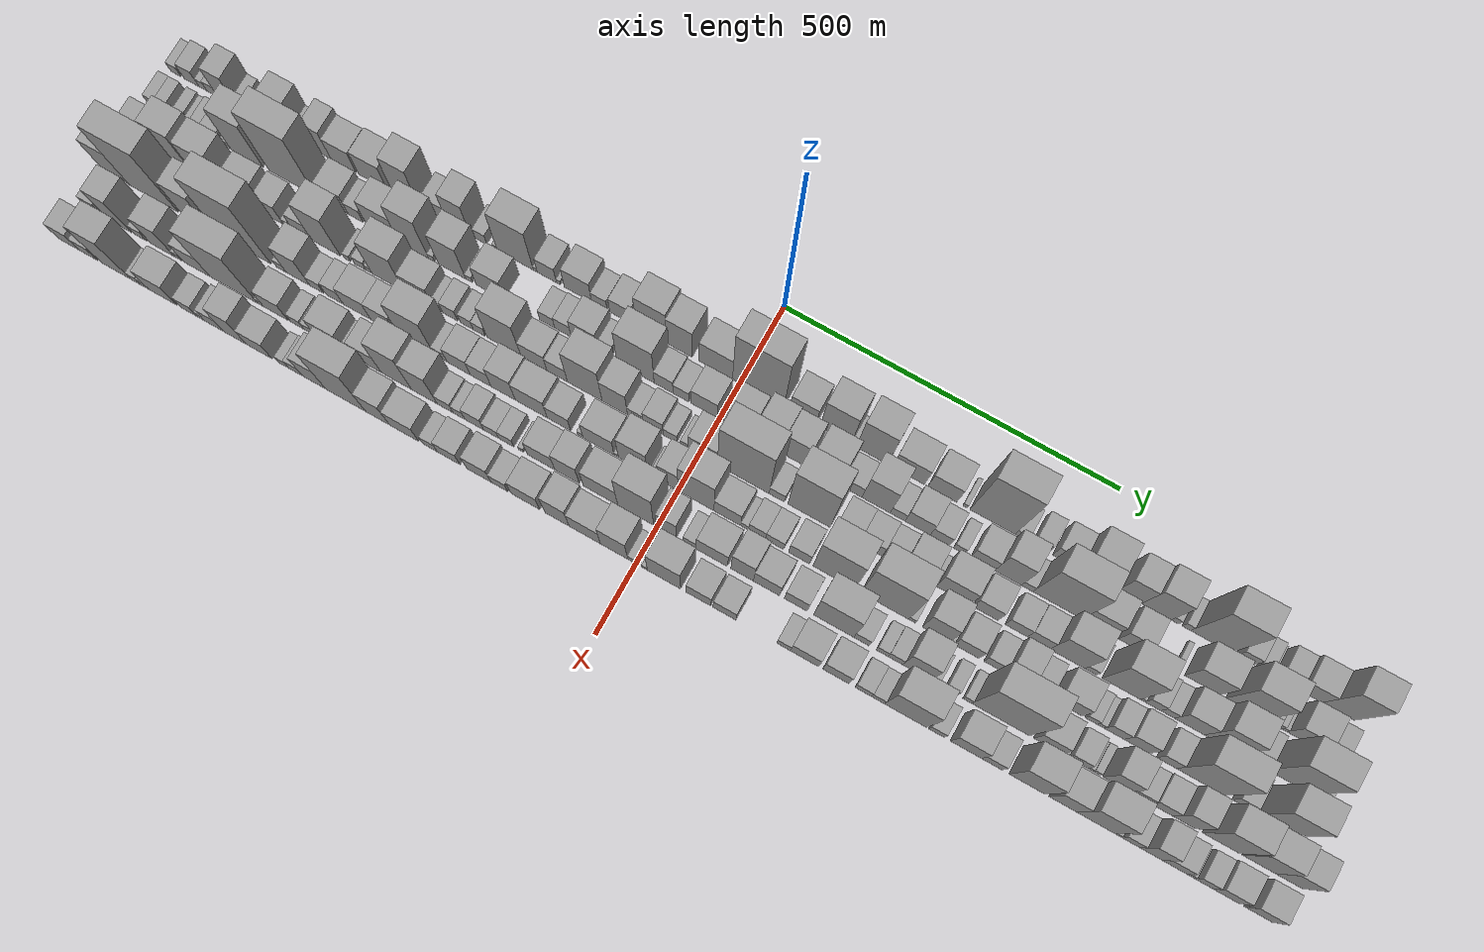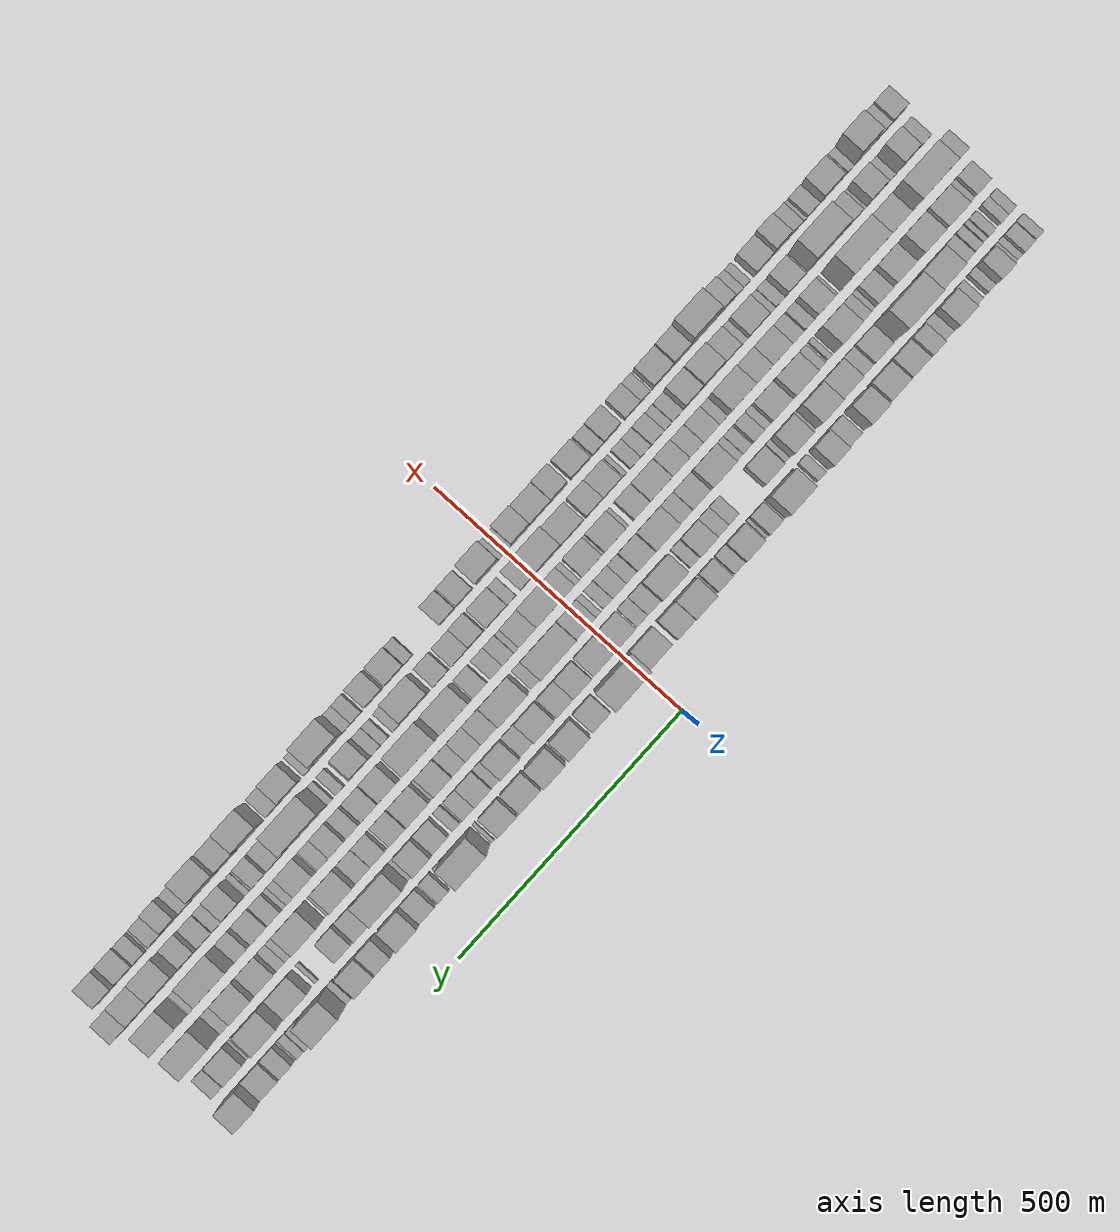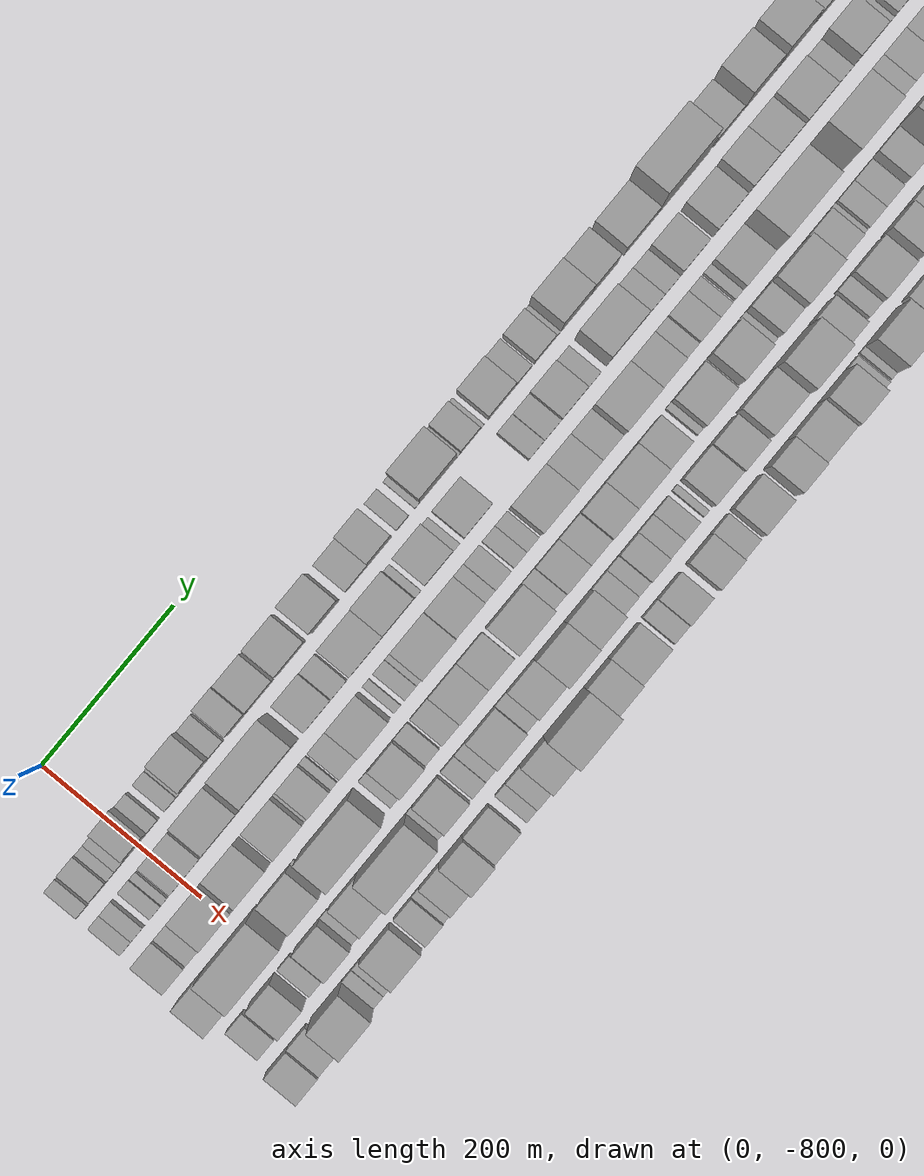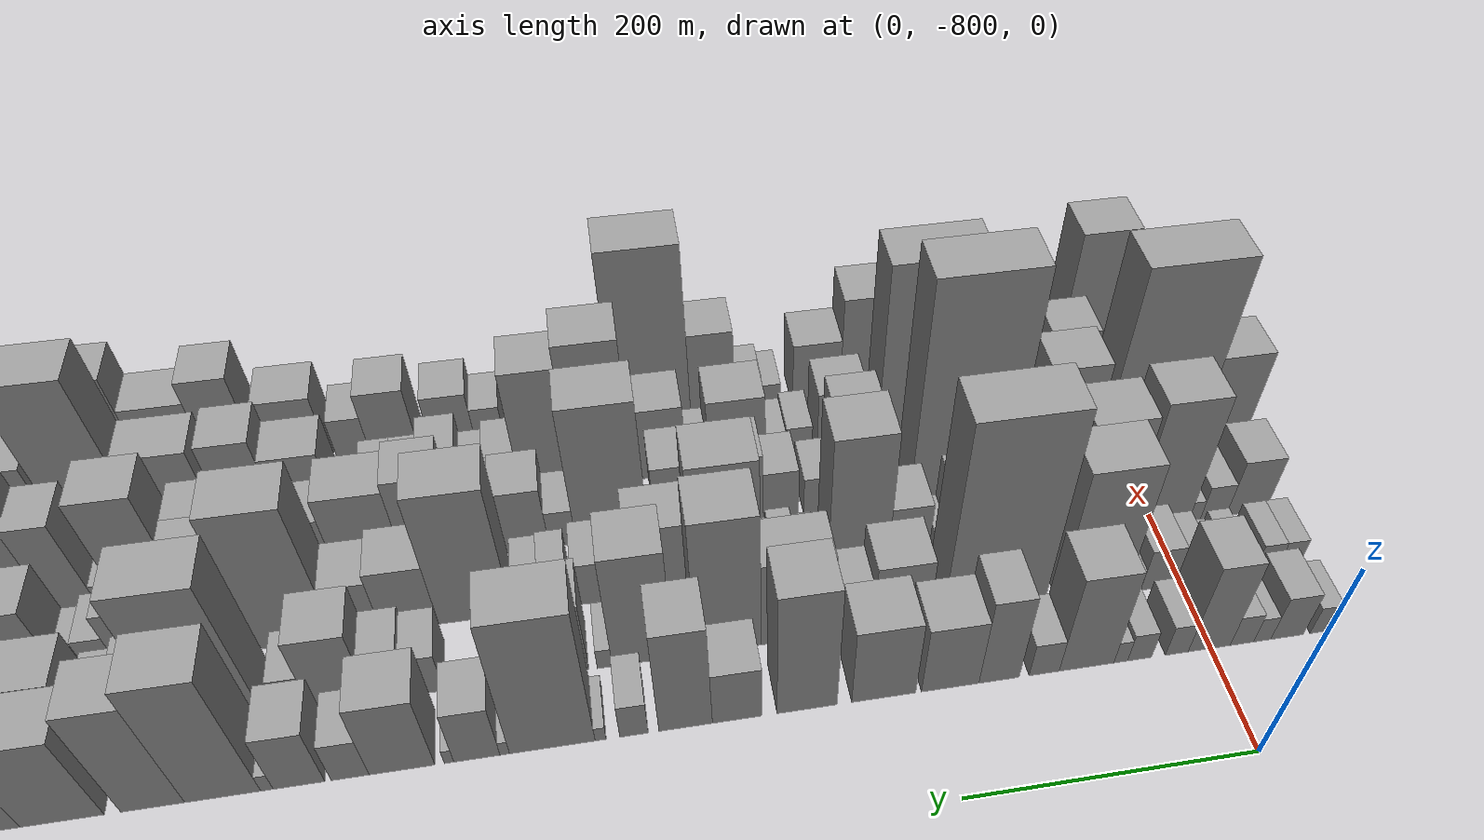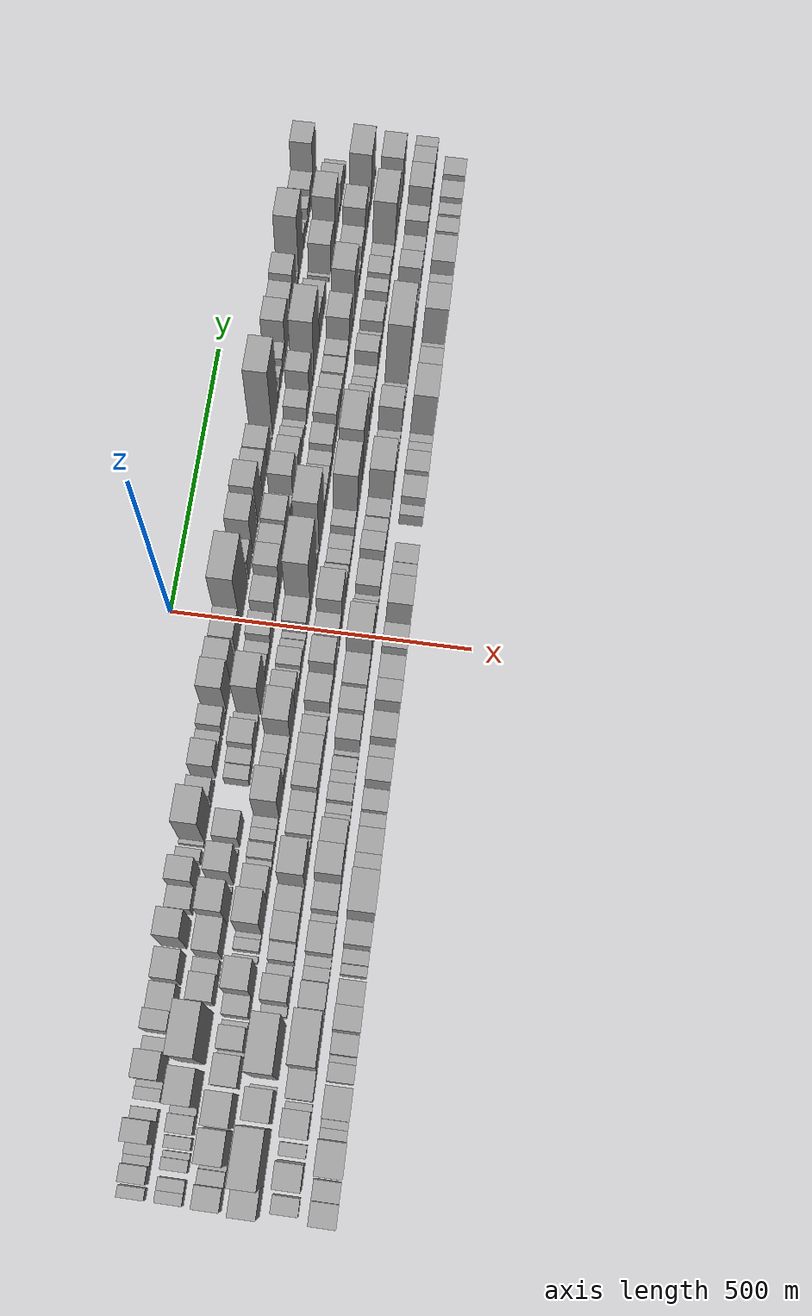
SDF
<sdf version="1.6">
 <world name="default">
  <scene>
   <sky><clouds><speed>12</speed></clouds></sky>
   <ambient>0.4 0.4 0.4 1</ambient>
   <background>0.7 0.7 0.7 1</background>
   <shadows>1</shadows>
  </scene>
  <gravity>0 0 -9.8066</gravity>
  <magnetic_field>6e-06 2.3e-05 -4.2e-05</magnetic_field>
  <physics default="0" name="default_physics" type="ode">
   <ode>
    <solver>
     <type>quick</type>
     <iters>10</iters>
     <sor>1.0</sor>
     <use_dynamic_moi_rescaling>0</use_dynamic_moi_rescaling>
    </solver>
    <constraints>
     <cfm>0</cfm>
     <erp>0.2</erp>
     <contact_max_correcting_vel>100</contact_max_correcting_vel>
     <contact_surface_layer>0.001</contact_surface_layer>
    </constraints>
   </ode>
   <max_step_size>0.004</max_step_size>
   <real_time_factor>1</real_time_factor>
   <real_time_update_rate>250</real_time_update_rate>
  </physics>
  <light name="sun" type="directional">
   <pose>0 0 10 0 0 0</pose>
   <diffuse>0.8 0.8 0.8 1</diffuse>
   <specular>0.2 0.2 0.2 1</specular>
   <attenuation>
    <range>1000</range>
    <constant>0.9</constant>
    <linear>0.01</linear>
    <quadratic>0.001</quadratic>
   </attenuation>
   <direction>-0.5 0.1 -0.9</direction>
  </light>
  <model name="building_1">
   <static>1</static>
   <pose>100.0000 -881.7625 0 0.000000 0.000000 0.000000</pose>
   <link name="link">
    <pose>0 0 15.00 0 0 0</pose>
    <collision name="collision"><geometry><box><size>40.0000 16.4750 30.0000</size></box></geometry></collision>
    <visual name="visual">
     <cast_shadows>0</cast_shadows>
     <geometry><box><size>40.0000 16.4750 30.0000</size></box></geometry>
     <material>
      <script>
       <uri>model://grey_wall/materials/scripts</uri>
       <uri>model://grey_wall/materials/textures</uri>
       <name>vrc/grey_wall</name>
      </script>
     </material>
    </visual>
   </link>
  </model>
  <model name="building_2">
   <static>1</static>
   <pose>100.0000 -856.3855 0 0.000000 0.000000 0.000000</pose>
   <link name="link">
    <pose>0 0 24.00 0 0 0</pose>
    <collision name="collision"><geometry><box><size>40.0000 24.2792 48.0000</size></box></geometry></collision>
    <visual name="visual">
     <cast_shadows>0</cast_shadows>
     <geometry><box><size>40.0000 24.2792 48.0000</size></box></geometry>
     <material>
      <script>
       <uri>model://grey_wall/materials/scripts</uri>
       <uri>model://grey_wall/materials/textures</uri>
       <name>vrc/grey_wall</name>
      </script>
     </material>
    </visual>
   </link>
  </model>
  <model name="building_3">
   <static>1</static>
   <pose>100.0000 -837.9051 0 0.000000 0.000000 0.000000</pose>
   <link name="link">
    <pose>0 0 13.50 0 0 0</pose>
    <collision name="collision"><geometry><box><size>40.0000 12.6815 27.0000</size></box></geometry></collision>
    <visual name="visual">
     <cast_shadows>0</cast_shadows>
     <geometry><box><size>40.0000 12.6815 27.0000</size></box></geometry>
     <material>
      <script>
       <uri>model://grey_wall/materials/scripts</uri>
       <uri>model://grey_wall/materials/textures</uri>
       <name>vrc/grey_wall</name>
      </script>
     </material>
    </visual>
   </link>
  </model>
  <model name="building_4">
   <static>1</static>
   <pose>100.0000 -822.8629 0 0.000000 0.000000 0.000000</pose>
   <link name="link">
    <pose>0 0 16.50 0 0 0</pose>
    <collision name="collision"><geometry><box><size>40.0000 17.4029 33.0000</size></box></geometry></collision>
    <visual name="visual">
     <cast_shadows>0</cast_shadows>
     <geometry><box><size>40.0000 17.4029 33.0000</size></box></geometry>
     <material>
      <script>
       <uri>model://grey_wall/materials/scripts</uri>
       <uri>model://grey_wall/materials/textures</uri>
       <name>vrc/grey_wall</name>
      </script>
     </material>
    </visual>
   </link>
  </model>
  <model name="building_5">
   <static>1</static>
   <pose>100.0000 -798.7277 0 0.000000 0.000000 0.000000</pose>
   <link name="link">
    <pose>0 0 48.00 0 0 0</pose>
    <collision name="collision"><geometry><box><size>40.0000 30.8675 96.0000</size></box></geometry></collision>
    <visual name="visual">
     <cast_shadows>0</cast_shadows>
     <geometry><box><size>40.0000 30.8675 96.0000</size></box></geometry>
     <material>
      <script>
       <uri>model://grey_wall/materials/scripts</uri>
       <uri>model://grey_wall/materials/textures</uri>
       <name>vrc/grey_wall</name>
      </script>
     </material>
    </visual>
   </link>
  </model>
  <model name="building_6">
   <static>1</static>
   <pose>100.0000 -774.9981 0 0.000000 0.000000 0.000000</pose>
   <link name="link">
    <pose>0 0 16.50 0 0 0</pose>
    <collision name="collision"><geometry><box><size>40.0000 16.5916 33.0000</size></box></geometry></collision>
    <visual name="visual">
     <cast_shadows>0</cast_shadows>
     <geometry><box><size>40.0000 16.5916 33.0000</size></box></geometry>
     <material>
      <script>
       <uri>model://grey_wall/materials/scripts</uri>
       <uri>model://grey_wall/materials/textures</uri>
       <name>vrc/grey_wall</name>
      </script>
     </material>
    </visual>
   </link>
  </model>
  <model name="building_7">
   <static>1</static>
   <pose>100.0000 -747.9396 0 0.000000 0.000000 0.000000</pose>
   <link name="link">
    <pose>0 0 15.00 0 0 0</pose>
    <collision name="collision"><geometry><box><size>40.0000 17.5255 30.0000</size></box></geometry></collision>
    <visual name="visual">
     <cast_shadows>0</cast_shadows>
     <geometry><box><size>40.0000 17.5255 30.0000</size></box></geometry>
     <material>
      <script>
       <uri>model://grey_wall/materials/scripts</uri>
       <uri>model://grey_wall/materials/textures</uri>
       <name>vrc/grey_wall</name>
      </script>
     </material>
    </visual>
   </link>
  </model>
  <model name="building_8">
   <static>1</static>
   <pose>100.0000 -734.2283 0 0.000000 0.000000 0.000000</pose>
   <link name="link">
    <pose>0 0 12.00 0 0 0</pose>
    <collision name="collision"><geometry><box><size>40.0000 9.8973 24.0000</size></box></geometry></collision>
    <visual name="visual">
     <cast_shadows>0</cast_shadows>
     <geometry><box><size>40.0000 9.8973 24.0000</size></box></geometry>
     <material>
      <script>
       <uri>model://grey_wall/materials/scripts</uri>
       <uri>model://grey_wall/materials/textures</uri>
       <name>vrc/grey_wall</name>
      </script>
     </material>
    </visual>
   </link>
  </model>
  <model name="building_9">
   <static>1</static>
   <pose>100.0000 -709.6391 0 0.000000 0.000000 0.000000</pose>
   <link name="link">
    <pose>0 0 52.50 0 0 0</pose>
    <collision name="collision"><geometry><box><size>40.0000 39.2811 105.0000</size></box></geometry></collision>
    <visual name="visual">
     <cast_shadows>0</cast_shadows>
     <geometry><box><size>40.0000 39.2811 105.0000</size></box></geometry>
     <material>
      <script>
       <uri>model://grey_wall/materials/scripts</uri>
       <uri>model://grey_wall/materials/textures</uri>
       <name>vrc/grey_wall</name>
      </script>
     </material>
    </visual>
   </link>
  </model>
  <model name="building_10">
   <static>1</static>
   <pose>100.0000 -679.3058 0 0.000000 0.000000 0.000000</pose>
   <link name="link">
    <pose>0 0 18.00 0 0 0</pose>
    <collision name="collision"><geometry><box><size>40.0000 21.3855 36.0000</size></box></geometry></collision>
    <visual name="visual">
     <cast_shadows>0</cast_shadows>
     <geometry><box><size>40.0000 21.3855 36.0000</size></box></geometry>
     <material>
      <script>
       <uri>model://grey_wall/materials/scripts</uri>
       <uri>model://grey_wall/materials/textures</uri>
       <name>vrc/grey_wall</name>
      </script>
     </material>
    </visual>
   </link>
  </model>
  <model name="building_11">
   <static>1</static>
   <pose>100.0000 -647.3270 0 0.000000 0.000000 0.000000</pose>
   <link name="link">
    <pose>0 0 46.50 0 0 0</pose>
    <collision name="collision"><geometry><box><size>40.0000 28.5720 93.0000</size></box></geometry></collision>
    <visual name="visual">
     <cast_shadows>0</cast_shadows>
     <geometry><box><size>40.0000 28.5720 93.0000</size></box></geometry>
     <material>
      <script>
       <uri>model://grey_wall/materials/scripts</uri>
       <uri>model://grey_wall/materials/textures</uri>
       <name>vrc/grey_wall</name>
      </script>
     </material>
    </visual>
   </link>
  </model>
  <model name="building_12">
   <static>1</static>
   <pose>100.0000 -612.9655 0 0.000000 0.000000 0.000000</pose>
   <link name="link">
    <pose>0 0 36.00 0 0 0</pose>
    <collision name="collision"><geometry><box><size>40.0000 40.1510 72.0000</size></box></geometry></collision>
    <visual name="visual">
     <cast_shadows>0</cast_shadows>
     <geometry><box><size>40.0000 40.1510 72.0000</size></box></geometry>
     <material>
      <script>
       <uri>model://grey_wall/materials/scripts</uri>
       <uri>model://grey_wall/materials/textures</uri>
       <name>vrc/grey_wall</name>
      </script>
     </material>
    </visual>
   </link>
  </model>
  <model name="building_13">
   <static>1</static>
   <pose>100.0000 -566.7129 0 0.000000 0.000000 0.000000</pose>
   <link name="link">
    <pose>0 0 40.50 0 0 0</pose>
    <collision name="collision"><geometry><box><size>40.0000 44.3541 81.0000</size></box></geometry></collision>
    <visual name="visual">
     <cast_shadows>0</cast_shadows>
     <geometry><box><size>40.0000 44.3541 81.0000</size></box></geometry>
     <material>
      <script>
       <uri>model://grey_wall/materials/scripts</uri>
       <uri>model://grey_wall/materials/textures</uri>
       <name>vrc/grey_wall</name>
      </script>
     </material>
    </visual>
   </link>
  </model>
  <model name="building_14">
   <static>1</static>
   <pose>100.0000 -514.0677 0 0.000000 0.000000 0.000000</pose>
   <link name="link">
    <pose>0 0 66.00 0 0 0</pose>
    <collision name="collision"><geometry><box><size>40.0000 40.9364 132.0000</size></box></geometry></collision>
    <visual name="visual">
     <cast_shadows>0</cast_shadows>
     <geometry><box><size>40.0000 40.9364 132.0000</size></box></geometry>
     <material>
      <script>
       <uri>model://grey_wall/materials/scripts</uri>
       <uri>model://grey_wall/materials/textures</uri>
       <name>vrc/grey_wall</name>
      </script>
     </material>
    </visual>
   </link>
  </model>
  <model name="building_15">
   <static>1</static>
   <pose>100.0000 -466.7707 0 0.000000 0.000000 0.000000</pose>
   <link name="link">
    <pose>0 0 28.50 0 0 0</pose>
    <collision name="collision"><geometry><box><size>40.0000 33.6576 57.0000</size></box></geometry></collision>
    <visual name="visual">
     <cast_shadows>0</cast_shadows>
     <geometry><box><size>40.0000 33.6576 57.0000</size></box></geometry>
     <material>
      <script>
       <uri>model://grey_wall/materials/scripts</uri>
       <uri>model://grey_wall/materials/textures</uri>
       <name>vrc/grey_wall</name>
      </script>
     </material>
    </visual>
   </link>
  </model>
  <model name="building_16">
   <static>1</static>
   <pose>100.0000 -432.0576 0 0.000000 0.000000 0.000000</pose>
   <link name="link">
    <pose>0 0 55.50 0 0 0</pose>
    <collision name="collision"><geometry><box><size>40.0000 35.7686 111.0000</size></box></geometry></collision>
    <visual name="visual">
     <cast_shadows>0</cast_shadows>
     <geometry><box><size>40.0000 35.7686 111.0000</size></box></geometry>
     <material>
      <script>
       <uri>model://grey_wall/materials/scripts</uri>
       <uri>model://grey_wall/materials/textures</uri>
       <name>vrc/grey_wall</name>
      </script>
     </material>
    </visual>
   </link>
  </model>
  <model name="building_17">
   <static>1</static>
   <pose>100.0000 -397.7357 0 0.000000 0.000000 0.000000</pose>
   <link name="link">
    <pose>0 0 18.00 0 0 0</pose>
    <collision name="collision"><geometry><box><size>40.0000 18.8753 36.0000</size></box></geometry></collision>
    <visual name="visual">
     <cast_shadows>0</cast_shadows>
     <geometry><box><size>40.0000 18.8753 36.0000</size></box></geometry>
     <material>
      <script>
       <uri>model://grey_wall/materials/scripts</uri>
       <uri>model://grey_wall/materials/textures</uri>
       <name>vrc/grey_wall</name>
      </script>
     </material>
    </visual>
   </link>
  </model>
  <model name="building_18">
   <static>1</static>
   <pose>100.0000 -375.6506 0 0.000000 0.000000 0.000000</pose>
   <link name="link">
    <pose>0 0 7.50 0 0 0</pose>
    <collision name="collision"><geometry><box><size>40.0000 7.2949 15.0000</size></box></geometry></collision>
    <visual name="visual">
     <cast_shadows>0</cast_shadows>
     <geometry><box><size>40.0000 7.2949 15.0000</size></box></geometry>
     <material>
      <script>
       <uri>model://grey_wall/materials/scripts</uri>
       <uri>model://grey_wall/materials/textures</uri>
       <name>vrc/grey_wall</name>
      </script>
     </material>
    </visual>
   </link>
  </model>
  <model name="building_19">
   <static>1</static>
   <pose>100.0000 -344.0484 0 0.000000 0.000000 0.000000</pose>
   <link name="link">
    <pose>0 0 73.50 0 0 0</pose>
    <collision name="collision"><geometry><box><size>40.0000 55.9094 147.0000</size></box></geometry></collision>
    <visual name="visual">
     <cast_shadows>0</cast_shadows>
     <geometry><box><size>40.0000 55.9094 147.0000</size></box></geometry>
     <material>
      <script>
       <uri>model://grey_wall/materials/scripts</uri>
       <uri>model://grey_wall/materials/textures</uri>
       <name>vrc/grey_wall</name>
      </script>
     </material>
    </visual>
   </link>
  </model>
  <model name="building_20">
   <static>1</static>
   <pose>100.0000 -313.0314 0 0.000000 0.000000 0.000000</pose>
   <link name="link">
    <pose>0 0 7.50 0 0 0</pose>
    <collision name="collision"><geometry><box><size>40.0000 6.1247 15.0000</size></box></geometry></collision>
    <visual name="visual">
     <cast_shadows>0</cast_shadows>
     <geometry><box><size>40.0000 6.1247 15.0000</size></box></geometry>
     <material>
      <script>
       <uri>model://grey_wall/materials/scripts</uri>
       <uri>model://grey_wall/materials/textures</uri>
       <name>vrc/grey_wall</name>
      </script>
     </material>
    </visual>
   </link>
  </model>
  <model name="building_21">
   <static>1</static>
   <pose>100.0000 -295.0973 0 0.000000 0.000000 0.000000</pose>
   <link name="link">
    <pose>0 0 28.50 0 0 0</pose>
    <collision name="collision"><geometry><box><size>40.0000 29.7436 57.0000</size></box></geometry></collision>
    <visual name="visual">
     <cast_shadows>0</cast_shadows>
     <geometry><box><size>40.0000 29.7436 57.0000</size></box></geometry>
     <material>
      <script>
       <uri>model://grey_wall/materials/scripts</uri>
       <uri>model://grey_wall/materials/textures</uri>
       <name>vrc/grey_wall</name>
      </script>
     </material>
    </visual>
   </link>
  </model>
  <model name="building_22">
   <static>1</static>
   <pose>100.0000 -277.1686 0 0.000000 0.000000 0.000000</pose>
   <link name="link">
    <pose>0 0 7.50 0 0 0</pose>
    <collision name="collision"><geometry><box><size>40.0000 6.1137 15.0000</size></box></geometry></collision>
    <visual name="visual">
     <cast_shadows>0</cast_shadows>
     <geometry><box><size>40.0000 6.1137 15.0000</size></box></geometry>
     <material>
      <script>
       <uri>model://grey_wall/materials/scripts</uri>
       <uri>model://grey_wall/materials/textures</uri>
       <name>vrc/grey_wall</name>
      </script>
     </material>
    </visual>
   </link>
  </model>
  <model name="building_23">
   <static>1</static>
   <pose>100.0000 -247.1722 0 0.000000 0.000000 0.000000</pose>
   <link name="link">
    <pose>0 0 39.00 0 0 0</pose>
    <collision name="collision"><geometry><box><size>40.0000 41.8790 78.0000</size></box></geometry></collision>
    <visual name="visual">
     <cast_shadows>0</cast_shadows>
     <geometry><box><size>40.0000 41.8790 78.0000</size></box></geometry>
     <material>
      <script>
       <uri>model://grey_wall/materials/scripts</uri>
       <uri>model://grey_wall/materials/textures</uri>
       <name>vrc/grey_wall</name>
      </script>
     </material>
    </visual>
   </link>
  </model>
  <model name="building_24">
   <static>1</static>
   <pose>100.0000 -214.3001 0 0.000000 0.000000 0.000000</pose>
   <link name="link">
    <pose>0 0 21.00 0 0 0</pose>
    <collision name="collision"><geometry><box><size>40.0000 23.8653 42.0000</size></box></geometry></collision>
    <visual name="visual">
     <cast_shadows>0</cast_shadows>
     <geometry><box><size>40.0000 23.8653 42.0000</size></box></geometry>
     <material>
      <script>
       <uri>model://grey_wall/materials/scripts</uri>
       <uri>model://grey_wall/materials/textures</uri>
       <name>vrc/grey_wall</name>
      </script>
     </material>
    </visual>
   </link>
  </model>
  <model name="building_25">
   <static>1</static>
   <pose>100.0000 -182.2615 0 0.000000 0.000000 0.000000</pose>
   <link name="link">
    <pose>0 0 30.00 0 0 0</pose>
    <collision name="collision"><geometry><box><size>40.0000 32.2119 60.0000</size></box></geometry></collision>
    <visual name="visual">
     <cast_shadows>0</cast_shadows>
     <geometry><box><size>40.0000 32.2119 60.0000</size></box></geometry>
     <material>
      <script>
       <uri>model://grey_wall/materials/scripts</uri>
       <uri>model://grey_wall/materials/textures</uri>
       <name>vrc/grey_wall</name>
      </script>
     </material>
    </visual>
   </link>
  </model>
  <model name="building_26">
   <static>1</static>
   <pose>100.0000 -162.3117 0 0.000000 0.000000 0.000000</pose>
   <link name="link">
    <pose>0 0 9.00 0 0 0</pose>
    <collision name="collision"><geometry><box><size>40.0000 7.6877 18.0000</size></box></geometry></collision>
    <visual name="visual">
     <cast_shadows>0</cast_shadows>
     <geometry><box><size>40.0000 7.6877 18.0000</size></box></geometry>
     <material>
      <script>
       <uri>model://grey_wall/materials/scripts</uri>
       <uri>model://grey_wall/materials/textures</uri>
       <name>vrc/grey_wall</name>
      </script>
     </material>
    </visual>
   </link>
  </model>
  <model name="building_27">
   <static>1</static>
   <pose>100.0000 -135.0123 0 0.000000 0.000000 0.000000</pose>
   <link name="link">
    <pose>0 0 66.00 0 0 0</pose>
    <collision name="collision"><geometry><box><size>40.0000 46.9110 132.0000</size></box></geometry></collision>
    <visual name="visual">
     <cast_shadows>0</cast_shadows>
     <geometry><box><size>40.0000 46.9110 132.0000</size></box></geometry>
     <material>
      <script>
       <uri>model://grey_wall/materials/scripts</uri>
       <uri>model://grey_wall/materials/textures</uri>
       <name>vrc/grey_wall</name>
      </script>
     </material>
    </visual>
   </link>
  </model>
  <model name="building_28">
   <static>1</static>
   <pose>100.0000 -92.0308 0 0.000000 0.000000 0.000000</pose>
   <link name="link">
    <pose>0 0 57.00 0 0 0</pose>
    <collision name="collision"><geometry><box><size>40.0000 39.0520 114.0000</size></box></geometry></collision>
    <visual name="visual">
     <cast_shadows>0</cast_shadows>
     <geometry><box><size>40.0000 39.0520 114.0000</size></box></geometry>
     <material>
      <script>
       <uri>model://grey_wall/materials/scripts</uri>
       <uri>model://grey_wall/materials/textures</uri>
       <name>vrc/grey_wall</name>
      </script>
     </material>
    </visual>
   </link>
  </model>
  <model name="building_29">
   <static>1</static>
   <pose>100.0000 -37.2151 0 0.000000 0.000000 0.000000</pose>
   <link name="link">
    <pose>0 0 45.00 0 0 0</pose>
    <collision name="collision"><geometry><box><size>40.0000 50.5796 90.0000</size></box></geometry></collision>
    <visual name="visual">
     <cast_shadows>0</cast_shadows>
     <geometry><box><size>40.0000 50.5796 90.0000</size></box></geometry>
     <material>
      <script>
       <uri>model://grey_wall/materials/scripts</uri>
       <uri>model://grey_wall/materials/textures</uri>
       <name>vrc/grey_wall</name>
      </script>
     </material>
    </visual>
   </link>
  </model>
  <model name="building_30">
   <static>1</static>
   <pose>100.0000 26.6968 0 0.000000 0.000000 0.000000</pose>
   <link name="link">
    <pose>0 0 106.50 0 0 0</pose>
    <collision name="collision"><geometry><box><size>40.0000 77.2442 213.0000</size></box></geometry></collision>
    <visual name="visual">
     <cast_shadows>0</cast_shadows>
     <geometry><box><size>40.0000 77.2442 213.0000</size></box></geometry>
     <material>
      <script>
       <uri>model://grey_wall/materials/scripts</uri>
       <uri>model://grey_wall/materials/textures</uri>
       <name>vrc/grey_wall</name>
      </script>
     </material>
    </visual>
   </link>
  </model>
  <model name="building_31">
   <static>1</static>
   <pose>100.0000 93.3202 0 0.000000 0.000000 0.000000</pose>
   <link name="link">
    <pose>0 0 39.00 0 0 0</pose>
    <collision name="collision"><geometry><box><size>40.0000 40.0027 78.0000</size></box></geometry></collision>
    <visual name="visual">
     <cast_shadows>0</cast_shadows>
     <geometry><box><size>40.0000 40.0027 78.0000</size></box></geometry>
     <material>
      <script>
       <uri>model://grey_wall/materials/scripts</uri>
       <uri>model://grey_wall/materials/textures</uri>
       <name>vrc/grey_wall</name>
      </script>
     </material>
    </visual>
   </link>
  </model>
  <model name="building_32">
   <static>1</static>
   <pose>100.0000 142.5750 0 0.000000 0.000000 0.000000</pose>
   <link name="link">
    <pose>0 0 69.00 0 0 0</pose>
    <collision name="collision"><geometry><box><size>40.0000 46.5068 138.0000</size></box></geometry></collision>
    <visual name="visual">
     <cast_shadows>0</cast_shadows>
     <geometry><box><size>40.0000 46.5068 138.0000</size></box></geometry>
     <material>
      <script>
       <uri>model://grey_wall/materials/scripts</uri>
       <uri>model://grey_wall/materials/textures</uri>
       <name>vrc/grey_wall</name>
      </script>
     </material>
    </visual>
   </link>
  </model>
  <model name="building_33">
   <static>1</static>
   <pose>100.0000 169.6122 0 0.000000 0.000000 0.000000</pose>
   <link name="link">
    <pose>0 0 9.00 0 0 0</pose>
    <collision name="collision"><geometry><box><size>40.0000 7.5677 18.0000</size></box></geometry></collision>
    <visual name="visual">
     <cast_shadows>0</cast_shadows>
     <geometry><box><size>40.0000 7.5677 18.0000</size></box></geometry>
     <material>
      <script>
       <uri>model://grey_wall/materials/scripts</uri>
       <uri>model://grey_wall/materials/textures</uri>
       <name>vrc/grey_wall</name>
      </script>
     </material>
    </visual>
   </link>
  </model>
  <model name="building_34">
   <static>1</static>
   <pose>100.0000 196.7768 0 0.000000 0.000000 0.000000</pose>
   <link name="link">
    <pose>0 0 73.50 0 0 0</pose>
    <collision name="collision"><geometry><box><size>40.0000 46.7614 147.0000</size></box></geometry></collision>
    <visual name="visual">
     <cast_shadows>0</cast_shadows>
     <geometry><box><size>40.0000 46.7614 147.0000</size></box></geometry>
     <material>
      <script>
       <uri>model://grey_wall/materials/scripts</uri>
       <uri>model://grey_wall/materials/textures</uri>
       <name>vrc/grey_wall</name>
      </script>
     </material>
    </visual>
   </link>
  </model>
  <model name="building_35">
   <static>1</static>
   <pose>100.0000 250.9078 0 0.000000 0.000000 0.000000</pose>
   <link name="link">
    <pose>0 0 40.50 0 0 0</pose>
    <collision name="collision"><geometry><box><size>40.0000 47.5008 81.0000</size></box></geometry></collision>
    <visual name="visual">
     <cast_shadows>0</cast_shadows>
     <geometry><box><size>40.0000 47.5008 81.0000</size></box></geometry>
     <material>
      <script>
       <uri>model://grey_wall/materials/scripts</uri>
       <uri>model://grey_wall/materials/textures</uri>
       <name>vrc/grey_wall</name>
      </script>
     </material>
    </visual>
   </link>
  </model>
  <model name="building_36">
   <static>1</static>
   <pose>100.0000 300.9294 0 0.000000 0.000000 0.000000</pose>
   <link name="link">
    <pose>0 0 37.50 0 0 0</pose>
    <collision name="collision"><geometry><box><size>40.0000 42.5423 75.0000</size></box></geometry></collision>
    <visual name="visual">
     <cast_shadows>0</cast_shadows>
     <geometry><box><size>40.0000 42.5423 75.0000</size></box></geometry>
     <material>
      <script>
       <uri>model://grey_wall/materials/scripts</uri>
       <uri>model://grey_wall/materials/textures</uri>
       <name>vrc/grey_wall</name>
      </script>
     </material>
    </visual>
   </link>
  </model>
  <model name="building_37">
   <static>1</static>
   <pose>100.0000 334.3581 0 0.000000 0.000000 0.000000</pose>
   <link name="link">
    <pose>0 0 7.50 0 0 0</pose>
    <collision name="collision"><geometry><box><size>40.0000 6.3151 15.0000</size></box></geometry></collision>
    <visual name="visual">
     <cast_shadows>0</cast_shadows>
     <geometry><box><size>40.0000 6.3151 15.0000</size></box></geometry>
     <material>
      <script>
       <uri>model://grey_wall/materials/scripts</uri>
       <uri>model://grey_wall/materials/textures</uri>
       <name>vrc/grey_wall</name>
      </script>
     </material>
    </visual>
   </link>
  </model>
  <model name="building_38">
   <static>1</static>
   <pose>100.0000 374.4109 0 0.000000 0.000000 0.000000</pose>
   <link name="link">
    <pose>0 0 109.50 0 0 0</pose>
    <collision name="collision"><geometry><box><size>40.0000 65.7906 219.0000</size></box></geometry></collision>
    <visual name="visual">
     <cast_shadows>0</cast_shadows>
     <geometry><box><size>40.0000 65.7906 219.0000</size></box></geometry>
     <material>
      <script>
       <uri>model://grey_wall/materials/scripts</uri>
       <uri>model://grey_wall/materials/textures</uri>
       <name>vrc/grey_wall</name>
      </script>
     </material>
    </visual>
   </link>
  </model>
  <model name="building_39">
   <static>1</static>
   <pose>100.0000 415.9332 0 0.000000 0.000000 0.000000</pose>
   <link name="link">
    <pose>0 0 15.00 0 0 0</pose>
    <collision name="collision"><geometry><box><size>40.0000 17.2539 30.0000</size></box></geometry></collision>
    <visual name="visual">
     <cast_shadows>0</cast_shadows>
     <geometry><box><size>40.0000 17.2539 30.0000</size></box></geometry>
     <material>
      <script>
       <uri>model://grey_wall/materials/scripts</uri>
       <uri>model://grey_wall/materials/textures</uri>
       <name>vrc/grey_wall</name>
      </script>
     </material>
    </visual>
   </link>
  </model>
  <model name="building_40">
   <static>1</static>
   <pose>100.0000 443.7423 0 0.000000 0.000000 0.000000</pose>
   <link name="link">
    <pose>0 0 22.50 0 0 0</pose>
    <collision name="collision"><geometry><box><size>40.0000 24.3644 45.0000</size></box></geometry></collision>
    <visual name="visual">
     <cast_shadows>0</cast_shadows>
     <geometry><box><size>40.0000 24.3644 45.0000</size></box></geometry>
     <material>
      <script>
       <uri>model://grey_wall/materials/scripts</uri>
       <uri>model://grey_wall/materials/textures</uri>
       <name>vrc/grey_wall</name>
      </script>
     </material>
    </visual>
   </link>
  </model>
  <model name="building_41">
   <static>1</static>
   <pose>100.0000 478.9445 0 0.000000 0.000000 0.000000</pose>
   <link name="link">
    <pose>0 0 28.50 0 0 0</pose>
    <collision name="collision"><geometry><box><size>40.0000 34.0401 57.0000</size></box></geometry></collision>
    <visual name="visual">
     <cast_shadows>0</cast_shadows>
     <geometry><box><size>40.0000 34.0401 57.0000</size></box></geometry>
     <material>
      <script>
       <uri>model://grey_wall/materials/scripts</uri>
       <uri>model://grey_wall/materials/textures</uri>
       <name>vrc/grey_wall</name>
      </script>
     </material>
    </visual>
   </link>
  </model>
  <model name="building_42">
   <static>1</static>
   <pose>100.0000 518.6158 0 0.000000 0.000000 0.000000</pose>
   <link name="link">
    <pose>0 0 61.50 0 0 0</pose>
    <collision name="collision"><geometry><box><size>40.0000 45.3024 123.0000</size></box></geometry></collision>
    <visual name="visual">
     <cast_shadows>0</cast_shadows>
     <geometry><box><size>40.0000 45.3024 123.0000</size></box></geometry>
     <material>
      <script>
       <uri>model://grey_wall/materials/scripts</uri>
       <uri>model://grey_wall/materials/textures</uri>
       <name>vrc/grey_wall</name>
      </script>
     </material>
    </visual>
   </link>
  </model>
  <model name="building_43">
   <static>1</static>
   <pose>100.0000 544.9368 0 0.000000 0.000000 0.000000</pose>
   <link name="link">
    <pose>0 0 7.50 0 0 0</pose>
    <collision name="collision"><geometry><box><size>40.0000 7.3397 15.0000</size></box></geometry></collision>
    <visual name="visual">
     <cast_shadows>0</cast_shadows>
     <geometry><box><size>40.0000 7.3397 15.0000</size></box></geometry>
     <material>
      <script>
       <uri>model://grey_wall/materials/scripts</uri>
       <uri>model://grey_wall/materials/textures</uri>
       <name>vrc/grey_wall</name>
      </script>
     </material>
    </visual>
   </link>
  </model>
  <model name="building_44">
   <static>1</static>
   <pose>100.0000 572.9980 0 0.000000 0.000000 0.000000</pose>
   <link name="link">
    <pose>0 0 49.50 0 0 0</pose>
    <collision name="collision"><geometry><box><size>40.0000 34.7826 99.0000</size></box></geometry></collision>
    <visual name="visual">
     <cast_shadows>0</cast_shadows>
     <geometry><box><size>40.0000 34.7826 99.0000</size></box></geometry>
     <material>
      <script>
       <uri>model://grey_wall/materials/scripts</uri>
       <uri>model://grey_wall/materials/textures</uri>
       <name>vrc/grey_wall</name>
      </script>
     </material>
    </visual>
   </link>
  </model>
  <model name="building_45">
   <static>1</static>
   <pose>100.0000 611.5817 0 0.000000 0.000000 0.000000</pose>
   <link name="link">
    <pose>0 0 60.00 0 0 0</pose>
    <collision name="collision"><geometry><box><size>40.0000 42.3847 120.0000</size></box></geometry></collision>
    <visual name="visual">
     <cast_shadows>0</cast_shadows>
     <geometry><box><size>40.0000 42.3847 120.0000</size></box></geometry>
     <material>
      <script>
       <uri>model://grey_wall/materials/scripts</uri>
       <uri>model://grey_wall/materials/textures</uri>
       <name>vrc/grey_wall</name>
      </script>
     </material>
    </visual>
   </link>
  </model>
  <model name="building_46">
   <static>1</static>
   <pose>100.0000 638.1814 0 0.000000 0.000000 0.000000</pose>
   <link name="link">
    <pose>0 0 12.00 0 0 0</pose>
    <collision name="collision"><geometry><box><size>40.0000 10.8147 24.0000</size></box></geometry></collision>
    <visual name="visual">
     <cast_shadows>0</cast_shadows>
     <geometry><box><size>40.0000 10.8147 24.0000</size></box></geometry>
     <material>
      <script>
       <uri>model://grey_wall/materials/scripts</uri>
       <uri>model://grey_wall/materials/textures</uri>
       <name>vrc/grey_wall</name>
      </script>
     </material>
    </visual>
   </link>
  </model>
  <model name="building_47">
   <static>1</static>
   <pose>100.0000 654.4416 0 0.000000 0.000000 0.000000</pose>
   <link name="link">
    <pose>0 0 13.50 0 0 0</pose>
    <collision name="collision"><geometry><box><size>40.0000 11.7057 27.0000</size></box></geometry></collision>
    <visual name="visual">
     <cast_shadows>0</cast_shadows>
     <geometry><box><size>40.0000 11.7057 27.0000</size></box></geometry>
     <material>
      <script>
       <uri>model://grey_wall/materials/scripts</uri>
       <uri>model://grey_wall/materials/textures</uri>
       <name>vrc/grey_wall</name>
      </script>
     </material>
    </visual>
   </link>
  </model>
  <model name="building_48">
   <static>1</static>
   <pose>100.0000 688.8417 0 0.000000 0.000000 0.000000</pose>
   <link name="link">
    <pose>0 0 93.00 0 0 0</pose>
    <collision name="collision"><geometry><box><size>40.0000 57.0945 186.0000</size></box></geometry></collision>
    <visual name="visual">
     <cast_shadows>0</cast_shadows>
     <geometry><box><size>40.0000 57.0945 186.0000</size></box></geometry>
     <material>
      <script>
       <uri>model://grey_wall/materials/scripts</uri>
       <uri>model://grey_wall/materials/textures</uri>
       <name>vrc/grey_wall</name>
      </script>
     </material>
    </visual>
   </link>
  </model>
  <model name="building_49">
   <static>1</static>
   <pose>100.0000 737.1750 0 0.000000 0.000000 0.000000</pose>
   <link name="link">
    <pose>0 0 24.00 0 0 0</pose>
    <collision name="collision"><geometry><box><size>40.0000 25.5722 48.0000</size></box></geometry></collision>
    <visual name="visual">
     <cast_shadows>0</cast_shadows>
     <geometry><box><size>40.0000 25.5722 48.0000</size></box></geometry>
     <material>
      <script>
       <uri>model://grey_wall/materials/scripts</uri>
       <uri>model://grey_wall/materials/textures</uri>
       <name>vrc/grey_wall</name>
      </script>
     </material>
    </visual>
   </link>
  </model>
  <model name="building_50">
   <static>1</static>
   <pose>100.0000 761.8153 0 0.000000 0.000000 0.000000</pose>
   <link name="link">
    <pose>0 0 15.00 0 0 0</pose>
    <collision name="collision"><geometry><box><size>40.0000 15.7083 30.0000</size></box></geometry></collision>
    <visual name="visual">
     <cast_shadows>0</cast_shadows>
     <geometry><box><size>40.0000 15.7083 30.0000</size></box></geometry>
     <material>
      <script>
       <uri>model://grey_wall/materials/scripts</uri>
       <uri>model://grey_wall/materials/textures</uri>
       <name>vrc/grey_wall</name>
      </script>
     </material>
    </visual>
   </link>
  </model>
  <model name="building_51">
   <static>1</static>
   <pose>100.0000 772.6809 0 0.000000 0.000000 0.000000</pose>
   <link name="link">
    <pose>0 0 7.50 0 0 0</pose>
    <collision name="collision"><geometry><box><size>40.0000 6.0230 15.0000</size></box></geometry></collision>
    <visual name="visual">
     <cast_shadows>0</cast_shadows>
     <geometry><box><size>40.0000 6.0230 15.0000</size></box></geometry>
     <material>
      <script>
       <uri>model://grey_wall/materials/scripts</uri>
       <uri>model://grey_wall/materials/textures</uri>
       <name>vrc/grey_wall</name>
      </script>
     </material>
    </visual>
   </link>
  </model>
  <model name="building_52">
   <static>1</static>
   <pose>100.0000 792.7861 0 0.000000 0.000000 0.000000</pose>
   <link name="link">
    <pose>0 0 24.00 0 0 0</pose>
    <collision name="collision"><geometry><box><size>40.0000 28.1875 48.0000</size></box></geometry></collision>
    <visual name="visual">
     <cast_shadows>0</cast_shadows>
     <geometry><box><size>40.0000 28.1875 48.0000</size></box></geometry>
     <material>
      <script>
       <uri>model://grey_wall/materials/scripts</uri>
       <uri>model://grey_wall/materials/textures</uri>
       <name>vrc/grey_wall</name>
      </script>
     </material>
    </visual>
   </link>
  </model>
  <model name="building_53">
   <static>1</static>
   <pose>100.0000 826.5708 0 0.000000 0.000000 0.000000</pose>
   <link name="link">
    <pose>0 0 33.00 0 0 0</pose>
    <collision name="collision"><geometry><box><size>40.0000 39.3819 66.0000</size></box></geometry></collision>
    <visual name="visual">
     <cast_shadows>0</cast_shadows>
     <geometry><box><size>40.0000 39.3819 66.0000</size></box></geometry>
     <material>
      <script>
       <uri>model://grey_wall/materials/scripts</uri>
       <uri>model://grey_wall/materials/textures</uri>
       <name>vrc/grey_wall</name>
      </script>
     </material>
    </visual>
   </link>
  </model>
  <model name="building_54">
   <static>1</static>
   <pose>100.0000 869.0312 0 0.000000 0.000000 0.000000</pose>
   <link name="link">
    <pose>0 0 72.00 0 0 0</pose>
    <collision name="collision"><geometry><box><size>40.0000 45.5390 144.0000</size></box></geometry></collision>
    <visual name="visual">
     <cast_shadows>0</cast_shadows>
     <geometry><box><size>40.0000 45.5390 144.0000</size></box></geometry>
     <material>
      <script>
       <uri>model://grey_wall/materials/scripts</uri>
       <uri>model://grey_wall/materials/textures</uri>
       <name>vrc/grey_wall</name>
      </script>
     </material>
    </visual>
   </link>
  </model>
  <model name="building_55">
   <static>1</static>
   <pose>155.0000 -881.6311 0 0.000000 0.000000 0.000000</pose>
   <link name="link">
    <pose>0 0 16.50 0 0 0</pose>
    <collision name="collision"><geometry><box><size>40.0000 16.7379 33.0000</size></box></geometry></collision>
    <visual name="visual">
     <cast_shadows>0</cast_shadows>
     <geometry><box><size>40.0000 16.7379 33.0000</size></box></geometry>
     <material>
      <script>
       <uri>model://grey_wall/materials/scripts</uri>
       <uri>model://grey_wall/materials/textures</uri>
       <name>vrc/grey_wall</name>
      </script>
     </material>
    </visual>
   </link>
  </model>
  <model name="building_56">
   <static>1</static>
   <pose>155.0000 -864.4786 0 0.000000 0.000000 0.000000</pose>
   <link name="link">
    <pose>0 0 16.50 0 0 0</pose>
    <collision name="collision"><geometry><box><size>40.0000 17.5671 33.0000</size></box></geometry></collision>
    <visual name="visual">
     <cast_shadows>0</cast_shadows>
     <geometry><box><size>40.0000 17.5671 33.0000</size></box></geometry>
     <material>
      <script>
       <uri>model://grey_wall/materials/scripts</uri>
       <uri>model://grey_wall/materials/textures</uri>
       <name>vrc/grey_wall</name>
      </script>
     </material>
    </visual>
   </link>
  </model>
  <model name="building_57">
   <static>1</static>
   <pose>155.0000 -837.4227 0 0.000000 0.000000 0.000000</pose>
   <link name="link">
    <pose>0 0 15.00 0 0 0</pose>
    <collision name="collision"><geometry><box><size>40.0000 16.5447 30.0000</size></box></geometry></collision>
    <visual name="visual">
     <cast_shadows>0</cast_shadows>
     <geometry><box><size>40.0000 16.5447 30.0000</size></box></geometry>
     <material>
      <script>
       <uri>model://grey_wall/materials/scripts</uri>
       <uri>model://grey_wall/materials/textures</uri>
       <name>vrc/grey_wall</name>
      </script>
     </material>
    </visual>
   </link>
  </model>
  <model name="building_58">
   <static>1</static>
   <pose>155.0000 -824.5415 0 0.000000 0.000000 0.000000</pose>
   <link name="link">
    <pose>0 0 10.50 0 0 0</pose>
    <collision name="collision"><geometry><box><size>40.0000 9.2176 21.0000</size></box></geometry></collision>
    <visual name="visual">
     <cast_shadows>0</cast_shadows>
     <geometry><box><size>40.0000 9.2176 21.0000</size></box></geometry>
     <material>
      <script>
       <uri>model://grey_wall/materials/scripts</uri>
       <uri>model://grey_wall/materials/textures</uri>
       <name>vrc/grey_wall</name>
      </script>
     </material>
    </visual>
   </link>
  </model>
  <model name="building_59">
   <static>1</static>
   <pose>155.0000 -807.5551 0 0.000000 0.000000 0.000000</pose>
   <link name="link">
    <pose>0 0 16.50 0 0 0</pose>
    <collision name="collision"><geometry><box><size>40.0000 16.7553 33.0000</size></box></geometry></collision>
    <visual name="visual">
     <cast_shadows>0</cast_shadows>
     <geometry><box><size>40.0000 16.7553 33.0000</size></box></geometry>
     <material>
      <script>
       <uri>model://grey_wall/materials/scripts</uri>
       <uri>model://grey_wall/materials/textures</uri>
       <name>vrc/grey_wall</name>
      </script>
     </material>
    </visual>
   </link>
  </model>
  <model name="building_60">
   <static>1</static>
   <pose>155.0000 -782.2550 0 0.000000 0.000000 0.000000</pose>
   <link name="link">
    <pose>0 0 22.50 0 0 0</pose>
    <collision name="collision"><geometry><box><size>40.0000 25.8450 45.0000</size></box></geometry></collision>
    <visual name="visual">
     <cast_shadows>0</cast_shadows>
     <geometry><box><size>40.0000 25.8450 45.0000</size></box></geometry>
     <material>
      <script>
       <uri>model://grey_wall/materials/scripts</uri>
       <uri>model://grey_wall/materials/textures</uri>
       <name>vrc/grey_wall</name>
      </script>
     </material>
    </visual>
   </link>
  </model>
  <model name="building_61">
   <static>1</static>
   <pose>155.0000 -763.6076 0 0.000000 0.000000 0.000000</pose>
   <link name="link">
    <pose>0 0 12.00 0 0 0</pose>
    <collision name="collision"><geometry><box><size>40.0000 11.4497 24.0000</size></box></geometry></collision>
    <visual name="visual">
     <cast_shadows>0</cast_shadows>
     <geometry><box><size>40.0000 11.4497 24.0000</size></box></geometry>
     <material>
      <script>
       <uri>model://grey_wall/materials/scripts</uri>
       <uri>model://grey_wall/materials/textures</uri>
       <name>vrc/grey_wall</name>
      </script>
     </material>
    </visual>
   </link>
  </model>
  <model name="building_62">
   <static>1</static>
   <pose>155.0000 -732.2870 0 0.000000 0.000000 0.000000</pose>
   <link name="link">
    <pose>0 0 70.50 0 0 0</pose>
    <collision name="collision"><geometry><box><size>40.0000 51.1915 141.0000</size></box></geometry></collision>
    <visual name="visual">
     <cast_shadows>0</cast_shadows>
     <geometry><box><size>40.0000 51.1915 141.0000</size></box></geometry>
     <material>
      <script>
       <uri>model://grey_wall/materials/scripts</uri>
       <uri>model://grey_wall/materials/textures</uri>
       <name>vrc/grey_wall</name>
      </script>
     </material>
    </visual>
   </link>
  </model>
  <model name="building_63">
   <static>1</static>
   <pose>155.0000 -659.3699 0 0.000000 0.000000 0.000000</pose>
   <link name="link">
    <pose>0 0 102.00 0 0 0</pose>
    <collision name="collision"><geometry><box><size>40.0000 74.6427 204.0000</size></box></geometry></collision>
    <visual name="visual">
     <cast_shadows>0</cast_shadows>
     <geometry><box><size>40.0000 74.6427 204.0000</size></box></geometry>
     <material>
      <script>
       <uri>model://grey_wall/materials/scripts</uri>
       <uri>model://grey_wall/materials/textures</uri>
       <name>vrc/grey_wall</name>
      </script>
     </material>
    </visual>
   </link>
  </model>
  <model name="building_64">
   <static>1</static>
   <pose>155.0000 -591.8544 0 0.000000 0.000000 0.000000</pose>
   <link name="link">
    <pose>0 0 34.50 0 0 0</pose>
    <collision name="collision"><geometry><box><size>40.0000 40.3883 69.0000</size></box></geometry></collision>
    <visual name="visual">
     <cast_shadows>0</cast_shadows>
     <geometry><box><size>40.0000 40.3883 69.0000</size></box></geometry>
     <material>
      <script>
       <uri>model://grey_wall/materials/scripts</uri>
       <uri>model://grey_wall/materials/textures</uri>
       <name>vrc/grey_wall</name>
      </script>
     </material>
    </visual>
   </link>
  </model>
  <model name="building_65">
   <static>1</static>
   <pose>155.0000 -559.8969 0 0.000000 0.000000 0.000000</pose>
   <link name="link">
    <pose>0 0 22.50 0 0 0</pose>
    <collision name="collision"><geometry><box><size>40.0000 23.5267 45.0000</size></box></geometry></collision>
    <visual name="visual">
     <cast_shadows>0</cast_shadows>
     <geometry><box><size>40.0000 23.5267 45.0000</size></box></geometry>
     <material>
      <script>
       <uri>model://grey_wall/materials/scripts</uri>
       <uri>model://grey_wall/materials/textures</uri>
       <name>vrc/grey_wall</name>
      </script>
     </material>
    </visual>
   </link>
  </model>
  <model name="building_66">
   <static>1</static>
   <pose>155.0000 -517.5448 0 0.000000 0.000000 0.000000</pose>
   <link name="link">
    <pose>0 0 45.00 0 0 0</pose>
    <collision name="collision"><geometry><box><size>40.0000 51.1776 90.0000</size></box></geometry></collision>
    <visual name="visual">
     <cast_shadows>0</cast_shadows>
     <geometry><box><size>40.0000 51.1776 90.0000</size></box></geometry>
     <material>
      <script>
       <uri>model://grey_wall/materials/scripts</uri>
       <uri>model://grey_wall/materials/textures</uri>
       <name>vrc/grey_wall</name>
      </script>
     </material>
    </visual>
   </link>
  </model>
  <model name="building_67">
   <static>1</static>
   <pose>155.0000 -468.7932 0 0.000000 0.000000 0.000000</pose>
   <link name="link">
    <pose>0 0 72.00 0 0 0</pose>
    <collision name="collision"><geometry><box><size>40.0000 46.3255 144.0000</size></box></geometry></collision>
    <visual name="visual">
     <cast_shadows>0</cast_shadows>
     <geometry><box><size>40.0000 46.3255 144.0000</size></box></geometry>
     <material>
      <script>
       <uri>model://grey_wall/materials/scripts</uri>
       <uri>model://grey_wall/materials/textures</uri>
       <name>vrc/grey_wall</name>
      </script>
     </material>
    </visual>
   </link>
  </model>
  <model name="building_68">
   <static>1</static>
   <pose>155.0000 -441.0066 0 0.000000 0.000000 0.000000</pose>
   <link name="link">
    <pose>0 0 10.50 0 0 0</pose>
    <collision name="collision"><geometry><box><size>40.0000 9.2479 21.0000</size></box></geometry></collision>
    <visual name="visual">
     <cast_shadows>0</cast_shadows>
     <geometry><box><size>40.0000 9.2479 21.0000</size></box></geometry>
     <material>
      <script>
       <uri>model://grey_wall/materials/scripts</uri>
       <uri>model://grey_wall/materials/textures</uri>
       <name>vrc/grey_wall</name>
      </script>
     </material>
    </visual>
   </link>
  </model>
  <model name="building_69">
   <static>1</static>
   <pose>155.0000 -409.1685 0 0.000000 0.000000 0.000000</pose>
   <link name="link">
    <pose>0 0 60.00 0 0 0</pose>
    <collision name="collision"><geometry><box><size>40.0000 42.4283 120.0000</size></box></geometry></collision>
    <visual name="visual">
     <cast_shadows>0</cast_shadows>
     <geometry><box><size>40.0000 42.4283 120.0000</size></box></geometry>
     <material>
      <script>
       <uri>model://grey_wall/materials/scripts</uri>
       <uri>model://grey_wall/materials/textures</uri>
       <name>vrc/grey_wall</name>
      </script>
     </material>
    </visual>
   </link>
  </model>
  <model name="building_70">
   <static>1</static>
   <pose>155.0000 -382.8238 0 0.000000 0.000000 0.000000</pose>
   <link name="link">
    <pose>0 0 10.50 0 0 0</pose>
    <collision name="collision"><geometry><box><size>40.0000 10.2613 21.0000</size></box></geometry></collision>
    <visual name="visual">
     <cast_shadows>0</cast_shadows>
     <geometry><box><size>40.0000 10.2613 21.0000</size></box></geometry>
     <material>
      <script>
       <uri>model://grey_wall/materials/scripts</uri>
       <uri>model://grey_wall/materials/textures</uri>
       <name>vrc/grey_wall</name>
      </script>
     </material>
    </visual>
   </link>
  </model>
  <model name="building_71">
   <static>1</static>
   <pose>155.0000 -350.4230 0 0.000000 0.000000 0.000000</pose>
   <link name="link">
    <pose>0 0 37.50 0 0 0</pose>
    <collision name="collision"><geometry><box><size>40.0000 42.5403 75.0000</size></box></geometry></collision>
    <visual name="visual">
     <cast_shadows>0</cast_shadows>
     <geometry><box><size>40.0000 42.5403 75.0000</size></box></geometry>
     <material>
      <script>
       <uri>model://grey_wall/materials/scripts</uri>
       <uri>model://grey_wall/materials/textures</uri>
       <name>vrc/grey_wall</name>
      </script>
     </material>
    </visual>
   </link>
  </model>
  <model name="building_72">
   <static>1</static>
   <pose>155.0000 -262.2023 0 0.000000 0.000000 0.000000</pose>
   <link name="link">
    <pose>0 0 21.00 0 0 0</pose>
    <collision name="collision"><geometry><box><size>40.0000 23.3004 42.0000</size></box></geometry></collision>
    <visual name="visual">
     <cast_shadows>0</cast_shadows>
     <geometry><box><size>40.0000 23.3004 42.0000</size></box></geometry>
     <material>
      <script>
       <uri>model://grey_wall/materials/scripts</uri>
       <uri>model://grey_wall/materials/textures</uri>
       <name>vrc/grey_wall</name>
      </script>
     </material>
    </visual>
   </link>
  </model>
  <model name="building_73">
   <static>1</static>
   <pose>155.0000 -237.8445 0 0.000000 0.000000 0.000000</pose>
   <link name="link">
    <pose>0 0 24.00 0 0 0</pose>
    <collision name="collision"><geometry><box><size>40.0000 25.4152 48.0000</size></box></geometry></collision>
    <visual name="visual">
     <cast_shadows>0</cast_shadows>
     <geometry><box><size>40.0000 25.4152 48.0000</size></box></geometry>
     <material>
      <script>
       <uri>model://grey_wall/materials/scripts</uri>
       <uri>model://grey_wall/materials/textures</uri>
       <name>vrc/grey_wall</name>
      </script>
     </material>
    </visual>
   </link>
  </model>
  <model name="building_74">
   <static>1</static>
   <pose>155.0000 -205.5108 0 0.000000 0.000000 0.000000</pose>
   <link name="link">
    <pose>0 0 39.00 0 0 0</pose>
    <collision name="collision"><geometry><box><size>40.0000 39.2521 78.0000</size></box></geometry></collision>
    <visual name="visual">
     <cast_shadows>0</cast_shadows>
     <geometry><box><size>40.0000 39.2521 78.0000</size></box></geometry>
     <material>
      <script>
       <uri>model://grey_wall/materials/scripts</uri>
       <uri>model://grey_wall/materials/textures</uri>
       <name>vrc/grey_wall</name>
      </script>
     </material>
    </visual>
   </link>
  </model>
  <model name="building_75">
   <static>1</static>
   <pose>155.0000 -175.6511 0 0.000000 0.000000 0.000000</pose>
   <link name="link">
    <pose>0 0 19.50 0 0 0</pose>
    <collision name="collision"><geometry><box><size>40.0000 20.4673 39.0000</size></box></geometry></collision>
    <visual name="visual">
     <cast_shadows>0</cast_shadows>
     <geometry><box><size>40.0000 20.4673 39.0000</size></box></geometry>
     <material>
      <script>
       <uri>model://grey_wall/materials/scripts</uri>
       <uri>model://grey_wall/materials/textures</uri>
       <name>vrc/grey_wall</name>
      </script>
     </material>
    </visual>
   </link>
  </model>
  <model name="building_76">
   <static>1</static>
   <pose>155.0000 -127.2554 0 0.000000 0.000000 0.000000</pose>
   <link name="link">
    <pose>0 0 73.50 0 0 0</pose>
    <collision name="collision"><geometry><box><size>40.0000 56.3242 147.0000</size></box></geometry></collision>
    <visual name="visual">
     <cast_shadows>0</cast_shadows>
     <geometry><box><size>40.0000 56.3242 147.0000</size></box></geometry>
     <material>
      <script>
       <uri>model://grey_wall/materials/scripts</uri>
       <uri>model://grey_wall/materials/textures</uri>
       <name>vrc/grey_wall</name>
      </script>
     </material>
    </visual>
   </link>
  </model>
  <model name="building_77">
   <static>1</static>
   <pose>155.0000 -84.8413 0 0.000000 0.000000 0.000000</pose>
   <link name="link">
    <pose>0 0 28.50 0 0 0</pose>
    <collision name="collision"><geometry><box><size>40.0000 28.5039 57.0000</size></box></geometry></collision>
    <visual name="visual">
     <cast_shadows>0</cast_shadows>
     <geometry><box><size>40.0000 28.5039 57.0000</size></box></geometry>
     <material>
      <script>
       <uri>model://grey_wall/materials/scripts</uri>
       <uri>model://grey_wall/materials/textures</uri>
       <name>vrc/grey_wall</name>
      </script>
     </material>
    </visual>
   </link>
  </model>
  <model name="building_78">
   <static>1</static>
   <pose>155.0000 -58.6024 0 0.000000 0.000000 0.000000</pose>
   <link name="link">
    <pose>0 0 22.50 0 0 0</pose>
    <collision name="collision"><geometry><box><size>40.0000 23.9740 45.0000</size></box></geometry></collision>
    <visual name="visual">
     <cast_shadows>0</cast_shadows>
     <geometry><box><size>40.0000 23.9740 45.0000</size></box></geometry>
     <material>
      <script>
       <uri>model://grey_wall/materials/scripts</uri>
       <uri>model://grey_wall/materials/textures</uri>
       <name>vrc/grey_wall</name>
      </script>
     </material>
    </visual>
   </link>
  </model>
  <model name="building_79">
   <static>1</static>
   <pose>155.0000 -23.7336 0 0.000000 0.000000 0.000000</pose>
   <link name="link">
    <pose>0 0 34.50 0 0 0</pose>
    <collision name="collision"><geometry><box><size>40.0000 39.7637 69.0000</size></box></geometry></collision>
    <visual name="visual">
     <cast_shadows>0</cast_shadows>
     <geometry><box><size>40.0000 39.7637 69.0000</size></box></geometry>
     <material>
      <script>
       <uri>model://grey_wall/materials/scripts</uri>
       <uri>model://grey_wall/materials/textures</uri>
       <name>vrc/grey_wall</name>
      </script>
     </material>
    </visual>
   </link>
  </model>
  <model name="building_80">
   <static>1</static>
   <pose>155.0000 28.4591 0 0.000000 0.000000 0.000000</pose>
   <link name="link">
    <pose>0 0 43.50 0 0 0</pose>
    <collision name="collision"><geometry><box><size>40.0000 44.6219 87.0000</size></box></geometry></collision>
    <visual name="visual">
     <cast_shadows>0</cast_shadows>
     <geometry><box><size>40.0000 44.6219 87.0000</size></box></geometry>
     <material>
      <script>
       <uri>model://grey_wall/materials/scripts</uri>
       <uri>model://grey_wall/materials/textures</uri>
       <name>vrc/grey_wall</name>
      </script>
     </material>
    </visual>
   </link>
  </model>
  <model name="building_81">
   <static>1</static>
   <pose>155.0000 74.6252 0 0.000000 0.000000 0.000000</pose>
   <link name="link">
    <pose>0 0 60.00 0 0 0</pose>
    <collision name="collision"><geometry><box><size>40.0000 39.7103 120.0000</size></box></geometry></collision>
    <visual name="visual">
     <cast_shadows>0</cast_shadows>
     <geometry><box><size>40.0000 39.7103 120.0000</size></box></geometry>
     <material>
      <script>
       <uri>model://grey_wall/materials/scripts</uri>
       <uri>model://grey_wall/materials/textures</uri>
       <name>vrc/grey_wall</name>
      </script>
     </material>
    </visual>
   </link>
  </model>
  <model name="building_82">
   <static>1</static>
   <pose>155.0000 113.2204 0 0.000000 0.000000 0.000000</pose>
   <link name="link">
    <pose>0 0 55.50 0 0 0</pose>
    <collision name="collision"><geometry><box><size>40.0000 37.4801 111.0000</size></box></geometry></collision>
    <visual name="visual">
     <cast_shadows>0</cast_shadows>
     <geometry><box><size>40.0000 37.4801 111.0000</size></box></geometry>
     <material>
      <script>
       <uri>model://grey_wall/materials/scripts</uri>
       <uri>model://grey_wall/materials/textures</uri>
       <name>vrc/grey_wall</name>
      </script>
     </material>
    </visual>
   </link>
  </model>
  <model name="building_83">
   <static>1</static>
   <pose>155.0000 158.5607 0 0.000000 0.000000 0.000000</pose>
   <link name="link">
    <pose>0 0 58.50 0 0 0</pose>
    <collision name="collision"><geometry><box><size>40.0000 45.2004 117.0000</size></box></geometry></collision>
    <visual name="visual">
     <cast_shadows>0</cast_shadows>
     <geometry><box><size>40.0000 45.2004 117.0000</size></box></geometry>
     <material>
      <script>
       <uri>model://grey_wall/materials/scripts</uri>
       <uri>model://grey_wall/materials/textures</uri>
       <name>vrc/grey_wall</name>
      </script>
     </material>
    </visual>
   </link>
  </model>
  <model name="building_84">
   <static>1</static>
   <pose>155.0000 196.5373 0 0.000000 0.000000 0.000000</pose>
   <link name="link">
    <pose>0 0 27.00 0 0 0</pose>
    <collision name="collision"><geometry><box><size>40.0000 30.7528 54.0000</size></box></geometry></collision>
    <visual name="visual">
     <cast_shadows>0</cast_shadows>
     <geometry><box><size>40.0000 30.7528 54.0000</size></box></geometry>
     <material>
      <script>
       <uri>model://grey_wall/materials/scripts</uri>
       <uri>model://grey_wall/materials/textures</uri>
       <name>vrc/grey_wall</name>
      </script>
     </material>
    </visual>
   </link>
  </model>
  <model name="building_85">
   <static>1</static>
   <pose>155.0000 232.6699 0 0.000000 0.000000 0.000000</pose>
   <link name="link">
    <pose>0 0 63.00 0 0 0</pose>
    <collision name="collision"><geometry><box><size>40.0000 41.5122 126.0000</size></box></geometry></collision>
    <visual name="visual">
     <cast_shadows>0</cast_shadows>
     <geometry><box><size>40.0000 41.5122 126.0000</size></box></geometry>
     <material>
      <script>
       <uri>model://grey_wall/materials/scripts</uri>
       <uri>model://grey_wall/materials/textures</uri>
       <name>vrc/grey_wall</name>
      </script>
     </material>
    </visual>
   </link>
  </model>
  <model name="building_86">
   <static>1</static>
   <pose>155.0000 264.3612 0 0.000000 0.000000 0.000000</pose>
   <link name="link">
    <pose>0 0 19.50 0 0 0</pose>
    <collision name="collision"><geometry><box><size>40.0000 21.8704 39.0000</size></box></geometry></collision>
    <visual name="visual">
     <cast_shadows>0</cast_shadows>
     <geometry><box><size>40.0000 21.8704 39.0000</size></box></geometry>
     <material>
      <script>
       <uri>model://grey_wall/materials/scripts</uri>
       <uri>model://grey_wall/materials/textures</uri>
       <name>vrc/grey_wall</name>
      </script>
     </material>
    </visual>
   </link>
  </model>
  <model name="building_87">
   <static>1</static>
   <pose>155.0000 293.8283 0 0.000000 0.000000 0.000000</pose>
   <link name="link">
    <pose>0 0 34.50 0 0 0</pose>
    <collision name="collision"><geometry><box><size>40.0000 37.0640 69.0000</size></box></geometry></collision>
    <visual name="visual">
     <cast_shadows>0</cast_shadows>
     <geometry><box><size>40.0000 37.0640 69.0000</size></box></geometry>
     <material>
      <script>
       <uri>model://grey_wall/materials/scripts</uri>
       <uri>model://grey_wall/materials/textures</uri>
       <name>vrc/grey_wall</name>
      </script>
     </material>
    </visual>
   </link>
  </model>
  <model name="building_88">
   <static>1</static>
   <pose>155.0000 326.4715 0 0.000000 0.000000 0.000000</pose>
   <link name="link">
    <pose>0 0 24.00 0 0 0</pose>
    <collision name="collision"><geometry><box><size>40.0000 28.2224 48.0000</size></box></geometry></collision>
    <visual name="visual">
     <cast_shadows>0</cast_shadows>
     <geometry><box><size>40.0000 28.2224 48.0000</size></box></geometry>
     <material>
      <script>
       <uri>model://grey_wall/materials/scripts</uri>
       <uri>model://grey_wall/materials/textures</uri>
       <name>vrc/grey_wall</name>
      </script>
     </material>
    </visual>
   </link>
  </model>
  <model name="building_89">
   <static>1</static>
   <pose>155.0000 354.9093 0 0.000000 0.000000 0.000000</pose>
   <link name="link">
    <pose>0 0 15.00 0 0 0</pose>
    <collision name="collision"><geometry><box><size>40.0000 16.6532 30.0000</size></box></geometry></collision>
    <visual name="visual">
     <cast_shadows>0</cast_shadows>
     <geometry><box><size>40.0000 16.6532 30.0000</size></box></geometry>
     <material>
      <script>
       <uri>model://grey_wall/materials/scripts</uri>
       <uri>model://grey_wall/materials/textures</uri>
       <name>vrc/grey_wall</name>
      </script>
     </material>
    </visual>
   </link>
  </model>
  <model name="building_90">
   <static>1</static>
   <pose>155.0000 388.9007 0 0.000000 0.000000 0.000000</pose>
   <link name="link">
    <pose>0 0 30.00 0 0 0</pose>
    <collision name="collision"><geometry><box><size>40.0000 35.3295 60.0000</size></box></geometry></collision>
    <visual name="visual">
     <cast_shadows>0</cast_shadows>
     <geometry><box><size>40.0000 35.3295 60.0000</size></box></geometry>
     <material>
      <script>
       <uri>model://grey_wall/materials/scripts</uri>
       <uri>model://grey_wall/materials/textures</uri>
       <name>vrc/grey_wall</name>
      </script>
     </material>
    </visual>
   </link>
  </model>
  <model name="building_91">
   <static>1</static>
   <pose>155.0000 425.8558 0 0.000000 0.000000 0.000000</pose>
   <link name="link">
    <pose>0 0 60.00 0 0 0</pose>
    <collision name="collision"><geometry><box><size>40.0000 38.5809 120.0000</size></box></geometry></collision>
    <visual name="visual">
     <cast_shadows>0</cast_shadows>
     <geometry><box><size>40.0000 38.5809 120.0000</size></box></geometry>
     <material>
      <script>
       <uri>model://grey_wall/materials/scripts</uri>
       <uri>model://grey_wall/materials/textures</uri>
       <name>vrc/grey_wall</name>
      </script>
     </material>
    </visual>
   </link>
  </model>
  <model name="building_92">
   <static>1</static>
   <pose>155.0000 453.5661 0 0.000000 0.000000 0.000000</pose>
   <link name="link">
    <pose>0 0 15.00 0 0 0</pose>
    <collision name="collision"><geometry><box><size>40.0000 16.8396 30.0000</size></box></geometry></collision>
    <visual name="visual">
     <cast_shadows>0</cast_shadows>
     <geometry><box><size>40.0000 16.8396 30.0000</size></box></geometry>
     <material>
      <script>
       <uri>model://grey_wall/materials/scripts</uri>
       <uri>model://grey_wall/materials/textures</uri>
       <name>vrc/grey_wall</name>
      </script>
     </material>
    </visual>
   </link>
  </model>
  <model name="building_93">
   <static>1</static>
   <pose>155.0000 497.3626 0 0.000000 0.000000 0.000000</pose>
   <link name="link">
    <pose>0 0 93.00 0 0 0</pose>
    <collision name="collision"><geometry><box><size>40.0000 70.7535 186.0000</size></box></geometry></collision>
    <visual name="visual">
     <cast_shadows>0</cast_shadows>
     <geometry><box><size>40.0000 70.7535 186.0000</size></box></geometry>
     <material>
      <script>
       <uri>model://grey_wall/materials/scripts</uri>
       <uri>model://grey_wall/materials/textures</uri>
       <name>vrc/grey_wall</name>
      </script>
     </material>
    </visual>
   </link>
  </model>
  <model name="building_94">
   <static>1</static>
   <pose>155.0000 554.8558 0 0.000000 0.000000 0.000000</pose>
   <link name="link">
    <pose>0 0 42.00 0 0 0</pose>
    <collision name="collision"><geometry><box><size>40.0000 44.2329 84.0000</size></box></geometry></collision>
    <visual name="visual">
     <cast_shadows>0</cast_shadows>
     <geometry><box><size>40.0000 44.2329 84.0000</size></box></geometry>
     <material>
      <script>
       <uri>model://grey_wall/materials/scripts</uri>
       <uri>model://grey_wall/materials/textures</uri>
       <name>vrc/grey_wall</name>
      </script>
     </material>
    </visual>
   </link>
  </model>
  <model name="building_95">
   <static>1</static>
   <pose>155.0000 602.8446 0 0.000000 0.000000 0.000000</pose>
   <link name="link">
    <pose>0 0 34.50 0 0 0</pose>
    <collision name="collision"><geometry><box><size>40.0000 35.7447 69.0000</size></box></geometry></collision>
    <visual name="visual">
     <cast_shadows>0</cast_shadows>
     <geometry><box><size>40.0000 35.7447 69.0000</size></box></geometry>
     <material>
      <script>
       <uri>model://grey_wall/materials/scripts</uri>
       <uri>model://grey_wall/materials/textures</uri>
       <name>vrc/grey_wall</name>
      </script>
     </material>
    </visual>
   </link>
  </model>
  <model name="building_96">
   <static>1</static>
   <pose>155.0000 666.5414 0 0.000000 0.000000 0.000000</pose>
   <link name="link">
    <pose>0 0 7.50 0 0 0</pose>
    <collision name="collision"><geometry><box><size>40.0000 7.2163 15.0000</size></box></geometry></collision>
    <visual name="visual">
     <cast_shadows>0</cast_shadows>
     <geometry><box><size>40.0000 7.2163 15.0000</size></box></geometry>
     <material>
      <script>
       <uri>model://grey_wall/materials/scripts</uri>
       <uri>model://grey_wall/materials/textures</uri>
       <name>vrc/grey_wall</name>
      </script>
     </material>
    </visual>
   </link>
  </model>
  <model name="building_97">
   <static>1</static>
   <pose>155.0000 704.4203 0 0.000000 0.000000 0.000000</pose>
   <link name="link">
    <pose>0 0 45.00 0 0 0</pose>
    <collision name="collision"><geometry><box><size>40.0000 50.5415 90.0000</size></box></geometry></collision>
    <visual name="visual">
     <cast_shadows>0</cast_shadows>
     <geometry><box><size>40.0000 50.5415 90.0000</size></box></geometry>
     <material>
      <script>
       <uri>model://grey_wall/materials/scripts</uri>
       <uri>model://grey_wall/materials/textures</uri>
       <name>vrc/grey_wall</name>
      </script>
     </material>
    </visual>
   </link>
  </model>
  <model name="building_98">
   <static>1</static>
   <pose>155.0000 764.6695 0 0.000000 0.000000 0.000000</pose>
   <link name="link">
    <pose>0 0 72.00 0 0 0</pose>
    <collision name="collision"><geometry><box><size>40.0000 53.9569 144.0000</size></box></geometry></collision>
    <visual name="visual">
     <cast_shadows>0</cast_shadows>
     <geometry><box><size>40.0000 53.9569 144.0000</size></box></geometry>
     <material>
      <script>
       <uri>model://grey_wall/materials/scripts</uri>
       <uri>model://grey_wall/materials/textures</uri>
       <name>vrc/grey_wall</name>
      </script>
     </material>
    </visual>
   </link>
  </model>
  <model name="building_99">
   <static>1</static>
   <pose>155.0000 799.6463 0 0.000000 0.000000 0.000000</pose>
   <link name="link">
    <pose>0 0 15.00 0 0 0</pose>
    <collision name="collision"><geometry><box><size>40.0000 15.9967 30.0000</size></box></geometry></collision>
    <visual name="visual">
     <cast_shadows>0</cast_shadows>
     <geometry><box><size>40.0000 15.9967 30.0000</size></box></geometry>
     <material>
      <script>
       <uri>model://grey_wall/materials/scripts</uri>
       <uri>model://grey_wall/materials/textures</uri>
       <name>vrc/grey_wall</name>
      </script>
     </material>
    </visual>
   </link>
  </model>
  <model name="building_100">
   <static>1</static>
   <pose>155.0000 812.3018 0 0.000000 0.000000 0.000000</pose>
   <link name="link">
    <pose>0 0 10.50 0 0 0</pose>
    <collision name="collision"><geometry><box><size>40.0000 9.3143 21.0000</size></box></geometry></collision>
    <visual name="visual">
     <cast_shadows>0</cast_shadows>
     <geometry><box><size>40.0000 9.3143 21.0000</size></box></geometry>
     <material>
      <script>
       <uri>model://grey_wall/materials/scripts</uri>
       <uri>model://grey_wall/materials/textures</uri>
       <name>vrc/grey_wall</name>
      </script>
     </material>
    </visual>
   </link>
  </model>
  <model name="building_101">
   <static>1</static>
   <pose>155.0000 820.0892 0 0.000000 0.000000 0.000000</pose>
   <link name="link">
    <pose>0 0 7.50 0 0 0</pose>
    <collision name="collision"><geometry><box><size>40.0000 6.2605 15.0000</size></box></geometry></collision>
    <visual name="visual">
     <cast_shadows>0</cast_shadows>
     <geometry><box><size>40.0000 6.2605 15.0000</size></box></geometry>
     <material>
      <script>
       <uri>model://grey_wall/materials/scripts</uri>
       <uri>model://grey_wall/materials/textures</uri>
       <name>vrc/grey_wall</name>
      </script>
     </material>
    </visual>
   </link>
  </model>
  <model name="building_102">
   <static>1</static>
   <pose>155.0000 844.6167 0 0.000000 0.000000 0.000000</pose>
   <link name="link">
    <pose>0 0 36.00 0 0 0</pose>
    <collision name="collision"><geometry><box><size>40.0000 42.7946 72.0000</size></box></geometry></collision>
    <visual name="visual">
     <cast_shadows>0</cast_shadows>
     <geometry><box><size>40.0000 42.7946 72.0000</size></box></geometry>
     <material>
      <script>
       <uri>model://grey_wall/materials/scripts</uri>
       <uri>model://grey_wall/materials/textures</uri>
       <name>vrc/grey_wall</name>
      </script>
     </material>
    </visual>
   </link>
  </model>
  <model name="building_103">
   <static>1</static>
   <pose>155.0000 884.6997 0 0.000000 0.000000 0.000000</pose>
   <link name="link">
    <pose>0 0 21.00 0 0 0</pose>
    <collision name="collision"><geometry><box><size>40.0000 23.3714 42.0000</size></box></geometry></collision>
    <visual name="visual">
     <cast_shadows>0</cast_shadows>
     <geometry><box><size>40.0000 23.3714 42.0000</size></box></geometry>
     <material>
      <script>
       <uri>model://grey_wall/materials/scripts</uri>
       <uri>model://grey_wall/materials/textures</uri>
       <name>vrc/grey_wall</name>
      </script>
     </material>
    </visual>
   </link>
  </model>
  <model name="building_104">
   <static>1</static>
   <pose>210.0000 -874.0000 0 0.000000 0.000000 0.000000</pose>
   <link name="link">
    <pose>0 0 30.00 0 0 0</pose>
    <collision name="collision"><geometry><box><size>40.0000 32.0001 60.0000</size></box></geometry></collision>
    <visual name="visual">
     <cast_shadows>0</cast_shadows>
     <geometry><box><size>40.0000 32.0001 60.0000</size></box></geometry>
     <material>
      <script>
       <uri>model://grey_wall/materials/scripts</uri>
       <uri>model://grey_wall/materials/textures</uri>
       <name>vrc/grey_wall</name>
      </script>
     </material>
    </visual>
   </link>
  </model>
  <model name="building_105">
   <static>1</static>
   <pose>210.0000 -847.6858 0 0.000000 0.000000 0.000000</pose>
   <link name="link">
    <pose>0 0 18.00 0 0 0</pose>
    <collision name="collision"><geometry><box><size>40.0000 20.6282 36.0000</size></box></geometry></collision>
    <visual name="visual">
     <cast_shadows>0</cast_shadows>
     <geometry><box><size>40.0000 20.6282 36.0000</size></box></geometry>
     <material>
      <script>
       <uri>model://grey_wall/materials/scripts</uri>
       <uri>model://grey_wall/materials/textures</uri>
       <name>vrc/grey_wall</name>
      </script>
     </material>
    </visual>
   </link>
  </model>
  <model name="building_106">
   <static>1</static>
   <pose>210.0000 -832.7946 0 0.000000 0.000000 0.000000</pose>
   <link name="link">
    <pose>0 0 10.50 0 0 0</pose>
    <collision name="collision"><geometry><box><size>40.0000 9.1542 21.0000</size></box></geometry></collision>
    <visual name="visual">
     <cast_shadows>0</cast_shadows>
     <geometry><box><size>40.0000 9.1542 21.0000</size></box></geometry>
     <material>
      <script>
       <uri>model://grey_wall/materials/scripts</uri>
       <uri>model://grey_wall/materials/textures</uri>
       <name>vrc/grey_wall</name>
      </script>
     </material>
    </visual>
   </link>
  </model>
  <model name="building_107">
   <static>1</static>
   <pose>210.0000 -804.8758 0 0.000000 0.000000 0.000000</pose>
   <link name="link">
    <pose>0 0 67.50 0 0 0</pose>
    <collision name="collision"><geometry><box><size>40.0000 46.6835 135.0000</size></box></geometry></collision>
    <visual name="visual">
     <cast_shadows>0</cast_shadows>
     <geometry><box><size>40.0000 46.6835 135.0000</size></box></geometry>
     <material>
      <script>
       <uri>model://grey_wall/materials/scripts</uri>
       <uri>model://grey_wall/materials/textures</uri>
       <name>vrc/grey_wall</name>
      </script>
     </material>
    </visual>
   </link>
  </model>
  <model name="building_108">
   <static>1</static>
   <pose>210.0000 -755.1215 0 0.000000 0.000000 0.000000</pose>
   <link name="link">
    <pose>0 0 61.50 0 0 0</pose>
    <collision name="collision"><geometry><box><size>40.0000 46.8251 123.0000</size></box></geometry></collision>
    <visual name="visual">
     <cast_shadows>0</cast_shadows>
     <geometry><box><size>40.0000 46.8251 123.0000</size></box></geometry>
     <material>
      <script>
       <uri>model://grey_wall/materials/scripts</uri>
       <uri>model://grey_wall/materials/textures</uri>
       <name>vrc/grey_wall</name>
      </script>
     </material>
    </visual>
   </link>
  </model>
  <model name="building_109">
   <static>1</static>
   <pose>210.0000 -701.8654 0 0.000000 0.000000 0.000000</pose>
   <link name="link">
    <pose>0 0 37.50 0 0 0</pose>
    <collision name="collision"><geometry><box><size>40.0000 43.6871 75.0000</size></box></geometry></collision>
    <visual name="visual">
     <cast_shadows>0</cast_shadows>
     <geometry><box><size>40.0000 43.6871 75.0000</size></box></geometry>
     <material>
      <script>
       <uri>model://grey_wall/materials/scripts</uri>
       <uri>model://grey_wall/materials/textures</uri>
       <name>vrc/grey_wall</name>
      </script>
     </material>
    </visual>
   </link>
  </model>
  <model name="building_110">
   <static>1</static>
   <pose>210.0000 -676.6500 0 0.000000 0.000000 0.000000</pose>
   <link name="link">
    <pose>0 0 7.50 0 0 0</pose>
    <collision name="collision"><geometry><box><size>40.0000 6.7435 15.0000</size></box></geometry></collision>
    <visual name="visual">
     <cast_shadows>0</cast_shadows>
     <geometry><box><size>40.0000 6.7435 15.0000</size></box></geometry>
     <material>
      <script>
       <uri>model://grey_wall/materials/scripts</uri>
       <uri>model://grey_wall/materials/textures</uri>
       <name>vrc/grey_wall</name>
      </script>
     </material>
    </visual>
   </link>
  </model>
  <model name="building_111">
   <static>1</static>
   <pose>210.0000 -656.5420 0 0.000000 0.000000 0.000000</pose>
   <link name="link">
    <pose>0 0 33.00 0 0 0</pose>
    <collision name="collision"><geometry><box><size>40.0000 33.4725 66.0000</size></box></geometry></collision>
    <visual name="visual">
     <cast_shadows>0</cast_shadows>
     <geometry><box><size>40.0000 33.4725 66.0000</size></box></geometry>
     <material>
      <script>
       <uri>model://grey_wall/materials/scripts</uri>
       <uri>model://grey_wall/materials/textures</uri>
       <name>vrc/grey_wall</name>
      </script>
     </material>
    </visual>
   </link>
  </model>
  <model name="building_112">
   <static>1</static>
   <pose>210.0000 -635.0060 0 0.000000 0.000000 0.000000</pose>
   <link name="link">
    <pose>0 0 10.50 0 0 0</pose>
    <collision name="collision"><geometry><box><size>40.0000 9.5997 21.0000</size></box></geometry></collision>
    <visual name="visual">
     <cast_shadows>0</cast_shadows>
     <geometry><box><size>40.0000 9.5997 21.0000</size></box></geometry>
     <material>
      <script>
       <uri>model://grey_wall/materials/scripts</uri>
       <uri>model://grey_wall/materials/textures</uri>
       <name>vrc/grey_wall</name>
      </script>
     </material>
    </visual>
   </link>
  </model>
  <model name="building_113">
   <static>1</static>
   <pose>210.0000 -610.1034 0 0.000000 0.000000 0.000000</pose>
   <link name="link">
    <pose>0 0 30.00 0 0 0</pose>
    <collision name="collision"><geometry><box><size>40.0000 30.2054 60.0000</size></box></geometry></collision>
    <visual name="visual">
     <cast_shadows>0</cast_shadows>
     <geometry><box><size>40.0000 30.2054 60.0000</size></box></geometry>
     <material>
      <script>
       <uri>model://grey_wall/materials/scripts</uri>
       <uri>model://grey_wall/materials/textures</uri>
       <name>vrc/grey_wall</name>
      </script>
     </material>
    </visual>
   </link>
  </model>
  <model name="building_114">
   <static>1</static>
   <pose>210.0000 -572.5252 0 0.000000 0.000000 0.000000</pose>
   <link name="link">
    <pose>0 0 70.50 0 0 0</pose>
    <collision name="collision"><geometry><box><size>40.0000 44.9510 141.0000</size></box></geometry></collision>
    <visual name="visual">
     <cast_shadows>0</cast_shadows>
     <geometry><box><size>40.0000 44.9510 141.0000</size></box></geometry>
     <material>
      <script>
       <uri>model://grey_wall/materials/scripts</uri>
       <uri>model://grey_wall/materials/textures</uri>
       <name>vrc/grey_wall</name>
      </script>
     </material>
    </visual>
   </link>
  </model>
  <model name="building_115">
   <static>1</static>
   <pose>210.0000 -538.9738 0 0.000000 0.000000 0.000000</pose>
   <link name="link">
    <pose>0 0 10.50 0 0 0</pose>
    <collision name="collision"><geometry><box><size>40.0000 10.1517 21.0000</size></box></geometry></collision>
    <visual name="visual">
     <cast_shadows>0</cast_shadows>
     <geometry><box><size>40.0000 10.1517 21.0000</size></box></geometry>
     <material>
      <script>
       <uri>model://grey_wall/materials/scripts</uri>
       <uri>model://grey_wall/materials/textures</uri>
       <name>vrc/grey_wall</name>
      </script>
     </material>
    </visual>
   </link>
  </model>
  <model name="building_116">
   <static>1</static>
   <pose>210.0000 -518.9305 0 0.000000 0.000000 0.000000</pose>
   <link name="link">
    <pose>0 0 15.00 0 0 0</pose>
    <collision name="collision"><geometry><box><size>40.0000 17.9350 30.0000</size></box></geometry></collision>
    <visual name="visual">
     <cast_shadows>0</cast_shadows>
     <geometry><box><size>40.0000 17.9350 30.0000</size></box></geometry>
     <material>
      <script>
       <uri>model://grey_wall/materials/scripts</uri>
       <uri>model://grey_wall/materials/textures</uri>
       <name>vrc/grey_wall</name>
      </script>
     </material>
    </visual>
   </link>
  </model>
  <model name="building_117">
   <static>1</static>
   <pose>210.0000 -505.1969 0 0.000000 0.000000 0.000000</pose>
   <link name="link">
    <pose>0 0 10.50 0 0 0</pose>
    <collision name="collision"><geometry><box><size>40.0000 9.5322 21.0000</size></box></geometry></collision>
    <visual name="visual">
     <cast_shadows>0</cast_shadows>
     <geometry><box><size>40.0000 9.5322 21.0000</size></box></geometry>
     <material>
      <script>
       <uri>model://grey_wall/materials/scripts</uri>
       <uri>model://grey_wall/materials/textures</uri>
       <name>vrc/grey_wall</name>
      </script>
     </material>
    </visual>
   </link>
  </model>
  <model name="building_118">
   <static>1</static>
   <pose>210.0000 -475.3468 0 0.000000 0.000000 0.000000</pose>
   <link name="link">
    <pose>0 0 66.00 0 0 0</pose>
    <collision name="collision"><geometry><box><size>40.0000 50.1679 132.0000</size></box></geometry></collision>
    <visual name="visual">
     <cast_shadows>0</cast_shadows>
     <geometry><box><size>40.0000 50.1679 132.0000</size></box></geometry>
     <material>
      <script>
       <uri>model://grey_wall/materials/scripts</uri>
       <uri>model://grey_wall/materials/textures</uri>
       <name>vrc/grey_wall</name>
      </script>
     </material>
    </visual>
   </link>
  </model>
  <model name="building_119">
   <static>1</static>
   <pose>210.0000 -428.3292 0 0.000000 0.000000 0.000000</pose>
   <link name="link">
    <pose>0 0 37.50 0 0 0</pose>
    <collision name="collision"><geometry><box><size>40.0000 43.8673 75.0000</size></box></geometry></collision>
    <visual name="visual">
     <cast_shadows>0</cast_shadows>
     <geometry><box><size>40.0000 43.8673 75.0000</size></box></geometry>
     <material>
      <script>
       <uri>model://grey_wall/materials/scripts</uri>
       <uri>model://grey_wall/materials/textures</uri>
       <name>vrc/grey_wall</name>
      </script>
     </material>
    </visual>
   </link>
  </model>
  <model name="building_120">
   <static>1</static>
   <pose>210.0000 -398.6652 0 0.000000 0.000000 0.000000</pose>
   <link name="link">
    <pose>0 0 15.00 0 0 0</pose>
    <collision name="collision"><geometry><box><size>40.0000 15.4608 30.0000</size></box></geometry></collision>
    <visual name="visual">
     <cast_shadows>0</cast_shadows>
     <geometry><box><size>40.0000 15.4608 30.0000</size></box></geometry>
     <material>
      <script>
       <uri>model://grey_wall/materials/scripts</uri>
       <uri>model://grey_wall/materials/textures</uri>
       <name>vrc/grey_wall</name>
      </script>
     </material>
    </visual>
   </link>
  </model>
  <model name="building_121">
   <static>1</static>
   <pose>210.0000 -379.0205 0 0.000000 0.000000 0.000000</pose>
   <link name="link">
    <pose>0 0 22.50 0 0 0</pose>
    <collision name="collision"><geometry><box><size>40.0000 23.8286 45.0000</size></box></geometry></collision>
    <visual name="visual">
     <cast_shadows>0</cast_shadows>
     <geometry><box><size>40.0000 23.8286 45.0000</size></box></geometry>
     <material>
      <script>
       <uri>model://grey_wall/materials/scripts</uri>
       <uri>model://grey_wall/materials/textures</uri>
       <name>vrc/grey_wall</name>
      </script>
     </material>
    </visual>
   </link>
  </model>
  <model name="building_122">
   <static>1</static>
   <pose>210.0000 -353.2999 0 0.000000 0.000000 0.000000</pose>
   <link name="link">
    <pose>0 0 19.50 0 0 0</pose>
    <collision name="collision"><geometry><box><size>40.0000 19.6126 39.0000</size></box></geometry></collision>
    <visual name="visual">
     <cast_shadows>0</cast_shadows>
     <geometry><box><size>40.0000 19.6126 39.0000</size></box></geometry>
     <material>
      <script>
       <uri>model://grey_wall/materials/scripts</uri>
       <uri>model://grey_wall/materials/textures</uri>
       <name>vrc/grey_wall</name>
      </script>
     </material>
    </visual>
   </link>
  </model>
  <model name="building_123">
   <static>1</static>
   <pose>210.0000 -334.2022 0 0.000000 0.000000 0.000000</pose>
   <link name="link">
    <pose>0 0 18.00 0 0 0</pose>
    <collision name="collision"><geometry><box><size>40.0000 18.5828 36.0000</size></box></geometry></collision>
    <visual name="visual">
     <cast_shadows>0</cast_shadows>
     <geometry><box><size>40.0000 18.5828 36.0000</size></box></geometry>
     <material>
      <script>
       <uri>model://grey_wall/materials/scripts</uri>
       <uri>model://grey_wall/materials/textures</uri>
       <name>vrc/grey_wall</name>
      </script>
     </material>
    </visual>
   </link>
  </model>
  <model name="building_124">
   <static>1</static>
   <pose>210.0000 -295.9468 0 0.000000 0.000000 0.000000</pose>
   <link name="link">
    <pose>0 0 69.00 0 0 0</pose>
    <collision name="collision"><geometry><box><size>40.0000 51.9281 138.0000</size></box></geometry></collision>
    <visual name="visual">
     <cast_shadows>0</cast_shadows>
     <geometry><box><size>40.0000 51.9281 138.0000</size></box></geometry>
     <material>
      <script>
       <uri>model://grey_wall/materials/scripts</uri>
       <uri>model://grey_wall/materials/textures</uri>
       <name>vrc/grey_wall</name>
      </script>
     </material>
    </visual>
   </link>
  </model>
  <model name="building_125">
   <static>1</static>
   <pose>210.0000 -250.2728 0 0.000000 0.000000 0.000000</pose>
   <link name="link">
    <pose>0 0 33.00 0 0 0</pose>
    <collision name="collision"><geometry><box><size>40.0000 39.4199 66.0000</size></box></geometry></collision>
    <visual name="visual">
     <cast_shadows>0</cast_shadows>
     <geometry><box><size>40.0000 39.4199 66.0000</size></box></geometry>
     <material>
      <script>
       <uri>model://grey_wall/materials/scripts</uri>
       <uri>model://grey_wall/materials/textures</uri>
       <name>vrc/grey_wall</name>
      </script>
     </material>
    </visual>
   </link>
  </model>
  <model name="building_126">
   <static>1</static>
   <pose>210.0000 -214.7654 0 0.000000 0.000000 0.000000</pose>
   <link name="link">
    <pose>0 0 28.50 0 0 0</pose>
    <collision name="collision"><geometry><box><size>40.0000 31.5949 57.0000</size></box></geometry></collision>
    <visual name="visual">
     <cast_shadows>0</cast_shadows>
     <geometry><box><size>40.0000 31.5949 57.0000</size></box></geometry>
     <material>
      <script>
       <uri>model://grey_wall/materials/scripts</uri>
       <uri>model://grey_wall/materials/textures</uri>
       <name>vrc/grey_wall</name>
      </script>
     </material>
    </visual>
   </link>
  </model>
  <model name="building_127">
   <static>1</static>
   <pose>210.0000 -172.6805 0 0.000000 0.000000 0.000000</pose>
   <link name="link">
    <pose>0 0 72.00 0 0 0</pose>
    <collision name="collision"><geometry><box><size>40.0000 52.5747 144.0000</size></box></geometry></collision>
    <visual name="visual">
     <cast_shadows>0</cast_shadows>
     <geometry><box><size>40.0000 52.5747 144.0000</size></box></geometry>
     <material>
      <script>
       <uri>model://grey_wall/materials/scripts</uri>
       <uri>model://grey_wall/materials/textures</uri>
       <name>vrc/grey_wall</name>
      </script>
     </material>
    </visual>
   </link>
  </model>
  <model name="building_128">
   <static>1</static>
   <pose>210.0000 -127.0043 0 0.000000 0.000000 0.000000</pose>
   <link name="link">
    <pose>0 0 51.00 0 0 0</pose>
    <collision name="collision"><geometry><box><size>40.0000 38.7778 102.0000</size></box></geometry></collision>
    <visual name="visual">
     <cast_shadows>0</cast_shadows>
     <geometry><box><size>40.0000 38.7778 102.0000</size></box></geometry>
     <material>
      <script>
       <uri>model://grey_wall/materials/scripts</uri>
       <uri>model://grey_wall/materials/textures</uri>
       <name>vrc/grey_wall</name>
      </script>
     </material>
    </visual>
   </link>
  </model>
  <model name="building_129">
   <static>1</static>
   <pose>210.0000 -95.9191 0 0.000000 0.000000 0.000000</pose>
   <link name="link">
    <pose>0 0 21.00 0 0 0</pose>
    <collision name="collision"><geometry><box><size>40.0000 23.3925 42.0000</size></box></geometry></collision>
    <visual name="visual">
     <cast_shadows>0</cast_shadows>
     <geometry><box><size>40.0000 23.3925 42.0000</size></box></geometry>
     <material>
      <script>
       <uri>model://grey_wall/materials/scripts</uri>
       <uri>model://grey_wall/materials/textures</uri>
       <name>vrc/grey_wall</name>
      </script>
     </material>
    </visual>
   </link>
  </model>
  <model name="building_130">
   <static>1</static>
   <pose>210.0000 -69.2057 0 0.000000 0.000000 0.000000</pose>
   <link name="link">
    <pose>0 0 30.00 0 0 0</pose>
    <collision name="collision"><geometry><box><size>40.0000 30.0344 60.0000</size></box></geometry></collision>
    <visual name="visual">
     <cast_shadows>0</cast_shadows>
     <geometry><box><size>40.0000 30.0344 60.0000</size></box></geometry>
     <material>
      <script>
       <uri>model://grey_wall/materials/scripts</uri>
       <uri>model://grey_wall/materials/textures</uri>
       <name>vrc/grey_wall</name>
      </script>
     </material>
    </visual>
   </link>
  </model>
  <model name="building_131">
   <static>1</static>
   <pose>210.0000 -43.7849 0 0.000000 0.000000 0.000000</pose>
   <link name="link">
    <pose>0 0 18.00 0 0 0</pose>
    <collision name="collision"><geometry><box><size>40.0000 20.8071 36.0000</size></box></geometry></collision>
    <visual name="visual">
     <cast_shadows>0</cast_shadows>
     <geometry><box><size>40.0000 20.8071 36.0000</size></box></geometry>
     <material>
      <script>
       <uri>model://grey_wall/materials/scripts</uri>
       <uri>model://grey_wall/materials/textures</uri>
       <name>vrc/grey_wall</name>
      </script>
     </material>
    </visual>
   </link>
  </model>
  <model name="building_132">
   <static>1</static>
   <pose>210.0000 -22.5372 0 0.000000 0.000000 0.000000</pose>
   <link name="link">
    <pose>0 0 12.00 0 0 0</pose>
    <collision name="collision"><geometry><box><size>40.0000 11.6883 24.0000</size></box></geometry></collision>
    <visual name="visual">
     <cast_shadows>0</cast_shadows>
     <geometry><box><size>40.0000 11.6883 24.0000</size></box></geometry>
     <material>
      <script>
       <uri>model://grey_wall/materials/scripts</uri>
       <uri>model://grey_wall/materials/textures</uri>
       <name>vrc/grey_wall</name>
      </script>
     </material>
    </visual>
   </link>
  </model>
  <model name="building_133">
   <static>1</static>
   <pose>210.0000 5.2627 0 0.000000 0.000000 0.000000</pose>
   <link name="link">
    <pose>0 0 37.50 0 0 0</pose>
    <collision name="collision"><geometry><box><size>40.0000 43.9116 75.0000</size></box></geometry></collision>
    <visual name="visual">
     <cast_shadows>0</cast_shadows>
     <geometry><box><size>40.0000 43.9116 75.0000</size></box></geometry>
     <material>
      <script>
       <uri>model://grey_wall/materials/scripts</uri>
       <uri>model://grey_wall/materials/textures</uri>
       <name>vrc/grey_wall</name>
      </script>
     </material>
    </visual>
   </link>
  </model>
  <model name="building_134">
   <static>1</static>
   <pose>210.0000 65.7162 0 0.000000 0.000000 0.000000</pose>
   <link name="link">
    <pose>0 0 108.00 0 0 0</pose>
    <collision name="collision"><geometry><box><size>40.0000 76.9953 216.0000</size></box></geometry></collision>
    <visual name="visual">
     <cast_shadows>0</cast_shadows>
     <geometry><box><size>40.0000 76.9953 216.0000</size></box></geometry>
     <material>
      <script>
       <uri>model://grey_wall/materials/scripts</uri>
       <uri>model://grey_wall/materials/textures</uri>
       <name>vrc/grey_wall</name>
      </script>
     </material>
    </visual>
   </link>
  </model>
  <model name="building_135">
   <static>1</static>
   <pose>210.0000 115.7090 0 0.000000 0.000000 0.000000</pose>
   <link name="link">
    <pose>0 0 19.50 0 0 0</pose>
    <collision name="collision"><geometry><box><size>40.0000 22.9903 39.0000</size></box></geometry></collision>
    <visual name="visual">
     <cast_shadows>0</cast_shadows>
     <geometry><box><size>40.0000 22.9903 39.0000</size></box></geometry>
     <material>
      <script>
       <uri>model://grey_wall/materials/scripts</uri>
       <uri>model://grey_wall/materials/textures</uri>
       <name>vrc/grey_wall</name>
      </script>
     </material>
    </visual>
   </link>
  </model>
  <model name="building_136">
   <static>1</static>
   <pose>210.0000 163.5344 0 0.000000 0.000000 0.000000</pose>
   <link name="link">
    <pose>0 0 103.50 0 0 0</pose>
    <collision name="collision"><geometry><box><size>40.0000 62.6605 207.0000</size></box></geometry></collision>
    <visual name="visual">
     <cast_shadows>0</cast_shadows>
     <geometry><box><size>40.0000 62.6605 207.0000</size></box></geometry>
     <material>
      <script>
       <uri>model://grey_wall/materials/scripts</uri>
       <uri>model://grey_wall/materials/textures</uri>
       <name>vrc/grey_wall</name>
      </script>
     </material>
    </visual>
   </link>
  </model>
  <model name="building_137">
   <static>1</static>
   <pose>210.0000 219.6346 0 0.000000 0.000000 0.000000</pose>
   <link name="link">
    <pose>0 0 30.00 0 0 0</pose>
    <collision name="collision"><geometry><box><size>40.0000 35.5399 60.0000</size></box></geometry></collision>
    <visual name="visual">
     <cast_shadows>0</cast_shadows>
     <geometry><box><size>40.0000 35.5399 60.0000</size></box></geometry>
     <material>
      <script>
       <uri>model://grey_wall/materials/scripts</uri>
       <uri>model://grey_wall/materials/textures</uri>
       <name>vrc/grey_wall</name>
      </script>
     </material>
    </visual>
   </link>
  </model>
  <model name="building_138">
   <static>1</static>
   <pose>210.0000 254.4407 0 0.000000 0.000000 0.000000</pose>
   <link name="link">
    <pose>0 0 28.50 0 0 0</pose>
    <collision name="collision"><geometry><box><size>40.0000 34.0722 57.0000</size></box></geometry></collision>
    <visual name="visual">
     <cast_shadows>0</cast_shadows>
     <geometry><box><size>40.0000 34.0722 57.0000</size></box></geometry>
     <material>
      <script>
       <uri>model://grey_wall/materials/scripts</uri>
       <uri>model://grey_wall/materials/textures</uri>
       <name>vrc/grey_wall</name>
      </script>
     </material>
    </visual>
   </link>
  </model>
  <model name="building_139">
   <static>1</static>
   <pose>210.0000 286.2911 0 0.000000 0.000000 0.000000</pose>
   <link name="link">
    <pose>0 0 25.50 0 0 0</pose>
    <collision name="collision"><geometry><box><size>40.0000 29.6286 51.0000</size></box></geometry></collision>
    <visual name="visual">
     <cast_shadows>0</cast_shadows>
     <geometry><box><size>40.0000 29.6286 51.0000</size></box></geometry>
     <material>
      <script>
       <uri>model://grey_wall/materials/scripts</uri>
       <uri>model://grey_wall/materials/textures</uri>
       <name>vrc/grey_wall</name>
      </script>
     </material>
    </visual>
   </link>
  </model>
  <model name="building_140">
   <static>1</static>
   <pose>210.0000 321.1062 0 0.000000 0.000000 0.000000</pose>
   <link name="link">
    <pose>0 0 37.50 0 0 0</pose>
    <collision name="collision"><geometry><box><size>40.0000 40.0016 75.0000</size></box></geometry></collision>
    <visual name="visual">
     <cast_shadows>0</cast_shadows>
     <geometry><box><size>40.0000 40.0016 75.0000</size></box></geometry>
     <material>
      <script>
       <uri>model://grey_wall/materials/scripts</uri>
       <uri>model://grey_wall/materials/textures</uri>
       <name>vrc/grey_wall</name>
      </script>
     </material>
    </visual>
   </link>
  </model>
  <model name="building_141">
   <static>1</static>
   <pose>210.0000 345.9847 0 0.000000 0.000000 0.000000</pose>
   <link name="link">
    <pose>0 0 10.50 0 0 0</pose>
    <collision name="collision"><geometry><box><size>40.0000 9.7555 21.0000</size></box></geometry></collision>
    <visual name="visual">
     <cast_shadows>0</cast_shadows>
     <geometry><box><size>40.0000 9.7555 21.0000</size></box></geometry>
     <material>
      <script>
       <uri>model://grey_wall/materials/scripts</uri>
       <uri>model://grey_wall/materials/textures</uri>
       <name>vrc/grey_wall</name>
      </script>
     </material>
    </visual>
   </link>
  </model>
  <model name="building_142">
   <static>1</static>
   <pose>210.0000 375.2135 0 0.000000 0.000000 0.000000</pose>
   <link name="link">
    <pose>0 0 45.00 0 0 0</pose>
    <collision name="collision"><geometry><box><size>40.0000 48.7020 90.0000</size></box></geometry></collision>
    <visual name="visual">
     <cast_shadows>0</cast_shadows>
     <geometry><box><size>40.0000 48.7020 90.0000</size></box></geometry>
     <material>
      <script>
       <uri>model://grey_wall/materials/scripts</uri>
       <uri>model://grey_wall/materials/textures</uri>
       <name>vrc/grey_wall</name>
      </script>
     </material>
    </visual>
   </link>
  </model>
  <model name="building_143">
   <static>1</static>
   <pose>210.0000 421.7275 0 0.000000 0.000000 0.000000</pose>
   <link name="link">
    <pose>0 0 33.00 0 0 0</pose>
    <collision name="collision"><geometry><box><size>40.0000 36.3261 66.0000</size></box></geometry></collision>
    <visual name="visual">
     <cast_shadows>0</cast_shadows>
     <geometry><box><size>40.0000 36.3261 66.0000</size></box></geometry>
     <material>
      <script>
       <uri>model://grey_wall/materials/scripts</uri>
       <uri>model://grey_wall/materials/textures</uri>
       <name>vrc/grey_wall</name>
      </script>
     </material>
    </visual>
   </link>
  </model>
  <model name="building_144">
   <static>1</static>
   <pose>210.0000 465.9699 0 0.000000 0.000000 0.000000</pose>
   <link name="link">
    <pose>0 0 27.00 0 0 0</pose>
    <collision name="collision"><geometry><box><size>40.0000 32.1586 54.0000</size></box></geometry></collision>
    <visual name="visual">
     <cast_shadows>0</cast_shadows>
     <geometry><box><size>40.0000 32.1586 54.0000</size></box></geometry>
     <material>
      <script>
       <uri>model://grey_wall/materials/scripts</uri>
       <uri>model://grey_wall/materials/textures</uri>
       <name>vrc/grey_wall</name>
      </script>
     </material>
    </visual>
   </link>
  </model>
  <model name="building_145">
   <static>1</static>
   <pose>210.0000 498.1794 0 0.000000 0.000000 0.000000</pose>
   <link name="link">
    <pose>0 0 28.50 0 0 0</pose>
    <collision name="collision"><geometry><box><size>40.0000 32.2605 57.0000</size></box></geometry></collision>
    <visual name="visual">
     <cast_shadows>0</cast_shadows>
     <geometry><box><size>40.0000 32.2605 57.0000</size></box></geometry>
     <material>
      <script>
       <uri>model://grey_wall/materials/scripts</uri>
       <uri>model://grey_wall/materials/textures</uri>
       <name>vrc/grey_wall</name>
      </script>
     </material>
    </visual>
   </link>
  </model>
  <model name="building_146">
   <static>1</static>
   <pose>210.0000 539.4197 0 0.000000 0.000000 0.000000</pose>
   <link name="link">
    <pose>0 0 63.00 0 0 0</pose>
    <collision name="collision"><geometry><box><size>40.0000 50.2202 126.0000</size></box></geometry></collision>
    <visual name="visual">
     <cast_shadows>0</cast_shadows>
     <geometry><box><size>40.0000 50.2202 126.0000</size></box></geometry>
     <material>
      <script>
       <uri>model://grey_wall/materials/scripts</uri>
       <uri>model://grey_wall/materials/textures</uri>
       <name>vrc/grey_wall</name>
      </script>
     </material>
    </visual>
   </link>
  </model>
  <model name="building_147">
   <static>1</static>
   <pose>210.0000 573.0144 0 0.000000 0.000000 0.000000</pose>
   <link name="link">
    <pose>0 0 15.00 0 0 0</pose>
    <collision name="collision"><geometry><box><size>40.0000 16.9691 30.0000</size></box></geometry></collision>
    <visual name="visual">
     <cast_shadows>0</cast_shadows>
     <geometry><box><size>40.0000 16.9691 30.0000</size></box></geometry>
     <material>
      <script>
       <uri>model://grey_wall/materials/scripts</uri>
       <uri>model://grey_wall/materials/textures</uri>
       <name>vrc/grey_wall</name>
      </script>
     </material>
    </visual>
   </link>
  </model>
  <model name="building_148">
   <static>1</static>
   <pose>210.0000 616.3292 0 0.000000 0.000000 0.000000</pose>
   <link name="link">
    <pose>0 0 78.00 0 0 0</pose>
    <collision name="collision"><geometry><box><size>40.0000 53.6606 156.0000</size></box></geometry></collision>
    <visual name="visual">
     <cast_shadows>0</cast_shadows>
     <geometry><box><size>40.0000 53.6606 156.0000</size></box></geometry>
     <material>
      <script>
       <uri>model://grey_wall/materials/scripts</uri>
       <uri>model://grey_wall/materials/textures</uri>
       <name>vrc/grey_wall</name>
      </script>
     </material>
    </visual>
   </link>
  </model>
  <model name="building_149">
   <static>1</static>
   <pose>210.0000 646.6499 0 0.000000 0.000000 0.000000</pose>
   <link name="link">
    <pose>0 0 7.50 0 0 0</pose>
    <collision name="collision"><geometry><box><size>40.0000 6.9808 15.0000</size></box></geometry></collision>
    <visual name="visual">
     <cast_shadows>0</cast_shadows>
     <geometry><box><size>40.0000 6.9808 15.0000</size></box></geometry>
     <material>
      <script>
       <uri>model://grey_wall/materials/scripts</uri>
       <uri>model://grey_wall/materials/textures</uri>
       <name>vrc/grey_wall</name>
      </script>
     </material>
    </visual>
   </link>
  </model>
  <model name="building_150">
   <static>1</static>
   <pose>210.0000 661.4268 0 0.000000 0.000000 0.000000</pose>
   <link name="link">
    <pose>0 0 21.00 0 0 0</pose>
    <collision name="collision"><geometry><box><size>40.0000 22.5731 42.0000</size></box></geometry></collision>
    <visual name="visual">
     <cast_shadows>0</cast_shadows>
     <geometry><box><size>40.0000 22.5731 42.0000</size></box></geometry>
     <material>
      <script>
       <uri>model://grey_wall/materials/scripts</uri>
       <uri>model://grey_wall/materials/textures</uri>
       <name>vrc/grey_wall</name>
      </script>
     </material>
    </visual>
   </link>
  </model>
  <model name="building_151">
   <static>1</static>
   <pose>210.0000 682.2762 0 0.000000 0.000000 0.000000</pose>
   <link name="link">
    <pose>0 0 18.00 0 0 0</pose>
    <collision name="collision"><geometry><box><size>40.0000 19.1256 36.0000</size></box></geometry></collision>
    <visual name="visual">
     <cast_shadows>0</cast_shadows>
     <geometry><box><size>40.0000 19.1256 36.0000</size></box></geometry>
     <material>
      <script>
       <uri>model://grey_wall/materials/scripts</uri>
       <uri>model://grey_wall/materials/textures</uri>
       <name>vrc/grey_wall</name>
      </script>
     </material>
    </visual>
   </link>
  </model>
  <model name="building_152">
   <static>1</static>
   <pose>210.0000 713.0487 0 0.000000 0.000000 0.000000</pose>
   <link name="link">
    <pose>0 0 39.00 0 0 0</pose>
    <collision name="collision"><geometry><box><size>40.0000 42.4194 78.0000</size></box></geometry></collision>
    <visual name="visual">
     <cast_shadows>0</cast_shadows>
     <geometry><box><size>40.0000 42.4194 78.0000</size></box></geometry>
     <material>
      <script>
       <uri>model://grey_wall/materials/scripts</uri>
       <uri>model://grey_wall/materials/textures</uri>
       <name>vrc/grey_wall</name>
      </script>
     </material>
    </visual>
   </link>
  </model>
  <model name="building_153">
   <static>1</static>
   <pose>210.0000 758.1493 0 0.000000 0.000000 0.000000</pose>
   <link name="link">
    <pose>0 0 64.50 0 0 0</pose>
    <collision name="collision"><geometry><box><size>40.0000 47.7817 129.0000</size></box></geometry></collision>
    <visual name="visual">
     <cast_shadows>0</cast_shadows>
     <geometry><box><size>40.0000 47.7817 129.0000</size></box></geometry>
     <material>
      <script>
       <uri>model://grey_wall/materials/scripts</uri>
       <uri>model://grey_wall/materials/textures</uri>
       <name>vrc/grey_wall</name>
      </script>
     </material>
    </visual>
   </link>
  </model>
  <model name="building_154">
   <static>1</static>
   <pose>210.0000 797.8717 0 0.000000 0.000000 0.000000</pose>
   <link name="link">
    <pose>0 0 28.50 0 0 0</pose>
    <collision name="collision"><geometry><box><size>40.0000 31.6632 57.0000</size></box></geometry></collision>
    <visual name="visual">
     <cast_shadows>0</cast_shadows>
     <geometry><box><size>40.0000 31.6632 57.0000</size></box></geometry>
     <material>
      <script>
       <uri>model://grey_wall/materials/scripts</uri>
       <uri>model://grey_wall/materials/textures</uri>
       <name>vrc/grey_wall</name>
      </script>
     </material>
    </visual>
   </link>
  </model>
  <model name="building_155">
   <static>1</static>
   <pose>210.0000 852.9239 0 0.000000 0.000000 0.000000</pose>
   <link name="link">
    <pose>0 0 81.00 0 0 0</pose>
    <collision name="collision"><geometry><box><size>40.0000 62.4410 162.0000</size></box></geometry></collision>
    <visual name="visual">
     <cast_shadows>0</cast_shadows>
     <geometry><box><size>40.0000 62.4410 162.0000</size></box></geometry>
     <material>
      <script>
       <uri>model://grey_wall/materials/scripts</uri>
       <uri>model://grey_wall/materials/textures</uri>
       <name>vrc/grey_wall</name>
      </script>
     </material>
    </visual>
   </link>
  </model>
  <model name="building_156">
   <static>1</static>
   <pose>210.0000 899.6269 0 0.000000 0.000000 0.000000</pose>
   <link name="link">
    <pose>0 0 12.00 0 0 0</pose>
    <collision name="collision"><geometry><box><size>40.0000 10.9651 24.0000</size></box></geometry></collision>
    <visual name="visual">
     <cast_shadows>0</cast_shadows>
     <geometry><box><size>40.0000 10.9651 24.0000</size></box></geometry>
     <material>
      <script>
       <uri>model://grey_wall/materials/scripts</uri>
       <uri>model://grey_wall/materials/textures</uri>
       <name>vrc/grey_wall</name>
      </script>
     </material>
    </visual>
   </link>
  </model>
  <model name="building_157">
   <static>1</static>
   <pose>265.0000 -869.7420 0 0.000000 0.000000 0.000000</pose>
   <link name="link">
    <pose>0 0 57.00 0 0 0</pose>
    <collision name="collision"><geometry><box><size>40.0000 40.5159 114.0000</size></box></geometry></collision>
    <visual name="visual">
     <cast_shadows>0</cast_shadows>
     <geometry><box><size>40.0000 40.5159 114.0000</size></box></geometry>
     <material>
      <script>
       <uri>model://grey_wall/materials/scripts</uri>
       <uri>model://grey_wall/materials/textures</uri>
       <name>vrc/grey_wall</name>
      </script>
     </material>
    </visual>
   </link>
  </model>
  <model name="building_158">
   <static>1</static>
   <pose>265.0000 -810.5666 0 0.000000 0.000000 0.000000</pose>
   <link name="link">
    <pose>0 0 105.00 0 0 0</pose>
    <collision name="collision"><geometry><box><size>40.0000 77.8350 210.0000</size></box></geometry></collision>
    <visual name="visual">
     <cast_shadows>0</cast_shadows>
     <geometry><box><size>40.0000 77.8350 210.0000</size></box></geometry>
     <material>
      <script>
       <uri>model://grey_wall/materials/scripts</uri>
       <uri>model://grey_wall/materials/textures</uri>
       <name>vrc/grey_wall</name>
      </script>
     </material>
    </visual>
   </link>
  </model>
  <model name="building_159">
   <static>1</static>
   <pose>265.0000 -742.4040 0 0.000000 0.000000 0.000000</pose>
   <link name="link">
    <pose>0 0 61.50 0 0 0</pose>
    <collision name="collision"><geometry><box><size>40.0000 44.4901 123.0000</size></box></geometry></collision>
    <visual name="visual">
     <cast_shadows>0</cast_shadows>
     <geometry><box><size>40.0000 44.4901 123.0000</size></box></geometry>
     <material>
      <script>
       <uri>model://grey_wall/materials/scripts</uri>
       <uri>model://grey_wall/materials/textures</uri>
       <name>vrc/grey_wall</name>
      </script>
     </material>
    </visual>
   </link>
  </model>
  <model name="building_160">
   <static>1</static>
   <pose>265.0000 -717.0998 0 0.000000 0.000000 0.000000</pose>
   <link name="link">
    <pose>0 0 7.50 0 0 0</pose>
    <collision name="collision"><geometry><box><size>40.0000 6.1184 15.0000</size></box></geometry></collision>
    <visual name="visual">
     <cast_shadows>0</cast_shadows>
     <geometry><box><size>40.0000 6.1184 15.0000</size></box></geometry>
     <material>
      <script>
       <uri>model://grey_wall/materials/scripts</uri>
       <uri>model://grey_wall/materials/textures</uri>
       <name>vrc/grey_wall</name>
      </script>
     </material>
    </visual>
   </link>
  </model>
  <model name="building_161">
   <static>1</static>
   <pose>265.0000 -664.5397 0 0.000000 0.000000 0.000000</pose>
   <link name="link">
    <pose>0 0 111.00 0 0 0</pose>
    <collision name="collision"><geometry><box><size>40.0000 79.0017 222.0000</size></box></geometry></collision>
    <visual name="visual">
     <cast_shadows>0</cast_shadows>
     <geometry><box><size>40.0000 79.0017 222.0000</size></box></geometry>
     <material>
      <script>
       <uri>model://grey_wall/materials/scripts</uri>
       <uri>model://grey_wall/materials/textures</uri>
       <name>vrc/grey_wall</name>
      </script>
     </material>
    </visual>
   </link>
  </model>
  <model name="building_162">
   <static>1</static>
   <pose>265.0000 -608.4240 0 0.000000 0.000000 0.000000</pose>
   <link name="link">
    <pose>0 0 15.00 0 0 0</pose>
    <collision name="collision"><geometry><box><size>40.0000 15.2297 30.0000</size></box></geometry></collision>
    <visual name="visual">
     <cast_shadows>0</cast_shadows>
     <geometry><box><size>40.0000 15.2297 30.0000</size></box></geometry>
     <material>
      <script>
       <uri>model://grey_wall/materials/scripts</uri>
       <uri>model://grey_wall/materials/textures</uri>
       <name>vrc/grey_wall</name>
      </script>
     </material>
    </visual>
   </link>
  </model>
  <model name="building_163">
   <static>1</static>
   <pose>265.0000 -582.1180 0 0.000000 0.000000 0.000000</pose>
   <link name="link">
    <pose>0 0 52.50 0 0 0</pose>
    <collision name="collision"><geometry><box><size>40.0000 37.3822 105.0000</size></box></geometry></collision>
    <visual name="visual">
     <cast_shadows>0</cast_shadows>
     <geometry><box><size>40.0000 37.3822 105.0000</size></box></geometry>
     <material>
      <script>
       <uri>model://grey_wall/materials/scripts</uri>
       <uri>model://grey_wall/materials/textures</uri>
       <name>vrc/grey_wall</name>
      </script>
     </material>
    </visual>
   </link>
  </model>
  <model name="building_164">
   <static>1</static>
   <pose>265.0000 -552.8743 0 0.000000 0.000000 0.000000</pose>
   <link name="link">
    <pose>0 0 19.50 0 0 0</pose>
    <collision name="collision"><geometry><box><size>40.0000 21.1053 39.0000</size></box></geometry></collision>
    <visual name="visual">
     <cast_shadows>0</cast_shadows>
     <geometry><box><size>40.0000 21.1053 39.0000</size></box></geometry>
     <material>
      <script>
       <uri>model://grey_wall/materials/scripts</uri>
       <uri>model://grey_wall/materials/textures</uri>
       <name>vrc/grey_wall</name>
      </script>
     </material>
    </visual>
   </link>
  </model>
  <model name="building_165">
   <static>1</static>
   <pose>265.0000 -524.8496 0 0.000000 0.000000 0.000000</pose>
   <link name="link">
    <pose>0 0 25.50 0 0 0</pose>
    <collision name="collision"><geometry><box><size>40.0000 26.9441 51.0000</size></box></geometry></collision>
    <visual name="visual">
     <cast_shadows>0</cast_shadows>
     <geometry><box><size>40.0000 26.9441 51.0000</size></box></geometry>
     <material>
      <script>
       <uri>model://grey_wall/materials/scripts</uri>
       <uri>model://grey_wall/materials/textures</uri>
       <name>vrc/grey_wall</name>
      </script>
     </material>
    </visual>
   </link>
  </model>
  <model name="building_166">
   <static>1</static>
   <pose>265.0000 -489.9084 0 0.000000 0.000000 0.000000</pose>
   <link name="link">
    <pose>0 0 36.00 0 0 0</pose>
    <collision name="collision"><geometry><box><size>40.0000 42.9383 72.0000</size></box></geometry></collision>
    <visual name="visual">
     <cast_shadows>0</cast_shadows>
     <geometry><box><size>40.0000 42.9383 72.0000</size></box></geometry>
     <material>
      <script>
       <uri>model://grey_wall/materials/scripts</uri>
       <uri>model://grey_wall/materials/textures</uri>
       <name>vrc/grey_wall</name>
      </script>
     </material>
    </visual>
   </link>
  </model>
  <model name="building_167">
   <static>1</static>
   <pose>265.0000 -448.9937 0 0.000000 0.000000 0.000000</pose>
   <link name="link">
    <pose>0 0 36.00 0 0 0</pose>
    <collision name="collision"><geometry><box><size>40.0000 38.8910 72.0000</size></box></geometry></collision>
    <visual name="visual">
     <cast_shadows>0</cast_shadows>
     <geometry><box><size>40.0000 38.8910 72.0000</size></box></geometry>
     <material>
      <script>
       <uri>model://grey_wall/materials/scripts</uri>
       <uri>model://grey_wall/materials/textures</uri>
       <name>vrc/grey_wall</name>
      </script>
     </material>
    </visual>
   </link>
  </model>
  <model name="building_168">
   <static>1</static>
   <pose>265.0000 -397.5281 0 0.000000 0.000000 0.000000</pose>
   <link name="link">
    <pose>0 0 72.00 0 0 0</pose>
    <collision name="collision"><geometry><box><size>40.0000 54.0403 144.0000</size></box></geometry></collision>
    <visual name="visual">
     <cast_shadows>0</cast_shadows>
     <geometry><box><size>40.0000 54.0403 144.0000</size></box></geometry>
     <material>
      <script>
       <uri>model://grey_wall/materials/scripts</uri>
       <uri>model://grey_wall/materials/textures</uri>
       <name>vrc/grey_wall</name>
      </script>
     </material>
    </visual>
   </link>
  </model>
  <model name="building_169">
   <static>1</static>
   <pose>265.0000 -360.5392 0 0.000000 0.000000 0.000000</pose>
   <link name="link">
    <pose>0 0 19.50 0 0 0</pose>
    <collision name="collision"><geometry><box><size>40.0000 19.9374 39.0000</size></box></geometry></collision>
    <visual name="visual">
     <cast_shadows>0</cast_shadows>
     <geometry><box><size>40.0000 19.9374 39.0000</size></box></geometry>
     <material>
      <script>
       <uri>model://grey_wall/materials/scripts</uri>
       <uri>model://grey_wall/materials/textures</uri>
       <name>vrc/grey_wall</name>
      </script>
     </material>
    </visual>
   </link>
  </model>
  <model name="building_170">
   <static>1</static>
   <pose>265.0000 -332.7064 0 0.000000 0.000000 0.000000</pose>
   <link name="link">
    <pose>0 0 33.00 0 0 0</pose>
    <collision name="collision"><geometry><box><size>40.0000 35.7283 66.0000</size></box></geometry></collision>
    <visual name="visual">
     <cast_shadows>0</cast_shadows>
     <geometry><box><size>40.0000 35.7283 66.0000</size></box></geometry>
     <material>
      <script>
       <uri>model://grey_wall/materials/scripts</uri>
       <uri>model://grey_wall/materials/textures</uri>
       <name>vrc/grey_wall</name>
      </script>
     </material>
    </visual>
   </link>
  </model>
  <model name="building_171">
   <static>1</static>
   <pose>265.0000 -298.8919 0 0.000000 0.000000 0.000000</pose>
   <link name="link">
    <pose>0 0 31.50 0 0 0</pose>
    <collision name="collision"><geometry><box><size>40.0000 31.9007 63.0000</size></box></geometry></collision>
    <visual name="visual">
     <cast_shadows>0</cast_shadows>
     <geometry><box><size>40.0000 31.9007 63.0000</size></box></geometry>
     <material>
      <script>
       <uri>model://grey_wall/materials/scripts</uri>
       <uri>model://grey_wall/materials/textures</uri>
       <name>vrc/grey_wall</name>
      </script>
     </material>
    </visual>
   </link>
  </model>
  <model name="building_172">
   <static>1</static>
   <pose>265.0000 -264.3530 0 0.000000 0.000000 0.000000</pose>
   <link name="link">
    <pose>0 0 46.50 0 0 0</pose>
    <collision name="collision"><geometry><box><size>40.0000 37.1771 93.0000</size></box></geometry></collision>
    <visual name="visual">
     <cast_shadows>0</cast_shadows>
     <geometry><box><size>40.0000 37.1771 93.0000</size></box></geometry>
     <material>
      <script>
       <uri>model://grey_wall/materials/scripts</uri>
       <uri>model://grey_wall/materials/textures</uri>
       <name>vrc/grey_wall</name>
      </script>
     </material>
    </visual>
   </link>
  </model>
  <model name="building_173">
   <static>1</static>
   <pose>265.0000 -221.5194 0 0.000000 0.000000 0.000000</pose>
   <link name="link">
    <pose>0 0 42.00 0 0 0</pose>
    <collision name="collision"><geometry><box><size>40.0000 48.4900 84.0000</size></box></geometry></collision>
    <visual name="visual">
     <cast_shadows>0</cast_shadows>
     <geometry><box><size>40.0000 48.4900 84.0000</size></box></geometry>
     <material>
      <script>
       <uri>model://grey_wall/materials/scripts</uri>
       <uri>model://grey_wall/materials/textures</uri>
       <name>vrc/grey_wall</name>
      </script>
     </material>
    </visual>
   </link>
  </model>
  <model name="building_174">
   <static>1</static>
   <pose>265.0000 -179.5744 0 0.000000 0.000000 0.000000</pose>
   <link name="link">
    <pose>0 0 31.50 0 0 0</pose>
    <collision name="collision"><geometry><box><size>40.0000 35.4000 63.0000</size></box></geometry></collision>
    <visual name="visual">
     <cast_shadows>0</cast_shadows>
     <geometry><box><size>40.0000 35.4000 63.0000</size></box></geometry>
     <material>
      <script>
       <uri>model://grey_wall/materials/scripts</uri>
       <uri>model://grey_wall/materials/textures</uri>
       <name>vrc/grey_wall</name>
      </script>
     </material>
    </visual>
   </link>
  </model>
  <model name="building_175">
   <static>1</static>
   <pose>265.0000 -147.5560 0 0.000000 0.000000 0.000000</pose>
   <link name="link">
    <pose>0 0 10.50 0 0 0</pose>
    <collision name="collision"><geometry><box><size>40.0000 8.6367 21.0000</size></box></geometry></collision>
    <visual name="visual">
     <cast_shadows>0</cast_shadows>
     <geometry><box><size>40.0000 8.6367 21.0000</size></box></geometry>
     <material>
      <script>
       <uri>model://grey_wall/materials/scripts</uri>
       <uri>model://grey_wall/materials/textures</uri>
       <name>vrc/grey_wall</name>
      </script>
     </material>
    </visual>
   </link>
  </model>
  <model name="building_176">
   <static>1</static>
   <pose>265.0000 -119.8663 0 0.000000 0.000000 0.000000</pose>
   <link name="link">
    <pose>0 0 39.00 0 0 0</pose>
    <collision name="collision"><geometry><box><size>40.0000 46.7428 78.0000</size></box></geometry></collision>
    <visual name="visual">
     <cast_shadows>0</cast_shadows>
     <geometry><box><size>40.0000 46.7428 78.0000</size></box></geometry>
     <material>
      <script>
       <uri>model://grey_wall/materials/scripts</uri>
       <uri>model://grey_wall/materials/textures</uri>
       <name>vrc/grey_wall</name>
      </script>
     </material>
    </visual>
   </link>
  </model>
  <model name="building_177">
   <static>1</static>
   <pose>265.0000 -93.0868 0 0.000000 0.000000 0.000000</pose>
   <link name="link">
    <pose>0 0 7.50 0 0 0</pose>
    <collision name="collision"><geometry><box><size>40.0000 6.8163 15.0000</size></box></geometry></collision>
    <visual name="visual">
     <cast_shadows>0</cast_shadows>
     <geometry><box><size>40.0000 6.8163 15.0000</size></box></geometry>
     <material>
      <script>
       <uri>model://grey_wall/materials/scripts</uri>
       <uri>model://grey_wall/materials/textures</uri>
       <name>vrc/grey_wall</name>
      </script>
     </material>
    </visual>
   </link>
  </model>
  <model name="building_178">
   <static>1</static>
   <pose>265.0000 -68.0071 0 0.000000 0.000000 0.000000</pose>
   <link name="link">
    <pose>0 0 55.50 0 0 0</pose>
    <collision name="collision"><geometry><box><size>40.0000 43.3430 111.0000</size></box></geometry></collision>
    <visual name="visual">
     <cast_shadows>0</cast_shadows>
     <geometry><box><size>40.0000 43.3430 111.0000</size></box></geometry>
     <material>
      <script>
       <uri>model://grey_wall/materials/scripts</uri>
       <uri>model://grey_wall/materials/textures</uri>
       <name>vrc/grey_wall</name>
      </script>
     </material>
    </visual>
   </link>
  </model>
  <model name="building_179">
   <static>1</static>
   <pose>265.0000 -36.6185 0 0.000000 0.000000 0.000000</pose>
   <link name="link">
    <pose>0 0 12.00 0 0 0</pose>
    <collision name="collision"><geometry><box><size>40.0000 11.4342 24.0000</size></box></geometry></collision>
    <visual name="visual">
     <cast_shadows>0</cast_shadows>
     <geometry><box><size>40.0000 11.4342 24.0000</size></box></geometry>
     <material>
      <script>
       <uri>model://grey_wall/materials/scripts</uri>
       <uri>model://grey_wall/materials/textures</uri>
       <name>vrc/grey_wall</name>
      </script>
     </material>
    </visual>
   </link>
  </model>
  <model name="building_180">
   <static>1</static>
   <pose>265.0000 -15.5420 0 0.000000 0.000000 0.000000</pose>
   <link name="link">
    <pose>0 0 46.50 0 0 0</pose>
    <collision name="collision"><geometry><box><size>40.0000 30.7189 93.0000</size></box></geometry></collision>
    <visual name="visual">
     <cast_shadows>0</cast_shadows>
     <geometry><box><size>40.0000 30.7189 93.0000</size></box></geometry>
     <material>
      <script>
       <uri>model://grey_wall/materials/scripts</uri>
       <uri>model://grey_wall/materials/textures</uri>
       <name>vrc/grey_wall</name>
      </script>
     </material>
    </visual>
   </link>
  </model>
  <model name="building_181">
   <static>1</static>
   <pose>265.0000 26.4026 0 0.000000 0.000000 0.000000</pose>
   <link name="link">
    <pose>0 0 75.00 0 0 0</pose>
    <collision name="collision"><geometry><box><size>40.0000 53.1701 150.0000</size></box></geometry></collision>
    <visual name="visual">
     <cast_shadows>0</cast_shadows>
     <geometry><box><size>40.0000 53.1701 150.0000</size></box></geometry>
     <material>
      <script>
       <uri>model://grey_wall/materials/scripts</uri>
       <uri>model://grey_wall/materials/textures</uri>
       <name>vrc/grey_wall</name>
      </script>
     </material>
    </visual>
   </link>
  </model>
  <model name="building_182">
   <static>1</static>
   <pose>265.0000 72.9925 0 0.000000 0.000000 0.000000</pose>
   <link name="link">
    <pose>0 0 34.50 0 0 0</pose>
    <collision name="collision"><geometry><box><size>40.0000 40.0097 69.0000</size></box></geometry></collision>
    <visual name="visual">
     <cast_shadows>0</cast_shadows>
     <geometry><box><size>40.0000 40.0097 69.0000</size></box></geometry>
     <material>
      <script>
       <uri>model://grey_wall/materials/scripts</uri>
       <uri>model://grey_wall/materials/textures</uri>
       <name>vrc/grey_wall</name>
      </script>
     </material>
    </visual>
   </link>
  </model>
  <model name="building_183">
   <static>1</static>
   <pose>265.0000 98.6547 0 0.000000 0.000000 0.000000</pose>
   <link name="link">
    <pose>0 0 12.00 0 0 0</pose>
    <collision name="collision"><geometry><box><size>40.0000 11.3147 24.0000</size></box></geometry></collision>
    <visual name="visual">
     <cast_shadows>0</cast_shadows>
     <geometry><box><size>40.0000 11.3147 24.0000</size></box></geometry>
     <material>
      <script>
       <uri>model://grey_wall/materials/scripts</uri>
       <uri>model://grey_wall/materials/textures</uri>
       <name>vrc/grey_wall</name>
      </script>
     </material>
    </visual>
   </link>
  </model>
  <model name="building_184">
   <static>1</static>
   <pose>265.0000 116.9818 0 0.000000 0.000000 0.000000</pose>
   <link name="link">
    <pose>0 0 22.50 0 0 0</pose>
    <collision name="collision"><geometry><box><size>40.0000 25.3396 45.0000</size></box></geometry></collision>
    <visual name="visual">
     <cast_shadows>0</cast_shadows>
     <geometry><box><size>40.0000 25.3396 45.0000</size></box></geometry>
     <material>
      <script>
       <uri>model://grey_wall/materials/scripts</uri>
       <uri>model://grey_wall/materials/textures</uri>
       <name>vrc/grey_wall</name>
      </script>
     </material>
    </visual>
   </link>
  </model>
  <model name="building_185">
   <static>1</static>
   <pose>265.0000 143.1136 0 0.000000 0.000000 0.000000</pose>
   <link name="link">
    <pose>0 0 22.50 0 0 0</pose>
    <collision name="collision"><geometry><box><size>40.0000 26.9239 45.0000</size></box></geometry></collision>
    <visual name="visual">
     <cast_shadows>0</cast_shadows>
     <geometry><box><size>40.0000 26.9239 45.0000</size></box></geometry>
     <material>
      <script>
       <uri>model://grey_wall/materials/scripts</uri>
       <uri>model://grey_wall/materials/textures</uri>
       <name>vrc/grey_wall</name>
      </script>
     </material>
    </visual>
   </link>
  </model>
  <model name="building_186">
   <static>1</static>
   <pose>265.0000 179.0786 0 0.000000 0.000000 0.000000</pose>
   <link name="link">
    <pose>0 0 30.00 0 0 0</pose>
    <collision name="collision"><geometry><box><size>40.0000 31.0062 60.0000</size></box></geometry></collision>
    <visual name="visual">
     <cast_shadows>0</cast_shadows>
     <geometry><box><size>40.0000 31.0062 60.0000</size></box></geometry>
     <material>
      <script>
       <uri>model://grey_wall/materials/scripts</uri>
       <uri>model://grey_wall/materials/textures</uri>
       <name>vrc/grey_wall</name>
      </script>
     </material>
    </visual>
   </link>
  </model>
  <model name="building_187">
   <static>1</static>
   <pose>265.0000 230.2697 0 0.000000 0.000000 0.000000</pose>
   <link name="link">
    <pose>0 0 90.00 0 0 0</pose>
    <collision name="collision"><geometry><box><size>40.0000 61.3760 180.0000</size></box></geometry></collision>
    <visual name="visual">
     <cast_shadows>0</cast_shadows>
     <geometry><box><size>40.0000 61.3760 180.0000</size></box></geometry>
     <material>
      <script>
       <uri>model://grey_wall/materials/scripts</uri>
       <uri>model://grey_wall/materials/textures</uri>
       <name>vrc/grey_wall</name>
      </script>
     </material>
    </visual>
   </link>
  </model>
  <model name="building_188">
   <static>1</static>
   <pose>265.0000 304.8523 0 0.000000 0.000000 0.000000</pose>
   <link name="link">
    <pose>0 0 100.50 0 0 0</pose>
    <collision name="collision"><geometry><box><size>40.0000 69.7894 201.0000</size></box></geometry></collision>
    <visual name="visual">
     <cast_shadows>0</cast_shadows>
     <geometry><box><size>40.0000 69.7894 201.0000</size></box></geometry>
     <material>
      <script>
       <uri>model://grey_wall/materials/scripts</uri>
       <uri>model://grey_wall/materials/textures</uri>
       <name>vrc/grey_wall</name>
      </script>
     </material>
    </visual>
   </link>
  </model>
  <model name="building_189">
   <static>1</static>
   <pose>265.0000 344.5696 0 0.000000 0.000000 0.000000</pose>
   <link name="link">
    <pose>0 0 10.50 0 0 0</pose>
    <collision name="collision"><geometry><box><size>40.0000 9.6451 21.0000</size></box></geometry></collision>
    <visual name="visual">
     <cast_shadows>0</cast_shadows>
     <geometry><box><size>40.0000 9.6451 21.0000</size></box></geometry>
     <material>
      <script>
       <uri>model://grey_wall/materials/scripts</uri>
       <uri>model://grey_wall/materials/textures</uri>
       <name>vrc/grey_wall</name>
      </script>
     </material>
    </visual>
   </link>
  </model>
  <model name="building_190">
   <static>1</static>
   <pose>265.0000 379.1033 0 0.000000 0.000000 0.000000</pose>
   <link name="link">
    <pose>0 0 57.00 0 0 0</pose>
    <collision name="collision"><geometry><box><size>40.0000 39.4224 114.0000</size></box></geometry></collision>
    <visual name="visual">
     <cast_shadows>0</cast_shadows>
     <geometry><box><size>40.0000 39.4224 114.0000</size></box></geometry>
     <material>
      <script>
       <uri>model://grey_wall/materials/scripts</uri>
       <uri>model://grey_wall/materials/textures</uri>
       <name>vrc/grey_wall</name>
      </script>
     </material>
    </visual>
   </link>
  </model>
  <model name="building_191">
   <static>1</static>
   <pose>265.0000 401.9588 0 0.000000 0.000000 0.000000</pose>
   <link name="link">
    <pose>0 0 7.50 0 0 0</pose>
    <collision name="collision"><geometry><box><size>40.0000 6.2884 15.0000</size></box></geometry></collision>
    <visual name="visual">
     <cast_shadows>0</cast_shadows>
     <geometry><box><size>40.0000 6.2884 15.0000</size></box></geometry>
     <material>
      <script>
       <uri>model://grey_wall/materials/scripts</uri>
       <uri>model://grey_wall/materials/textures</uri>
       <name>vrc/grey_wall</name>
      </script>
     </material>
    </visual>
   </link>
  </model>
  <model name="building_192">
   <static>1</static>
   <pose>265.0000 423.2404 0 0.000000 0.000000 0.000000</pose>
   <link name="link">
    <pose>0 0 33.00 0 0 0</pose>
    <collision name="collision"><geometry><box><size>40.0000 36.2750 66.0000</size></box></geometry></collision>
    <visual name="visual">
     <cast_shadows>0</cast_shadows>
     <geometry><box><size>40.0000 36.2750 66.0000</size></box></geometry>
     <material>
      <script>
       <uri>model://grey_wall/materials/scripts</uri>
       <uri>model://grey_wall/materials/textures</uri>
       <name>vrc/grey_wall</name>
      </script>
     </material>
    </visual>
   </link>
  </model>
  <model name="building_193">
   <static>1</static>
   <pose>265.0000 462.0108 0 0.000000 0.000000 0.000000</pose>
   <link name="link">
    <pose>0 0 24.00 0 0 0</pose>
    <collision name="collision"><geometry><box><size>40.0000 27.2659 48.0000</size></box></geometry></collision>
    <visual name="visual">
     <cast_shadows>0</cast_shadows>
     <geometry><box><size>40.0000 27.2659 48.0000</size></box></geometry>
     <material>
      <script>
       <uri>model://grey_wall/materials/scripts</uri>
       <uri>model://grey_wall/materials/textures</uri>
       <name>vrc/grey_wall</name>
      </script>
     </material>
    </visual>
   </link>
  </model>
  <model name="building_194">
   <static>1</static>
   <pose>265.0000 492.3720 0 0.000000 0.000000 0.000000</pose>
   <link name="link">
    <pose>0 0 46.50 0 0 0</pose>
    <collision name="collision"><geometry><box><size>40.0000 33.4565 93.0000</size></box></geometry></collision>
    <visual name="visual">
     <cast_shadows>0</cast_shadows>
     <geometry><box><size>40.0000 33.4565 93.0000</size></box></geometry>
     <material>
      <script>
       <uri>model://grey_wall/materials/scripts</uri>
       <uri>model://grey_wall/materials/textures</uri>
       <name>vrc/grey_wall</name>
      </script>
     </material>
    </visual>
   </link>
  </model>
  <model name="building_195">
   <static>1</static>
   <pose>265.0000 523.4497 0 0.000000 0.000000 0.000000</pose>
   <link name="link">
    <pose>0 0 28.50 0 0 0</pose>
    <collision name="collision"><geometry><box><size>40.0000 28.6988 57.0000</size></box></geometry></collision>
    <visual name="visual">
     <cast_shadows>0</cast_shadows>
     <geometry><box><size>40.0000 28.6988 57.0000</size></box></geometry>
     <material>
      <script>
       <uri>model://grey_wall/materials/scripts</uri>
       <uri>model://grey_wall/materials/textures</uri>
       <name>vrc/grey_wall</name>
      </script>
     </material>
    </visual>
   </link>
  </model>
  <model name="building_196">
   <static>1</static>
   <pose>265.0000 567.9843 0 0.000000 0.000000 0.000000</pose>
   <link name="link">
    <pose>0 0 37.50 0 0 0</pose>
    <collision name="collision"><geometry><box><size>40.0000 42.3704 75.0000</size></box></geometry></collision>
    <visual name="visual">
     <cast_shadows>0</cast_shadows>
     <geometry><box><size>40.0000 42.3704 75.0000</size></box></geometry>
     <material>
      <script>
       <uri>model://grey_wall/materials/scripts</uri>
       <uri>model://grey_wall/materials/textures</uri>
       <name>vrc/grey_wall</name>
      </script>
     </material>
    </visual>
   </link>
  </model>
  <model name="building_197">
   <static>1</static>
   <pose>265.0000 601.6630 0 0.000000 0.000000 0.000000</pose>
   <link name="link">
    <pose>0 0 15.00 0 0 0</pose>
    <collision name="collision"><geometry><box><size>40.0000 16.9869 30.0000</size></box></geometry></collision>
    <visual name="visual">
     <cast_shadows>0</cast_shadows>
     <geometry><box><size>40.0000 16.9869 30.0000</size></box></geometry>
     <material>
      <script>
       <uri>model://grey_wall/materials/scripts</uri>
       <uri>model://grey_wall/materials/textures</uri>
       <name>vrc/grey_wall</name>
      </script>
     </material>
    </visual>
   </link>
  </model>
  <model name="building_198">
   <static>1</static>
   <pose>265.0000 615.3219 0 0.000000 0.000000 0.000000</pose>
   <link name="link">
    <pose>0 0 10.50 0 0 0</pose>
    <collision name="collision"><geometry><box><size>40.0000 10.3310 21.0000</size></box></geometry></collision>
    <visual name="visual">
     <cast_shadows>0</cast_shadows>
     <geometry><box><size>40.0000 10.3310 21.0000</size></box></geometry>
     <material>
      <script>
       <uri>model://grey_wall/materials/scripts</uri>
       <uri>model://grey_wall/materials/textures</uri>
       <name>vrc/grey_wall</name>
      </script>
     </material>
    </visual>
   </link>
  </model>
  <model name="building_199">
   <static>1</static>
   <pose>265.0000 634.3694 0 0.000000 0.000000 0.000000</pose>
   <link name="link">
    <pose>0 0 27.00 0 0 0</pose>
    <collision name="collision"><geometry><box><size>40.0000 27.7641 54.0000</size></box></geometry></collision>
    <visual name="visual">
     <cast_shadows>0</cast_shadows>
     <geometry><box><size>40.0000 27.7641 54.0000</size></box></geometry>
     <material>
      <script>
       <uri>model://grey_wall/materials/scripts</uri>
       <uri>model://grey_wall/materials/textures</uri>
       <name>vrc/grey_wall</name>
      </script>
     </material>
    </visual>
   </link>
  </model>
  <model name="building_200">
   <static>1</static>
   <pose>265.0000 666.2497 0 0.000000 0.000000 0.000000</pose>
   <link name="link">
    <pose>0 0 34.50 0 0 0</pose>
    <collision name="collision"><geometry><box><size>40.0000 35.9964 69.0000</size></box></geometry></collision>
    <visual name="visual">
     <cast_shadows>0</cast_shadows>
     <geometry><box><size>40.0000 35.9964 69.0000</size></box></geometry>
     <material>
      <script>
       <uri>model://grey_wall/materials/scripts</uri>
       <uri>model://grey_wall/materials/textures</uri>
       <name>vrc/grey_wall</name>
      </script>
     </material>
    </visual>
   </link>
  </model>
  <model name="building_201">
   <static>1</static>
   <pose>265.0000 708.0864 0 0.000000 0.000000 0.000000</pose>
   <link name="link">
    <pose>0 0 25.50 0 0 0</pose>
    <collision name="collision"><geometry><box><size>40.0000 27.6770 51.0000</size></box></geometry></collision>
    <visual name="visual">
     <cast_shadows>0</cast_shadows>
     <geometry><box><size>40.0000 27.6770 51.0000</size></box></geometry>
     <material>
      <script>
       <uri>model://grey_wall/materials/scripts</uri>
       <uri>model://grey_wall/materials/textures</uri>
       <name>vrc/grey_wall</name>
      </script>
     </material>
    </visual>
   </link>
  </model>
  <model name="building_202">
   <static>1</static>
   <pose>265.0000 756.1161 0 0.000000 0.000000 0.000000</pose>
   <link name="link">
    <pose>0 0 85.50 0 0 0</pose>
    <collision name="collision"><geometry><box><size>40.0000 68.3826 171.0000</size></box></geometry></collision>
    <visual name="visual">
     <cast_shadows>0</cast_shadows>
     <geometry><box><size>40.0000 68.3826 171.0000</size></box></geometry>
     <material>
      <script>
       <uri>model://grey_wall/materials/scripts</uri>
       <uri>model://grey_wall/materials/textures</uri>
       <name>vrc/grey_wall</name>
      </script>
     </material>
    </visual>
   </link>
  </model>
  <model name="building_203">
   <static>1</static>
   <pose>265.0000 812.9513 0 0.000000 0.000000 0.000000</pose>
   <link name="link">
    <pose>0 0 22.50 0 0 0</pose>
    <collision name="collision"><geometry><box><size>40.0000 25.2877 45.0000</size></box></geometry></collision>
    <visual name="visual">
     <cast_shadows>0</cast_shadows>
     <geometry><box><size>40.0000 25.2877 45.0000</size></box></geometry>
     <material>
      <script>
       <uri>model://grey_wall/materials/scripts</uri>
       <uri>model://grey_wall/materials/textures</uri>
       <name>vrc/grey_wall</name>
      </script>
     </material>
    </visual>
   </link>
  </model>
  <model name="building_204">
   <static>1</static>
   <pose>265.0000 863.2365 0 0.000000 0.000000 0.000000</pose>
   <link name="link">
    <pose>0 0 72.00 0 0 0</pose>
    <collision name="collision"><geometry><box><size>40.0000 55.2828 144.0000</size></box></geometry></collision>
    <visual name="visual">
     <cast_shadows>0</cast_shadows>
     <geometry><box><size>40.0000 55.2828 144.0000</size></box></geometry>
     <material>
      <script>
       <uri>model://grey_wall/materials/scripts</uri>
       <uri>model://grey_wall/materials/textures</uri>
       <name>vrc/grey_wall</name>
      </script>
     </material>
    </visual>
   </link>
  </model>
  <model name="building_205">
   <static>1</static>
   <pose>320.0000 -869.4951 0 0.000000 0.000000 0.000000</pose>
   <link name="link">
    <pose>0 0 22.50 0 0 0</pose>
    <collision name="collision"><geometry><box><size>40.0000 25.0098 45.0000</size></box></geometry></collision>
    <visual name="visual">
     <cast_shadows>0</cast_shadows>
     <geometry><box><size>40.0000 25.0098 45.0000</size></box></geometry>
     <material>
      <script>
       <uri>model://grey_wall/materials/scripts</uri>
       <uri>model://grey_wall/materials/textures</uri>
       <name>vrc/grey_wall</name>
      </script>
     </material>
    </visual>
   </link>
  </model>
  <model name="building_206">
   <static>1</static>
   <pose>320.0000 -828.9703 0 0.000000 0.000000 0.000000</pose>
   <link name="link">
    <pose>0 0 58.50 0 0 0</pose>
    <collision name="collision"><geometry><box><size>40.0000 36.0398 117.0000</size></box></geometry></collision>
    <visual name="visual">
     <cast_shadows>0</cast_shadows>
     <geometry><box><size>40.0000 36.0398 117.0000</size></box></geometry>
     <material>
      <script>
       <uri>model://grey_wall/materials/scripts</uri>
       <uri>model://grey_wall/materials/textures</uri>
       <name>vrc/grey_wall</name>
      </script>
     </material>
    </visual>
   </link>
  </model>
  <model name="building_207">
   <static>1</static>
   <pose>320.0000 -795.6777 0 0.000000 0.000000 0.000000</pose>
   <link name="link">
    <pose>0 0 18.00 0 0 0</pose>
    <collision name="collision"><geometry><box><size>40.0000 18.5454 36.0000</size></box></geometry></collision>
    <visual name="visual">
     <cast_shadows>0</cast_shadows>
     <geometry><box><size>40.0000 18.5454 36.0000</size></box></geometry>
     <material>
      <script>
       <uri>model://grey_wall/materials/scripts</uri>
       <uri>model://grey_wall/materials/textures</uri>
       <name>vrc/grey_wall</name>
      </script>
     </material>
    </visual>
   </link>
  </model>
  <model name="building_208">
   <static>1</static>
   <pose>320.0000 -760.4525 0 0.000000 0.000000 0.000000</pose>
   <link name="link">
    <pose>0 0 51.00 0 0 0</pose>
    <collision name="collision"><geometry><box><size>40.0000 37.9051 102.0000</size></box></geometry></collision>
    <visual name="visual">
     <cast_shadows>0</cast_shadows>
     <geometry><box><size>40.0000 37.9051 102.0000</size></box></geometry>
     <material>
      <script>
       <uri>model://grey_wall/materials/scripts</uri>
       <uri>model://grey_wall/materials/textures</uri>
       <name>vrc/grey_wall</name>
      </script>
     </material>
    </visual>
   </link>
  </model>
  <model name="building_209">
   <static>1</static>
   <pose>320.0000 -736.0866 0 0.000000 0.000000 0.000000</pose>
   <link name="link">
    <pose>0 0 12.00 0 0 0</pose>
    <collision name="collision"><geometry><box><size>40.0000 10.8265 24.0000</size></box></geometry></collision>
    <visual name="visual">
     <cast_shadows>0</cast_shadows>
     <geometry><box><size>40.0000 10.8265 24.0000</size></box></geometry>
     <material>
      <script>
       <uri>model://grey_wall/materials/scripts</uri>
       <uri>model://grey_wall/materials/textures</uri>
       <name>vrc/grey_wall</name>
      </script>
     </material>
    </visual>
   </link>
  </model>
  <model name="building_210">
   <static>1</static>
   <pose>320.0000 -706.8451 0 0.000000 0.000000 0.000000</pose>
   <link name="link">
    <pose>0 0 37.50 0 0 0</pose>
    <collision name="collision"><geometry><box><size>40.0000 41.6565 75.0000</size></box></geometry></collision>
    <visual name="visual">
     <cast_shadows>0</cast_shadows>
     <geometry><box><size>40.0000 41.6565 75.0000</size></box></geometry>
     <material>
      <script>
       <uri>model://grey_wall/materials/scripts</uri>
       <uri>model://grey_wall/materials/textures</uri>
       <name>vrc/grey_wall</name>
      </script>
     </material>
    </visual>
   </link>
  </model>
  <model name="building_211">
   <static>1</static>
   <pose>320.0000 -648.5300 0 0.000000 0.000000 0.000000</pose>
   <link name="link">
    <pose>0 0 94.50 0 0 0</pose>
    <collision name="collision"><geometry><box><size>40.0000 74.9738 189.0000</size></box></geometry></collision>
    <visual name="visual">
     <cast_shadows>0</cast_shadows>
     <geometry><box><size>40.0000 74.9738 189.0000</size></box></geometry>
     <material>
      <script>
       <uri>model://grey_wall/materials/scripts</uri>
       <uri>model://grey_wall/materials/textures</uri>
       <name>vrc/grey_wall</name>
      </script>
     </material>
    </visual>
   </link>
  </model>
  <model name="building_212">
   <static>1</static>
   <pose>320.0000 -606.3696 0 0.000000 0.000000 0.000000</pose>
   <link name="link">
    <pose>0 0 10.50 0 0 0</pose>
    <collision name="collision"><geometry><box><size>40.0000 9.3471 21.0000</size></box></geometry></collision>
    <visual name="visual">
     <cast_shadows>0</cast_shadows>
     <geometry><box><size>40.0000 9.3471 21.0000</size></box></geometry>
     <material>
      <script>
       <uri>model://grey_wall/materials/scripts</uri>
       <uri>model://grey_wall/materials/textures</uri>
       <name>vrc/grey_wall</name>
      </script>
     </material>
    </visual>
   </link>
  </model>
  <model name="building_213">
   <static>1</static>
   <pose>320.0000 -582.3922 0 0.000000 0.000000 0.000000</pose>
   <link name="link">
    <pose>0 0 34.50 0 0 0</pose>
    <collision name="collision"><geometry><box><size>40.0000 38.6075 69.0000</size></box></geometry></collision>
    <visual name="visual">
     <cast_shadows>0</cast_shadows>
     <geometry><box><size>40.0000 38.6075 69.0000</size></box></geometry>
     <material>
      <script>
       <uri>model://grey_wall/materials/scripts</uri>
       <uri>model://grey_wall/materials/textures</uri>
       <name>vrc/grey_wall</name>
      </script>
     </material>
    </visual>
   </link>
  </model>
  <model name="building_214">
   <static>1</static>
   <pose>320.0000 -548.9102 0 0.000000 0.000000 0.000000</pose>
   <link name="link">
    <pose>0 0 18.00 0 0 0</pose>
    <collision name="collision"><geometry><box><size>40.0000 20.3565 36.0000</size></box></geometry></collision>
    <visual name="visual">
     <cast_shadows>0</cast_shadows>
     <geometry><box><size>40.0000 20.3565 36.0000</size></box></geometry>
     <material>
      <script>
       <uri>model://grey_wall/materials/scripts</uri>
       <uri>model://grey_wall/materials/textures</uri>
       <name>vrc/grey_wall</name>
      </script>
     </material>
    </visual>
   </link>
  </model>
  <model name="building_215">
   <static>1</static>
   <pose>320.0000 -530.3996 0 0.000000 0.000000 0.000000</pose>
   <link name="link">
    <pose>0 0 15.00 0 0 0</pose>
    <collision name="collision"><geometry><box><size>40.0000 16.6647 30.0000</size></box></geometry></collision>
    <visual name="visual">
     <cast_shadows>0</cast_shadows>
     <geometry><box><size>40.0000 16.6647 30.0000</size></box></geometry>
     <material>
      <script>
       <uri>model://grey_wall/materials/scripts</uri>
       <uri>model://grey_wall/materials/textures</uri>
       <name>vrc/grey_wall</name>
      </script>
     </material>
    </visual>
   </link>
  </model>
  <model name="building_216">
   <static>1</static>
   <pose>320.0000 -499.5988 0 0.000000 0.000000 0.000000</pose>
   <link name="link">
    <pose>0 0 37.50 0 0 0</pose>
    <collision name="collision"><geometry><box><size>40.0000 44.9368 75.0000</size></box></geometry></collision>
    <visual name="visual">
     <cast_shadows>0</cast_shadows>
     <geometry><box><size>40.0000 44.9368 75.0000</size></box></geometry>
     <material>
      <script>
       <uri>model://grey_wall/materials/scripts</uri>
       <uri>model://grey_wall/materials/textures</uri>
       <name>vrc/grey_wall</name>
      </script>
     </material>
    </visual>
   </link>
  </model>
  <model name="building_217">
   <static>1</static>
   <pose>320.0000 -468.4019 0 0.000000 0.000000 0.000000</pose>
   <link name="link">
    <pose>0 0 15.00 0 0 0</pose>
    <collision name="collision"><geometry><box><size>40.0000 17.4571 30.0000</size></box></geometry></collision>
    <visual name="visual">
     <cast_shadows>0</cast_shadows>
     <geometry><box><size>40.0000 17.4571 30.0000</size></box></geometry>
     <material>
      <script>
       <uri>model://grey_wall/materials/scripts</uri>
       <uri>model://grey_wall/materials/textures</uri>
       <name>vrc/grey_wall</name>
      </script>
     </material>
    </visual>
   </link>
  </model>
  <model name="building_218">
   <static>1</static>
   <pose>320.0000 -439.0092 0 0.000000 0.000000 0.000000</pose>
   <link name="link">
    <pose>0 0 37.50 0 0 0</pose>
    <collision name="collision"><geometry><box><size>40.0000 41.3283 75.0000</size></box></geometry></collision>
    <visual name="visual">
     <cast_shadows>0</cast_shadows>
     <geometry><box><size>40.0000 41.3283 75.0000</size></box></geometry>
     <material>
      <script>
       <uri>model://grey_wall/materials/scripts</uri>
       <uri>model://grey_wall/materials/textures</uri>
       <name>vrc/grey_wall</name>
      </script>
     </material>
    </visual>
   </link>
  </model>
  <model name="building_219">
   <static>1</static>
   <pose>320.0000 -395.1659 0 0.000000 0.000000 0.000000</pose>
   <link name="link">
    <pose>0 0 75.00 0 0 0</pose>
    <collision name="collision"><geometry><box><size>40.0000 46.3585 150.0000</size></box></geometry></collision>
    <visual name="visual">
     <cast_shadows>0</cast_shadows>
     <geometry><box><size>40.0000 46.3585 150.0000</size></box></geometry>
     <material>
      <script>
       <uri>model://grey_wall/materials/scripts</uri>
       <uri>model://grey_wall/materials/textures</uri>
       <name>vrc/grey_wall</name>
      </script>
     </material>
    </visual>
   </link>
  </model>
  <model name="building_220">
   <static>1</static>
   <pose>320.0000 -352.0844 0 0.000000 0.000000 0.000000</pose>
   <link name="link">
    <pose>0 0 64.50 0 0 0</pose>
    <collision name="collision"><geometry><box><size>40.0000 39.8044 129.0000</size></box></geometry></collision>
    <visual name="visual">
     <cast_shadows>0</cast_shadows>
     <geometry><box><size>40.0000 39.8044 129.0000</size></box></geometry>
     <material>
      <script>
       <uri>model://grey_wall/materials/scripts</uri>
       <uri>model://grey_wall/materials/textures</uri>
       <name>vrc/grey_wall</name>
      </script>
     </material>
    </visual>
   </link>
  </model>
  <model name="building_221">
   <static>1</static>
   <pose>320.0000 -320.1745 0 0.000000 0.000000 0.000000</pose>
   <link name="link">
    <pose>0 0 22.50 0 0 0</pose>
    <collision name="collision"><geometry><box><size>40.0000 24.0153 45.0000</size></box></geometry></collision>
    <visual name="visual">
     <cast_shadows>0</cast_shadows>
     <geometry><box><size>40.0000 24.0153 45.0000</size></box></geometry>
     <material>
      <script>
       <uri>model://grey_wall/materials/scripts</uri>
       <uri>model://grey_wall/materials/textures</uri>
       <name>vrc/grey_wall</name>
      </script>
     </material>
    </visual>
   </link>
  </model>
  <model name="building_222">
   <static>1</static>
   <pose>320.0000 -299.0993 0 0.000000 0.000000 0.000000</pose>
   <link name="link">
    <pose>0 0 18.00 0 0 0</pose>
    <collision name="collision"><geometry><box><size>40.0000 18.1351 36.0000</size></box></geometry></collision>
    <visual name="visual">
     <cast_shadows>0</cast_shadows>
     <geometry><box><size>40.0000 18.1351 36.0000</size></box></geometry>
     <material>
      <script>
       <uri>model://grey_wall/materials/scripts</uri>
       <uri>model://grey_wall/materials/textures</uri>
       <name>vrc/grey_wall</name>
      </script>
     </material>
    </visual>
   </link>
  </model>
  <model name="building_223">
   <static>1</static>
   <pose>320.0000 -275.7302 0 0.000000 0.000000 0.000000</pose>
   <link name="link">
    <pose>0 0 28.50 0 0 0</pose>
    <collision name="collision"><geometry><box><size>40.0000 28.6032 57.0000</size></box></geometry></collision>
    <visual name="visual">
     <cast_shadows>0</cast_shadows>
     <geometry><box><size>40.0000 28.6032 57.0000</size></box></geometry>
     <material>
      <script>
       <uri>model://grey_wall/materials/scripts</uri>
       <uri>model://grey_wall/materials/textures</uri>
       <name>vrc/grey_wall</name>
      </script>
     </material>
    </visual>
   </link>
  </model>
  <model name="building_224">
   <static>1</static>
   <pose>320.0000 -249.8744 0 0.000000 0.000000 0.000000</pose>
   <link name="link">
    <pose>0 0 19.50 0 0 0</pose>
    <collision name="collision"><geometry><box><size>40.0000 23.1083 39.0000</size></box></geometry></collision>
    <visual name="visual">
     <cast_shadows>0</cast_shadows>
     <geometry><box><size>40.0000 23.1083 39.0000</size></box></geometry>
     <material>
      <script>
       <uri>model://grey_wall/materials/scripts</uri>
       <uri>model://grey_wall/materials/textures</uri>
       <name>vrc/grey_wall</name>
      </script>
     </material>
    </visual>
   </link>
  </model>
  <model name="building_225">
   <static>1</static>
   <pose>320.0000 -226.9347 0 0.000000 0.000000 0.000000</pose>
   <link name="link">
    <pose>0 0 19.50 0 0 0</pose>
    <collision name="collision"><geometry><box><size>40.0000 22.7710 39.0000</size></box></geometry></collision>
    <visual name="visual">
     <cast_shadows>0</cast_shadows>
     <geometry><box><size>40.0000 22.7710 39.0000</size></box></geometry>
     <material>
      <script>
       <uri>model://grey_wall/materials/scripts</uri>
       <uri>model://grey_wall/materials/textures</uri>
       <name>vrc/grey_wall</name>
      </script>
     </material>
    </visual>
   </link>
  </model>
  <model name="building_226">
   <static>1</static>
   <pose>320.0000 -204.4857 0 0.000000 0.000000 0.000000</pose>
   <link name="link">
    <pose>0 0 9.00 0 0 0</pose>
    <collision name="collision"><geometry><box><size>40.0000 8.1271 18.0000</size></box></geometry></collision>
    <visual name="visual">
     <cast_shadows>0</cast_shadows>
     <geometry><box><size>40.0000 8.1271 18.0000</size></box></geometry>
     <material>
      <script>
       <uri>model://grey_wall/materials/scripts</uri>
       <uri>model://grey_wall/materials/textures</uri>
       <name>vrc/grey_wall</name>
      </script>
     </material>
    </visual>
   </link>
  </model>
  <model name="building_227">
   <static>1</static>
   <pose>320.0000 -174.5884 0 0.000000 0.000000 0.000000</pose>
   <link name="link">
    <pose>0 0 36.00 0 0 0</pose>
    <collision name="collision"><geometry><box><size>40.0000 41.6674 72.0000</size></box></geometry></collision>
    <visual name="visual">
     <cast_shadows>0</cast_shadows>
     <geometry><box><size>40.0000 41.6674 72.0000</size></box></geometry>
     <material>
      <script>
       <uri>model://grey_wall/materials/scripts</uri>
       <uri>model://grey_wall/materials/textures</uri>
       <name>vrc/grey_wall</name>
      </script>
     </material>
    </visual>
   </link>
  </model>
  <model name="building_228">
   <static>1</static>
   <pose>320.0000 -135.2681 0 0.000000 0.000000 0.000000</pose>
   <link name="link">
    <pose>0 0 46.50 0 0 0</pose>
    <collision name="collision"><geometry><box><size>40.0000 36.9733 93.0000</size></box></geometry></collision>
    <visual name="visual">
     <cast_shadows>0</cast_shadows>
     <geometry><box><size>40.0000 36.9733 93.0000</size></box></geometry>
     <material>
      <script>
       <uri>model://grey_wall/materials/scripts</uri>
       <uri>model://grey_wall/materials/textures</uri>
       <name>vrc/grey_wall</name>
      </script>
     </material>
    </visual>
   </link>
  </model>
  <model name="building_229">
   <static>1</static>
   <pose>320.0000 -84.9024 0 0.000000 0.000000 0.000000</pose>
   <link name="link">
    <pose>0 0 45.00 0 0 0</pose>
    <collision name="collision"><geometry><box><size>40.0000 51.7581 90.0000</size></box></geometry></collision>
    <visual name="visual">
     <cast_shadows>0</cast_shadows>
     <geometry><box><size>40.0000 51.7581 90.0000</size></box></geometry>
     <material>
      <script>
       <uri>model://grey_wall/materials/scripts</uri>
       <uri>model://grey_wall/materials/textures</uri>
       <name>vrc/grey_wall</name>
      </script>
     </material>
    </visual>
   </link>
  </model>
  <model name="building_230">
   <static>1</static>
   <pose>320.0000 -32.1240 0 0.000000 0.000000 0.000000</pose>
   <link name="link">
    <pose>0 0 85.50 0 0 0</pose>
    <collision name="collision"><geometry><box><size>40.0000 53.7988 171.0000</size></box></geometry></collision>
    <visual name="visual">
     <cast_shadows>0</cast_shadows>
     <geometry><box><size>40.0000 53.7988 171.0000</size></box></geometry>
     <material>
      <script>
       <uri>model://grey_wall/materials/scripts</uri>
       <uri>model://grey_wall/materials/textures</uri>
       <name>vrc/grey_wall</name>
      </script>
     </material>
    </visual>
   </link>
  </model>
  <model name="building_231">
   <static>1</static>
   <pose>320.0000 13.6165 0 0.000000 0.000000 0.000000</pose>
   <link name="link">
    <pose>0 0 46.50 0 0 0</pose>
    <collision name="collision"><geometry><box><size>40.0000 29.6822 93.0000</size></box></geometry></collision>
    <visual name="visual">
     <cast_shadows>0</cast_shadows>
     <geometry><box><size>40.0000 29.6822 93.0000</size></box></geometry>
     <material>
      <script>
       <uri>model://grey_wall/materials/scripts</uri>
       <uri>model://grey_wall/materials/textures</uri>
       <name>vrc/grey_wall</name>
      </script>
     </material>
    </visual>
   </link>
  </model>
  <model name="building_232">
   <static>1</static>
   <pose>320.0000 48.2401 0 0.000000 0.000000 0.000000</pose>
   <link name="link">
    <pose>0 0 19.50 0 0 0</pose>
    <collision name="collision"><geometry><box><size>40.0000 19.5651 39.0000</size></box></geometry></collision>
    <visual name="visual">
     <cast_shadows>0</cast_shadows>
     <geometry><box><size>40.0000 19.5651 39.0000</size></box></geometry>
     <material>
      <script>
       <uri>model://grey_wall/materials/scripts</uri>
       <uri>model://grey_wall/materials/textures</uri>
       <name>vrc/grey_wall</name>
      </script>
     </material>
    </visual>
   </link>
  </model>
  <model name="building_233">
   <static>1</static>
   <pose>320.0000 81.0554 0 0.000000 0.000000 0.000000</pose>
   <link name="link">
    <pose>0 0 40.50 0 0 0</pose>
    <collision name="collision"><geometry><box><size>40.0000 46.0654 81.0000</size></box></geometry></collision>
    <visual name="visual">
     <cast_shadows>0</cast_shadows>
     <geometry><box><size>40.0000 46.0654 81.0000</size></box></geometry>
     <material>
      <script>
       <uri>model://grey_wall/materials/scripts</uri>
       <uri>model://grey_wall/materials/textures</uri>
       <name>vrc/grey_wall</name>
      </script>
     </material>
    </visual>
   </link>
  </model>
  <model name="building_234">
   <static>1</static>
   <pose>320.0000 125.7120 0 0.000000 0.000000 0.000000</pose>
   <link name="link">
    <pose>0 0 54.00 0 0 0</pose>
    <collision name="collision"><geometry><box><size>40.0000 33.2479 108.0000</size></box></geometry></collision>
    <visual name="visual">
     <cast_shadows>0</cast_shadows>
     <geometry><box><size>40.0000 33.2479 108.0000</size></box></geometry>
     <material>
      <script>
       <uri>model://grey_wall/materials/scripts</uri>
       <uri>model://grey_wall/materials/textures</uri>
       <name>vrc/grey_wall</name>
      </script>
     </material>
    </visual>
   </link>
  </model>
  <model name="building_235">
   <static>1</static>
   <pose>320.0000 161.6368 0 0.000000 0.000000 0.000000</pose>
   <link name="link">
    <pose>0 0 37.50 0 0 0</pose>
    <collision name="collision"><geometry><box><size>40.0000 38.6017 75.0000</size></box></geometry></collision>
    <visual name="visual">
     <cast_shadows>0</cast_shadows>
     <geometry><box><size>40.0000 38.6017 75.0000</size></box></geometry>
     <material>
      <script>
       <uri>model://grey_wall/materials/scripts</uri>
       <uri>model://grey_wall/materials/textures</uri>
       <name>vrc/grey_wall</name>
      </script>
     </material>
    </visual>
   </link>
  </model>
  <model name="building_236">
   <static>1</static>
   <pose>320.0000 204.7021 0 0.000000 0.000000 0.000000</pose>
   <link name="link">
    <pose>0 0 31.50 0 0 0</pose>
    <collision name="collision"><geometry><box><size>40.0000 33.5290 63.0000</size></box></geometry></collision>
    <visual name="visual">
     <cast_shadows>0</cast_shadows>
     <geometry><box><size>40.0000 33.5290 63.0000</size></box></geometry>
     <material>
      <script>
       <uri>model://grey_wall/materials/scripts</uri>
       <uri>model://grey_wall/materials/textures</uri>
       <name>vrc/grey_wall</name>
      </script>
     </material>
    </visual>
   </link>
  </model>
  <model name="building_237">
   <static>1</static>
   <pose>320.0000 259.9077 0 0.000000 0.000000 0.000000</pose>
   <link name="link">
    <pose>0 0 75.00 0 0 0</pose>
    <collision name="collision"><geometry><box><size>40.0000 58.8821 150.0000</size></box></geometry></collision>
    <visual name="visual">
     <cast_shadows>0</cast_shadows>
     <geometry><box><size>40.0000 58.8821 150.0000</size></box></geometry>
     <material>
      <script>
       <uri>model://grey_wall/materials/scripts</uri>
       <uri>model://grey_wall/materials/textures</uri>
       <name>vrc/grey_wall</name>
      </script>
     </material>
    </visual>
   </link>
  </model>
  <model name="building_238">
   <static>1</static>
   <pose>320.0000 300.6739 0 0.000000 0.000000 0.000000</pose>
   <link name="link">
    <pose>0 0 22.50 0 0 0</pose>
    <collision name="collision"><geometry><box><size>40.0000 22.6503 45.0000</size></box></geometry></collision>
    <visual name="visual">
     <cast_shadows>0</cast_shadows>
     <geometry><box><size>40.0000 22.6503 45.0000</size></box></geometry>
     <material>
      <script>
       <uri>model://grey_wall/materials/scripts</uri>
       <uri>model://grey_wall/materials/textures</uri>
       <name>vrc/grey_wall</name>
      </script>
     </material>
    </visual>
   </link>
  </model>
  <model name="building_239">
   <static>1</static>
   <pose>320.0000 330.5498 0 0.000000 0.000000 0.000000</pose>
   <link name="link">
    <pose>0 0 16.50 0 0 0</pose>
    <collision name="collision"><geometry><box><size>40.0000 17.1015 33.0000</size></box></geometry></collision>
    <visual name="visual">
     <cast_shadows>0</cast_shadows>
     <geometry><box><size>40.0000 17.1015 33.0000</size></box></geometry>
     <material>
      <script>
       <uri>model://grey_wall/materials/scripts</uri>
       <uri>model://grey_wall/materials/textures</uri>
       <name>vrc/grey_wall</name>
      </script>
     </material>
    </visual>
   </link>
  </model>
  <model name="building_240">
   <static>1</static>
   <pose>320.0000 349.6865 0 0.000000 0.000000 0.000000</pose>
   <link name="link">
    <pose>0 0 19.50 0 0 0</pose>
    <collision name="collision"><geometry><box><size>40.0000 21.1720 39.0000</size></box></geometry></collision>
    <visual name="visual">
     <cast_shadows>0</cast_shadows>
     <geometry><box><size>40.0000 21.1720 39.0000</size></box></geometry>
     <material>
      <script>
       <uri>model://grey_wall/materials/scripts</uri>
       <uri>model://grey_wall/materials/textures</uri>
       <name>vrc/grey_wall</name>
      </script>
     </material>
    </visual>
   </link>
  </model>
  <model name="building_241">
   <static>1</static>
   <pose>320.0000 380.4392 0 0.000000 0.000000 0.000000</pose>
   <link name="link">
    <pose>0 0 60.00 0 0 0</pose>
    <collision name="collision"><geometry><box><size>40.0000 40.3333 120.0000</size></box></geometry></collision>
    <visual name="visual">
     <cast_shadows>0</cast_shadows>
     <geometry><box><size>40.0000 40.3333 120.0000</size></box></geometry>
     <material>
      <script>
       <uri>model://grey_wall/materials/scripts</uri>
       <uri>model://grey_wall/materials/textures</uri>
       <name>vrc/grey_wall</name>
      </script>
     </material>
    </visual>
   </link>
  </model>
  <model name="building_242">
   <static>1</static>
   <pose>320.0000 407.8138 0 0.000000 0.000000 0.000000</pose>
   <link name="link">
    <pose>0 0 10.50 0 0 0</pose>
    <collision name="collision"><geometry><box><size>40.0000 8.4160 21.0000</size></box></geometry></collision>
    <visual name="visual">
     <cast_shadows>0</cast_shadows>
     <geometry><box><size>40.0000 8.4160 21.0000</size></box></geometry>
     <material>
      <script>
       <uri>model://grey_wall/materials/scripts</uri>
       <uri>model://grey_wall/materials/textures</uri>
       <name>vrc/grey_wall</name>
      </script>
     </material>
    </visual>
   </link>
  </model>
  <model name="building_243">
   <static>1</static>
   <pose>320.0000 430.0293 0 0.000000 0.000000 0.000000</pose>
   <link name="link">
    <pose>0 0 18.00 0 0 0</pose>
    <collision name="collision"><geometry><box><size>40.0000 18.0151 36.0000</size></box></geometry></collision>
    <visual name="visual">
     <cast_shadows>0</cast_shadows>
     <geometry><box><size>40.0000 18.0151 36.0000</size></box></geometry>
     <material>
      <script>
       <uri>model://grey_wall/materials/scripts</uri>
       <uri>model://grey_wall/materials/textures</uri>
       <name>vrc/grey_wall</name>
      </script>
     </material>
    </visual>
   </link>
  </model>
  <model name="building_244">
   <static>1</static>
   <pose>320.0000 453.2432 0 0.000000 0.000000 0.000000</pose>
   <link name="link">
    <pose>0 0 13.50 0 0 0</pose>
    <collision name="collision"><geometry><box><size>40.0000 12.4126 27.0000</size></box></geometry></collision>
    <visual name="visual">
     <cast_shadows>0</cast_shadows>
     <geometry><box><size>40.0000 12.4126 27.0000</size></box></geometry>
     <material>
      <script>
       <uri>model://grey_wall/materials/scripts</uri>
       <uri>model://grey_wall/materials/textures</uri>
       <name>vrc/grey_wall</name>
      </script>
     </material>
    </visual>
   </link>
  </model>
  <model name="building_245">
   <static>1</static>
   <pose>320.0000 500.8668 0 0.000000 0.000000 0.000000</pose>
   <link name="link">
    <pose>0 0 106.50 0 0 0</pose>
    <collision name="collision"><geometry><box><size>40.0000 82.8346 213.0000</size></box></geometry></collision>
    <visual name="visual">
     <cast_shadows>0</cast_shadows>
     <geometry><box><size>40.0000 82.8346 213.0000</size></box></geometry>
     <material>
      <script>
       <uri>model://grey_wall/materials/scripts</uri>
       <uri>model://grey_wall/materials/textures</uri>
       <name>vrc/grey_wall</name>
      </script>
     </material>
    </visual>
   </link>
  </model>
  <model name="building_246">
   <static>1</static>
   <pose>320.0000 567.6499 0 0.000000 0.000000 0.000000</pose>
   <link name="link">
    <pose>0 0 37.50 0 0 0</pose>
    <collision name="collision"><geometry><box><size>40.0000 38.7316 75.0000</size></box></geometry></collision>
    <visual name="visual">
     <cast_shadows>0</cast_shadows>
     <geometry><box><size>40.0000 38.7316 75.0000</size></box></geometry>
     <material>
      <script>
       <uri>model://grey_wall/materials/scripts</uri>
       <uri>model://grey_wall/materials/textures</uri>
       <name>vrc/grey_wall</name>
      </script>
     </material>
    </visual>
   </link>
  </model>
  <model name="building_247">
   <static>1</static>
   <pose>320.0000 591.3218 0 0.000000 0.000000 0.000000</pose>
   <link name="link">
    <pose>0 0 9.00 0 0 0</pose>
    <collision name="collision"><geometry><box><size>40.0000 8.6121 18.0000</size></box></geometry></collision>
    <visual name="visual">
     <cast_shadows>0</cast_shadows>
     <geometry><box><size>40.0000 8.6121 18.0000</size></box></geometry>
     <material>
      <script>
       <uri>model://grey_wall/materials/scripts</uri>
       <uri>model://grey_wall/materials/textures</uri>
       <name>vrc/grey_wall</name>
      </script>
     </material>
    </visual>
   </link>
  </model>
  <model name="building_248">
   <static>1</static>
   <pose>320.0000 609.8982 0 0.000000 0.000000 0.000000</pose>
   <link name="link">
    <pose>0 0 24.00 0 0 0</pose>
    <collision name="collision"><geometry><box><size>40.0000 28.5406 48.0000</size></box></geometry></collision>
    <visual name="visual">
     <cast_shadows>0</cast_shadows>
     <geometry><box><size>40.0000 28.5406 48.0000</size></box></geometry>
     <material>
      <script>
       <uri>model://grey_wall/materials/scripts</uri>
       <uri>model://grey_wall/materials/textures</uri>
       <name>vrc/grey_wall</name>
      </script>
     </material>
    </visual>
   </link>
  </model>
  <model name="building_249">
   <static>1</static>
   <pose>320.0000 628.0828 0 0.000000 0.000000 0.000000</pose>
   <link name="link">
    <pose>0 0 9.00 0 0 0</pose>
    <collision name="collision"><geometry><box><size>40.0000 7.8287 18.0000</size></box></geometry></collision>
    <visual name="visual">
     <cast_shadows>0</cast_shadows>
     <geometry><box><size>40.0000 7.8287 18.0000</size></box></geometry>
     <material>
      <script>
       <uri>model://grey_wall/materials/scripts</uri>
       <uri>model://grey_wall/materials/textures</uri>
       <name>vrc/grey_wall</name>
      </script>
     </material>
    </visual>
   </link>
  </model>
  <model name="building_250">
   <static>1</static>
   <pose>320.0000 637.1878 0 0.000000 0.000000 0.000000</pose>
   <link name="link">
    <pose>0 0 10.50 0 0 0</pose>
    <collision name="collision"><geometry><box><size>40.0000 10.3812 21.0000</size></box></geometry></collision>
    <visual name="visual">
     <cast_shadows>0</cast_shadows>
     <geometry><box><size>40.0000 10.3812 21.0000</size></box></geometry>
     <material>
      <script>
       <uri>model://grey_wall/materials/scripts</uri>
       <uri>model://grey_wall/materials/textures</uri>
       <name>vrc/grey_wall</name>
      </script>
     </material>
    </visual>
   </link>
  </model>
  <model name="building_251">
   <static>1</static>
   <pose>320.0000 664.5575 0 0.000000 0.000000 0.000000</pose>
   <link name="link">
    <pose>0 0 49.50 0 0 0</pose>
    <collision name="collision"><geometry><box><size>40.0000 36.3581 99.0000</size></box></geometry></collision>
    <visual name="visual">
     <cast_shadows>0</cast_shadows>
     <geometry><box><size>40.0000 36.3581 99.0000</size></box></geometry>
     <material>
      <script>
       <uri>model://grey_wall/materials/scripts</uri>
       <uri>model://grey_wall/materials/textures</uri>
       <name>vrc/grey_wall</name>
      </script>
     </material>
    </visual>
   </link>
  </model>
  <model name="building_252">
   <static>1</static>
   <pose>320.0000 696.9867 0 0.000000 0.000000 0.000000</pose>
   <link name="link">
    <pose>0 0 24.00 0 0 0</pose>
    <collision name="collision"><geometry><box><size>40.0000 28.5004 48.0000</size></box></geometry></collision>
    <visual name="visual">
     <cast_shadows>0</cast_shadows>
     <geometry><box><size>40.0000 28.5004 48.0000</size></box></geometry>
     <material>
      <script>
       <uri>model://grey_wall/materials/scripts</uri>
       <uri>model://grey_wall/materials/textures</uri>
       <name>vrc/grey_wall</name>
      </script>
     </material>
    </visual>
   </link>
  </model>
  <model name="building_253">
   <static>1</static>
   <pose>320.0000 727.1792 0 0.000000 0.000000 0.000000</pose>
   <link name="link">
    <pose>0 0 28.50 0 0 0</pose>
    <collision name="collision"><geometry><box><size>40.0000 31.8846 57.0000</size></box></geometry></collision>
    <visual name="visual">
     <cast_shadows>0</cast_shadows>
     <geometry><box><size>40.0000 31.8846 57.0000</size></box></geometry>
     <material>
      <script>
       <uri>model://grey_wall/materials/scripts</uri>
       <uri>model://grey_wall/materials/textures</uri>
       <name>vrc/grey_wall</name>
      </script>
     </material>
    </visual>
   </link>
  </model>
  <model name="building_254">
   <static>1</static>
   <pose>320.0000 759.9913 0 0.000000 0.000000 0.000000</pose>
   <link name="link">
    <pose>0 0 49.50 0 0 0</pose>
    <collision name="collision"><geometry><box><size>40.0000 33.7395 99.0000</size></box></geometry></collision>
    <visual name="visual">
     <cast_shadows>0</cast_shadows>
     <geometry><box><size>40.0000 33.7395 99.0000</size></box></geometry>
     <material>
      <script>
       <uri>model://grey_wall/materials/scripts</uri>
       <uri>model://grey_wall/materials/textures</uri>
       <name>vrc/grey_wall</name>
      </script>
     </material>
    </visual>
   </link>
  </model>
  <model name="building_255">
   <static>1</static>
   <pose>320.0000 811.9912 0 0.000000 0.000000 0.000000</pose>
   <link name="link">
    <pose>0 0 69.00 0 0 0</pose>
    <collision name="collision"><geometry><box><size>40.0000 52.2604 138.0000</size></box></geometry></collision>
    <visual name="visual">
     <cast_shadows>0</cast_shadows>
     <geometry><box><size>40.0000 52.2604 138.0000</size></box></geometry>
     <material>
      <script>
       <uri>model://grey_wall/materials/scripts</uri>
       <uri>model://grey_wall/materials/textures</uri>
       <name>vrc/grey_wall</name>
      </script>
     </material>
    </visual>
   </link>
  </model>
  <model name="building_256">
   <static>1</static>
   <pose>320.0000 864.1410 0 0.000000 0.000000 0.000000</pose>
   <link name="link">
    <pose>0 0 60.00 0 0 0</pose>
    <collision name="collision"><geometry><box><size>40.0000 46.0394 120.0000</size></box></geometry></collision>
    <visual name="visual">
     <cast_shadows>0</cast_shadows>
     <geometry><box><size>40.0000 46.0394 120.0000</size></box></geometry>
     <material>
      <script>
       <uri>model://grey_wall/materials/scripts</uri>
       <uri>model://grey_wall/materials/textures</uri>
       <name>vrc/grey_wall</name>
      </script>
     </material>
    </visual>
   </link>
  </model>
  <model name="building_257">
   <static>1</static>
   <pose>320.0000 905.9375 0 0.000000 0.000000 0.000000</pose>
   <link name="link">
    <pose>0 0 49.50 0 0 0</pose>
    <collision name="collision"><geometry><box><size>40.0000 37.5536 99.0000</size></box></geometry></collision>
    <visual name="visual">
     <cast_shadows>0</cast_shadows>
     <geometry><box><size>40.0000 37.5536 99.0000</size></box></geometry>
     <material>
      <script>
       <uri>model://grey_wall/materials/scripts</uri>
       <uri>model://grey_wall/materials/textures</uri>
       <name>vrc/grey_wall</name>
      </script>
     </material>
    </visual>
   </link>
  </model>
  <model name="building_258">
   <static>1</static>
   <pose>375.0000 -873.4776 0 0.000000 0.000000 0.000000</pose>
   <link name="link">
    <pose>0 0 31.50 0 0 0</pose>
    <collision name="collision"><geometry><box><size>40.0000 33.0448 63.0000</size></box></geometry></collision>
    <visual name="visual">
     <cast_shadows>0</cast_shadows>
     <geometry><box><size>40.0000 33.0448 63.0000</size></box></geometry>
     <material>
      <script>
       <uri>model://grey_wall/materials/scripts</uri>
       <uri>model://grey_wall/materials/textures</uri>
       <name>vrc/grey_wall</name>
      </script>
     </material>
    </visual>
   </link>
  </model>
  <model name="building_259">
   <static>1</static>
   <pose>375.0000 -842.9707 0 0.000000 0.000000 0.000000</pose>
   <link name="link">
    <pose>0 0 24.00 0 0 0</pose>
    <collision name="collision"><geometry><box><size>40.0000 27.9690 48.0000</size></box></geometry></collision>
    <visual name="visual">
     <cast_shadows>0</cast_shadows>
     <geometry><box><size>40.0000 27.9690 48.0000</size></box></geometry>
     <material>
      <script>
       <uri>model://grey_wall/materials/scripts</uri>
       <uri>model://grey_wall/materials/textures</uri>
       <name>vrc/grey_wall</name>
      </script>
     </material>
    </visual>
   </link>
  </model>
  <model name="building_260">
   <static>1</static>
   <pose>375.0000 -798.4233 0 0.000000 0.000000 0.000000</pose>
   <link name="link">
    <pose>0 0 75.00 0 0 0</pose>
    <collision name="collision"><geometry><box><size>40.0000 47.1257 150.0000</size></box></geometry></collision>
    <visual name="visual">
     <cast_shadows>0</cast_shadows>
     <geometry><box><size>40.0000 47.1257 150.0000</size></box></geometry>
     <material>
      <script>
       <uri>model://grey_wall/materials/scripts</uri>
       <uri>model://grey_wall/materials/textures</uri>
       <name>vrc/grey_wall</name>
      </script>
     </material>
    </visual>
   </link>
  </model>
  <model name="building_261">
   <static>1</static>
   <pose>375.0000 -767.3290 0 0.000000 0.000000 0.000000</pose>
   <link name="link">
    <pose>0 0 15.00 0 0 0</pose>
    <collision name="collision"><geometry><box><size>40.0000 15.0630 30.0000</size></box></geometry></collision>
    <visual name="visual">
     <cast_shadows>0</cast_shadows>
     <geometry><box><size>40.0000 15.0630 30.0000</size></box></geometry>
     <material>
      <script>
       <uri>model://grey_wall/materials/scripts</uri>
       <uri>model://grey_wall/materials/textures</uri>
       <name>vrc/grey_wall</name>
      </script>
     </material>
    </visual>
   </link>
  </model>
  <model name="building_262">
   <static>1</static>
   <pose>375.0000 -753.7820 0 0.000000 0.000000 0.000000</pose>
   <link name="link">
    <pose>0 0 13.50 0 0 0</pose>
    <collision name="collision"><geometry><box><size>40.0000 12.0309 27.0000</size></box></geometry></collision>
    <visual name="visual">
     <cast_shadows>0</cast_shadows>
     <geometry><box><size>40.0000 12.0309 27.0000</size></box></geometry>
     <material>
      <script>
       <uri>model://grey_wall/materials/scripts</uri>
       <uri>model://grey_wall/materials/textures</uri>
       <name>vrc/grey_wall</name>
      </script>
     </material>
    </visual>
   </link>
  </model>
  <model name="building_263">
   <static>1</static>
   <pose>375.0000 -725.1289 0 0.000000 0.000000 0.000000</pose>
   <link name="link">
    <pose>0 0 40.50 0 0 0</pose>
    <collision name="collision"><geometry><box><size>40.0000 45.2753 81.0000</size></box></geometry></collision>
    <visual name="visual">
     <cast_shadows>0</cast_shadows>
     <geometry><box><size>40.0000 45.2753 81.0000</size></box></geometry>
     <material>
      <script>
       <uri>model://grey_wall/materials/scripts</uri>
       <uri>model://grey_wall/materials/textures</uri>
       <name>vrc/grey_wall</name>
      </script>
     </material>
    </visual>
   </link>
  </model>
  <model name="building_264">
   <static>1</static>
   <pose>375.0000 -683.1226 0 0.000000 0.000000 0.000000</pose>
   <link name="link">
    <pose>0 0 22.50 0 0 0</pose>
    <collision name="collision"><geometry><box><size>40.0000 26.7372 45.0000</size></box></geometry></collision>
    <visual name="visual">
     <cast_shadows>0</cast_shadows>
     <geometry><box><size>40.0000 26.7372 45.0000</size></box></geometry>
     <material>
      <script>
       <uri>model://grey_wall/materials/scripts</uri>
       <uri>model://grey_wall/materials/textures</uri>
       <name>vrc/grey_wall</name>
      </script>
     </material>
    </visual>
   </link>
  </model>
  <model name="building_265">
   <static>1</static>
   <pose>375.0000 -664.2901 0 0.000000 0.000000 0.000000</pose>
   <link name="link">
    <pose>0 0 12.00 0 0 0</pose>
    <collision name="collision"><geometry><box><size>40.0000 10.9280 24.0000</size></box></geometry></collision>
    <visual name="visual">
     <cast_shadows>0</cast_shadows>
     <geometry><box><size>40.0000 10.9280 24.0000</size></box></geometry>
     <material>
      <script>
       <uri>model://grey_wall/materials/scripts</uri>
       <uri>model://grey_wall/materials/textures</uri>
       <name>vrc/grey_wall</name>
      </script>
     </material>
    </visual>
   </link>
  </model>
  <model name="building_266">
   <static>1</static>
   <pose>375.0000 -643.4744 0 0.000000 0.000000 0.000000</pose>
   <link name="link">
    <pose>0 0 27.00 0 0 0</pose>
    <collision name="collision"><geometry><box><size>40.0000 30.7034 54.0000</size></box></geometry></collision>
    <visual name="visual">
     <cast_shadows>0</cast_shadows>
     <geometry><box><size>40.0000 30.7034 54.0000</size></box></geometry>
     <material>
      <script>
       <uri>model://grey_wall/materials/scripts</uri>
       <uri>model://grey_wall/materials/textures</uri>
       <name>vrc/grey_wall</name>
      </script>
     </material>
    </visual>
   </link>
  </model>
  <model name="building_267">
   <static>1</static>
   <pose>375.0000 -610.3960 0 0.000000 0.000000 0.000000</pose>
   <link name="link">
    <pose>0 0 55.50 0 0 0</pose>
    <collision name="collision"><geometry><box><size>40.0000 35.4533 111.0000</size></box></geometry></collision>
    <visual name="visual">
     <cast_shadows>0</cast_shadows>
     <geometry><box><size>40.0000 35.4533 111.0000</size></box></geometry>
     <material>
      <script>
       <uri>model://grey_wall/materials/scripts</uri>
       <uri>model://grey_wall/materials/textures</uri>
       <name>vrc/grey_wall</name>
      </script>
     </material>
    </visual>
   </link>
  </model>
  <model name="building_268">
   <static>1</static>
   <pose>375.0000 -573.1101 0 0.000000 0.000000 0.000000</pose>
   <link name="link">
    <pose>0 0 34.50 0 0 0</pose>
    <collision name="collision"><geometry><box><size>40.0000 39.1185 69.0000</size></box></geometry></collision>
    <visual name="visual">
     <cast_shadows>0</cast_shadows>
     <geometry><box><size>40.0000 39.1185 69.0000</size></box></geometry>
     <material>
      <script>
       <uri>model://grey_wall/materials/scripts</uri>
       <uri>model://grey_wall/materials/textures</uri>
       <name>vrc/grey_wall</name>
      </script>
     </material>
    </visual>
   </link>
  </model>
  <model name="building_269">
   <static>1</static>
   <pose>375.0000 -535.7660 0 0.000000 0.000000 0.000000</pose>
   <link name="link">
    <pose>0 0 15.00 0 0 0</pose>
    <collision name="collision"><geometry><box><size>40.0000 15.5698 30.0000</size></box></geometry></collision>
    <visual name="visual">
     <cast_shadows>0</cast_shadows>
     <geometry><box><size>40.0000 15.5698 30.0000</size></box></geometry>
     <material>
      <script>
       <uri>model://grey_wall/materials/scripts</uri>
       <uri>model://grey_wall/materials/textures</uri>
       <name>vrc/grey_wall</name>
      </script>
     </material>
    </visual>
   </link>
  </model>
  <model name="building_270">
   <static>1</static>
   <pose>375.0000 -517.0660 0 0.000000 0.000000 0.000000</pose>
   <link name="link">
    <pose>0 0 19.50 0 0 0</pose>
    <collision name="collision"><geometry><box><size>40.0000 21.8302 39.0000</size></box></geometry></collision>
    <visual name="visual">
     <cast_shadows>0</cast_shadows>
     <geometry><box><size>40.0000 21.8302 39.0000</size></box></geometry>
     <material>
      <script>
       <uri>model://grey_wall/materials/scripts</uri>
       <uri>model://grey_wall/materials/textures</uri>
       <name>vrc/grey_wall</name>
      </script>
     </material>
    </visual>
   </link>
  </model>
  <model name="building_271">
   <static>1</static>
   <pose>375.0000 -488.1709 0 0.000000 0.000000 0.000000</pose>
   <link name="link">
    <pose>0 0 46.50 0 0 0</pose>
    <collision name="collision"><geometry><box><size>40.0000 35.9600 93.0000</size></box></geometry></collision>
    <visual name="visual">
     <cast_shadows>0</cast_shadows>
     <geometry><box><size>40.0000 35.9600 93.0000</size></box></geometry>
     <material>
      <script>
       <uri>model://grey_wall/materials/scripts</uri>
       <uri>model://grey_wall/materials/textures</uri>
       <name>vrc/grey_wall</name>
      </script>
     </material>
    </visual>
   </link>
  </model>
  <model name="building_272">
   <static>1</static>
   <pose>375.0000 -439.3464 0 0.000000 0.000000 0.000000</pose>
   <link name="link">
    <pose>0 0 91.50 0 0 0</pose>
    <collision name="collision"><geometry><box><size>40.0000 61.6889 183.0000</size></box></geometry></collision>
    <visual name="visual">
     <cast_shadows>0</cast_shadows>
     <geometry><box><size>40.0000 61.6889 183.0000</size></box></geometry>
     <material>
      <script>
       <uri>model://grey_wall/materials/scripts</uri>
       <uri>model://grey_wall/materials/textures</uri>
       <name>vrc/grey_wall</name>
      </script>
     </material>
    </visual>
   </link>
  </model>
  <model name="building_273">
   <static>1</static>
   <pose>375.0000 -390.1215 0 0.000000 0.000000 0.000000</pose>
   <link name="link">
    <pose>0 0 49.50 0 0 0</pose>
    <collision name="collision"><geometry><box><size>40.0000 36.7610 99.0000</size></box></geometry></collision>
    <visual name="visual">
     <cast_shadows>0</cast_shadows>
     <geometry><box><size>40.0000 36.7610 99.0000</size></box></geometry>
     <material>
      <script>
       <uri>model://grey_wall/materials/scripts</uri>
       <uri>model://grey_wall/materials/textures</uri>
       <name>vrc/grey_wall</name>
      </script>
     </material>
    </visual>
   </link>
  </model>
  <model name="building_274">
   <static>1</static>
   <pose>375.0000 -349.5268 0 0.000000 0.000000 0.000000</pose>
   <link name="link">
    <pose>0 0 37.50 0 0 0</pose>
    <collision name="collision"><geometry><box><size>40.0000 44.4284 75.0000</size></box></geometry></collision>
    <visual name="visual">
     <cast_shadows>0</cast_shadows>
     <geometry><box><size>40.0000 44.4284 75.0000</size></box></geometry>
     <material>
      <script>
       <uri>model://grey_wall/materials/scripts</uri>
       <uri>model://grey_wall/materials/textures</uri>
       <name>vrc/grey_wall</name>
      </script>
     </material>
    </visual>
   </link>
  </model>
  <model name="building_275">
   <static>1</static>
   <pose>375.0000 -310.0340 0 0.000000 0.000000 0.000000</pose>
   <link name="link">
    <pose>0 0 21.00 0 0 0</pose>
    <collision name="collision"><geometry><box><size>40.0000 22.5571 42.0000</size></box></geometry></collision>
    <visual name="visual">
     <cast_shadows>0</cast_shadows>
     <geometry><box><size>40.0000 22.5571 42.0000</size></box></geometry>
     <material>
      <script>
       <uri>model://grey_wall/materials/scripts</uri>
       <uri>model://grey_wall/materials/textures</uri>
       <name>vrc/grey_wall</name>
      </script>
     </material>
    </visual>
   </link>
  </model>
  <model name="building_276">
   <static>1</static>
   <pose>375.0000 -281.5622 0 0.000000 0.000000 0.000000</pose>
   <link name="link">
    <pose>0 0 30.00 0 0 0</pose>
    <collision name="collision"><geometry><box><size>40.0000 34.3865 60.0000</size></box></geometry></collision>
    <visual name="visual">
     <cast_shadows>0</cast_shadows>
     <geometry><box><size>40.0000 34.3865 60.0000</size></box></geometry>
     <material>
      <script>
       <uri>model://grey_wall/materials/scripts</uri>
       <uri>model://grey_wall/materials/textures</uri>
       <name>vrc/grey_wall</name>
      </script>
     </material>
    </visual>
   </link>
  </model>
  <model name="building_277">
   <static>1</static>
   <pose>375.0000 -235.9167 0 0.000000 0.000000 0.000000</pose>
   <link name="link">
    <pose>0 0 36.00 0 0 0</pose>
    <collision name="collision"><geometry><box><size>40.0000 36.9044 72.0000</size></box></geometry></collision>
    <visual name="visual">
     <cast_shadows>0</cast_shadows>
     <geometry><box><size>40.0000 36.9044 72.0000</size></box></geometry>
     <material>
      <script>
       <uri>model://grey_wall/materials/scripts</uri>
       <uri>model://grey_wall/materials/textures</uri>
       <name>vrc/grey_wall</name>
      </script>
     </material>
    </visual>
   </link>
  </model>
  <model name="building_278">
   <static>1</static>
   <pose>375.0000 -204.7291 0 0.000000 0.000000 0.000000</pose>
   <link name="link">
    <pose>0 0 24.00 0 0 0</pose>
    <collision name="collision"><geometry><box><size>40.0000 25.4708 48.0000</size></box></geometry></collision>
    <visual name="visual">
     <cast_shadows>0</cast_shadows>
     <geometry><box><size>40.0000 25.4708 48.0000</size></box></geometry>
     <material>
      <script>
       <uri>model://grey_wall/materials/scripts</uri>
       <uri>model://grey_wall/materials/textures</uri>
       <name>vrc/grey_wall</name>
      </script>
     </material>
    </visual>
   </link>
  </model>
  <model name="building_279">
   <static>1</static>
   <pose>375.0000 -165.5159 0 0.000000 0.000000 0.000000</pose>
   <link name="link">
    <pose>0 0 37.50 0 0 0</pose>
    <collision name="collision"><geometry><box><size>40.0000 42.9554 75.0000</size></box></geometry></collision>
    <visual name="visual">
     <cast_shadows>0</cast_shadows>
     <geometry><box><size>40.0000 42.9554 75.0000</size></box></geometry>
     <material>
      <script>
       <uri>model://grey_wall/materials/scripts</uri>
       <uri>model://grey_wall/materials/textures</uri>
       <name>vrc/grey_wall</name>
      </script>
     </material>
    </visual>
   </link>
  </model>
  <model name="building_280">
   <static>1</static>
   <pose>375.0000 -117.8847 0 0.000000 0.000000 0.000000</pose>
   <link name="link">
    <pose>0 0 52.50 0 0 0</pose>
    <collision name="collision"><geometry><box><size>40.0000 36.3070 105.0000</size></box></geometry></collision>
    <visual name="visual">
     <cast_shadows>0</cast_shadows>
     <geometry><box><size>40.0000 36.3070 105.0000</size></box></geometry>
     <material>
      <script>
       <uri>model://grey_wall/materials/scripts</uri>
       <uri>model://grey_wall/materials/textures</uri>
       <name>vrc/grey_wall</name>
      </script>
     </material>
    </visual>
   </link>
  </model>
  <model name="building_281">
   <static>1</static>
   <pose>375.0000 -76.3404 0 0.000000 0.000000 0.000000</pose>
   <link name="link">
    <pose>0 0 42.00 0 0 0</pose>
    <collision name="collision"><geometry><box><size>40.0000 46.7816 84.0000</size></box></geometry></collision>
    <visual name="visual">
     <cast_shadows>0</cast_shadows>
     <geometry><box><size>40.0000 46.7816 84.0000</size></box></geometry>
     <material>
      <script>
       <uri>model://grey_wall/materials/scripts</uri>
       <uri>model://grey_wall/materials/textures</uri>
       <name>vrc/grey_wall</name>
      </script>
     </material>
    </visual>
   </link>
  </model>
  <model name="building_282">
   <static>1</static>
   <pose>375.0000 -32.5282 0 0.000000 0.000000 0.000000</pose>
   <link name="link">
    <pose>0 0 58.50 0 0 0</pose>
    <collision name="collision"><geometry><box><size>40.0000 40.8428 117.0000</size></box></geometry></collision>
    <visual name="visual">
     <cast_shadows>0</cast_shadows>
     <geometry><box><size>40.0000 40.8428 117.0000</size></box></geometry>
     <material>
      <script>
       <uri>model://grey_wall/materials/scripts</uri>
       <uri>model://grey_wall/materials/textures</uri>
       <name>vrc/grey_wall</name>
      </script>
     </material>
    </visual>
   </link>
  </model>
  <model name="building_283">
   <static>1</static>
   <pose>375.0000 -3.8323 0 0.000000 0.000000 0.000000</pose>
   <link name="link">
    <pose>0 0 15.00 0 0 0</pose>
    <collision name="collision"><geometry><box><size>40.0000 16.5490 30.0000</size></box></geometry></collision>
    <visual name="visual">
     <cast_shadows>0</cast_shadows>
     <geometry><box><size>40.0000 16.5490 30.0000</size></box></geometry>
     <material>
      <script>
       <uri>model://grey_wall/materials/scripts</uri>
       <uri>model://grey_wall/materials/textures</uri>
       <name>vrc/grey_wall</name>
      </script>
     </material>
    </visual>
   </link>
  </model>
  <model name="building_284">
   <static>1</static>
   <pose>375.0000 12.6656 0 0.000000 0.000000 0.000000</pose>
   <link name="link">
    <pose>0 0 9.00 0 0 0</pose>
    <collision name="collision"><geometry><box><size>40.0000 8.4468 18.0000</size></box></geometry></collision>
    <visual name="visual">
     <cast_shadows>0</cast_shadows>
     <geometry><box><size>40.0000 8.4468 18.0000</size></box></geometry>
     <material>
      <script>
       <uri>model://grey_wall/materials/scripts</uri>
       <uri>model://grey_wall/materials/textures</uri>
       <name>vrc/grey_wall</name>
      </script>
     </material>
    </visual>
   </link>
  </model>
  <model name="building_285">
   <static>1</static>
   <pose>375.0000 41.4774 0 0.000000 0.000000 0.000000</pose>
   <link name="link">
    <pose>0 0 63.00 0 0 0</pose>
    <collision name="collision"><geometry><box><size>40.0000 49.1767 126.0000</size></box></geometry></collision>
    <visual name="visual">
     <cast_shadows>0</cast_shadows>
     <geometry><box><size>40.0000 49.1767 126.0000</size></box></geometry>
     <material>
      <script>
       <uri>model://grey_wall/materials/scripts</uri>
       <uri>model://grey_wall/materials/textures</uri>
       <name>vrc/grey_wall</name>
      </script>
     </material>
    </visual>
   </link>
  </model>
  <model name="building_286">
   <static>1</static>
   <pose>375.0000 92.3830 0 0.000000 0.000000 0.000000</pose>
   <link name="link">
    <pose>0 0 33.00 0 0 0</pose>
    <collision name="collision"><geometry><box><size>40.0000 36.6345 66.0000</size></box></geometry></collision>
    <visual name="visual">
     <cast_shadows>0</cast_shadows>
     <geometry><box><size>40.0000 36.6345 66.0000</size></box></geometry>
     <material>
      <script>
       <uri>model://grey_wall/materials/scripts</uri>
       <uri>model://grey_wall/materials/textures</uri>
       <name>vrc/grey_wall</name>
      </script>
     </material>
    </visual>
   </link>
  </model>
  <model name="building_287">
   <static>1</static>
   <pose>375.0000 130.5590 0 0.000000 0.000000 0.000000</pose>
   <link name="link">
    <pose>0 0 30.00 0 0 0</pose>
    <collision name="collision"><geometry><box><size>40.0000 33.7176 60.0000</size></box></geometry></collision>
    <visual name="visual">
     <cast_shadows>0</cast_shadows>
     <geometry><box><size>40.0000 33.7176 60.0000</size></box></geometry>
     <material>
      <script>
       <uri>model://grey_wall/materials/scripts</uri>
       <uri>model://grey_wall/materials/textures</uri>
       <name>vrc/grey_wall</name>
      </script>
     </material>
    </visual>
   </link>
  </model>
  <model name="building_288">
   <static>1</static>
   <pose>375.0000 217.2233 0 0.000000 0.000000 0.000000</pose>
   <link name="link">
    <pose>0 0 19.50 0 0 0</pose>
    <collision name="collision"><geometry><box><size>40.0000 19.8703 39.0000</size></box></geometry></collision>
    <visual name="visual">
     <cast_shadows>0</cast_shadows>
     <geometry><box><size>40.0000 19.8703 39.0000</size></box></geometry>
     <material>
      <script>
       <uri>model://grey_wall/materials/scripts</uri>
       <uri>model://grey_wall/materials/textures</uri>
       <name>vrc/grey_wall</name>
      </script>
     </material>
    </visual>
   </link>
  </model>
  <model name="building_289">
   <static>1</static>
   <pose>375.0000 247.7593 0 0.000000 0.000000 0.000000</pose>
   <link name="link">
    <pose>0 0 34.50 0 0 0</pose>
    <collision name="collision"><geometry><box><size>40.0000 41.2018 69.0000</size></box></geometry></collision>
    <visual name="visual">
     <cast_shadows>0</cast_shadows>
     <geometry><box><size>40.0000 41.2018 69.0000</size></box></geometry>
     <material>
      <script>
       <uri>model://grey_wall/materials/scripts</uri>
       <uri>model://grey_wall/materials/textures</uri>
       <name>vrc/grey_wall</name>
      </script>
     </material>
    </visual>
   </link>
  </model>
  <model name="building_290">
   <static>1</static>
   <pose>375.0000 293.3591 0 0.000000 0.000000 0.000000</pose>
   <link name="link">
    <pose>0 0 36.00 0 0 0</pose>
    <collision name="collision"><geometry><box><size>40.0000 37.9977 72.0000</size></box></geometry></collision>
    <visual name="visual">
     <cast_shadows>0</cast_shadows>
     <geometry><box><size>40.0000 37.9977 72.0000</size></box></geometry>
     <material>
      <script>
       <uri>model://grey_wall/materials/scripts</uri>
       <uri>model://grey_wall/materials/textures</uri>
       <name>vrc/grey_wall</name>
      </script>
     </material>
    </visual>
   </link>
  </model>
  <model name="building_291">
   <static>1</static>
   <pose>375.0000 333.0026 0 0.000000 0.000000 0.000000</pose>
   <link name="link">
    <pose>0 0 19.50 0 0 0</pose>
    <collision name="collision"><geometry><box><size>40.0000 23.2893 39.0000</size></box></geometry></collision>
    <visual name="visual">
     <cast_shadows>0</cast_shadows>
     <geometry><box><size>40.0000 23.2893 39.0000</size></box></geometry>
     <material>
      <script>
       <uri>model://grey_wall/materials/scripts</uri>
       <uri>model://grey_wall/materials/textures</uri>
       <name>vrc/grey_wall</name>
      </script>
     </material>
    </visual>
   </link>
  </model>
  <model name="building_292">
   <static>1</static>
   <pose>375.0000 354.1022 0 0.000000 0.000000 0.000000</pose>
   <link name="link">
    <pose>0 0 16.50 0 0 0</pose>
    <collision name="collision"><geometry><box><size>40.0000 18.9100 33.0000</size></box></geometry></collision>
    <visual name="visual">
     <cast_shadows>0</cast_shadows>
     <geometry><box><size>40.0000 18.9100 33.0000</size></box></geometry>
     <material>
      <script>
       <uri>model://grey_wall/materials/scripts</uri>
       <uri>model://grey_wall/materials/textures</uri>
       <name>vrc/grey_wall</name>
      </script>
     </material>
    </visual>
   </link>
  </model>
  <model name="building_293">
   <static>1</static>
   <pose>375.0000 393.8731 0 0.000000 0.000000 0.000000</pose>
   <link name="link">
    <pose>0 0 82.50 0 0 0</pose>
    <collision name="collision"><geometry><box><size>40.0000 60.6318 165.0000</size></box></geometry></collision>
    <visual name="visual">
     <cast_shadows>0</cast_shadows>
     <geometry><box><size>40.0000 60.6318 165.0000</size></box></geometry>
     <material>
      <script>
       <uri>model://grey_wall/materials/scripts</uri>
       <uri>model://grey_wall/materials/textures</uri>
       <name>vrc/grey_wall</name>
      </script>
     </material>
    </visual>
   </link>
  </model>
  <model name="building_294">
   <static>1</static>
   <pose>375.0000 438.1693 0 0.000000 0.000000 0.000000</pose>
   <link name="link">
    <pose>0 0 19.50 0 0 0</pose>
    <collision name="collision"><geometry><box><size>40.0000 21.9605 39.0000</size></box></geometry></collision>
    <visual name="visual">
     <cast_shadows>0</cast_shadows>
     <geometry><box><size>40.0000 21.9605 39.0000</size></box></geometry>
     <material>
      <script>
       <uri>model://grey_wall/materials/scripts</uri>
       <uri>model://grey_wall/materials/textures</uri>
       <name>vrc/grey_wall</name>
      </script>
     </material>
    </visual>
   </link>
  </model>
  <model name="building_295">
   <static>1</static>
   <pose>375.0000 480.2818 0 0.000000 0.000000 0.000000</pose>
   <link name="link">
    <pose>0 0 43.50 0 0 0</pose>
    <collision name="collision"><geometry><box><size>40.0000 44.2644 87.0000</size></box></geometry></collision>
    <visual name="visual">
     <cast_shadows>0</cast_shadows>
     <geometry><box><size>40.0000 44.2644 87.0000</size></box></geometry>
     <material>
      <script>
       <uri>model://grey_wall/materials/scripts</uri>
       <uri>model://grey_wall/materials/textures</uri>
       <name>vrc/grey_wall</name>
      </script>
     </material>
    </visual>
   </link>
  </model>
  <model name="building_296">
   <static>1</static>
   <pose>375.0000 517.0766 0 0.000000 0.000000 0.000000</pose>
   <link name="link">
    <pose>0 0 25.50 0 0 0</pose>
    <collision name="collision"><geometry><box><size>40.0000 29.3252 51.0000</size></box></geometry></collision>
    <visual name="visual">
     <cast_shadows>0</cast_shadows>
     <geometry><box><size>40.0000 29.3252 51.0000</size></box></geometry>
     <material>
      <script>
       <uri>model://grey_wall/materials/scripts</uri>
       <uri>model://grey_wall/materials/textures</uri>
       <name>vrc/grey_wall</name>
      </script>
     </material>
    </visual>
   </link>
  </model>
  <model name="building_297">
   <static>1</static>
   <pose>375.0000 567.4539 0 0.000000 0.000000 0.000000</pose>
   <link name="link">
    <pose>0 0 72.00 0 0 0</pose>
    <collision name="collision"><geometry><box><size>40.0000 51.4293 144.0000</size></box></geometry></collision>
    <visual name="visual">
     <cast_shadows>0</cast_shadows>
     <geometry><box><size>40.0000 51.4293 144.0000</size></box></geometry>
     <material>
      <script>
       <uri>model://grey_wall/materials/scripts</uri>
       <uri>model://grey_wall/materials/textures</uri>
       <name>vrc/grey_wall</name>
      </script>
     </material>
    </visual>
   </link>
  </model>
  <model name="building_298">
   <static>1</static>
   <pose>375.0000 617.1331 0 0.000000 0.000000 0.000000</pose>
   <link name="link">
    <pose>0 0 52.50 0 0 0</pose>
    <collision name="collision"><geometry><box><size>40.0000 37.9293 105.0000</size></box></geometry></collision>
    <visual name="visual">
     <cast_shadows>0</cast_shadows>
     <geometry><box><size>40.0000 37.9293 105.0000</size></box></geometry>
     <material>
      <script>
       <uri>model://grey_wall/materials/scripts</uri>
       <uri>model://grey_wall/materials/textures</uri>
       <name>vrc/grey_wall</name>
      </script>
     </material>
    </visual>
   </link>
  </model>
  <model name="building_299">
   <static>1</static>
   <pose>375.0000 663.2135 0 0.000000 0.000000 0.000000</pose>
   <link name="link">
    <pose>0 0 72.00 0 0 0</pose>
    <collision name="collision"><geometry><box><size>40.0000 54.2315 144.0000</size></box></geometry></collision>
    <visual name="visual">
     <cast_shadows>0</cast_shadows>
     <geometry><box><size>40.0000 54.2315 144.0000</size></box></geometry>
     <material>
      <script>
       <uri>model://grey_wall/materials/scripts</uri>
       <uri>model://grey_wall/materials/textures</uri>
       <name>vrc/grey_wall</name>
      </script>
     </material>
    </visual>
   </link>
  </model>
  <model name="building_300">
   <static>1</static>
   <pose>375.0000 694.7088 0 0.000000 0.000000 0.000000</pose>
   <link name="link">
    <pose>0 0 9.00 0 0 0</pose>
    <collision name="collision"><geometry><box><size>40.0000 8.7590 18.0000</size></box></geometry></collision>
    <visual name="visual">
     <cast_shadows>0</cast_shadows>
     <geometry><box><size>40.0000 8.7590 18.0000</size></box></geometry>
     <material>
      <script>
       <uri>model://grey_wall/materials/scripts</uri>
       <uri>model://grey_wall/materials/textures</uri>
       <name>vrc/grey_wall</name>
      </script>
     </material>
    </visual>
   </link>
  </model>
  <model name="building_301">
   <static>1</static>
   <pose>375.0000 712.3096 0 0.000000 0.000000 0.000000</pose>
   <link name="link">
    <pose>0 0 22.50 0 0 0</pose>
    <collision name="collision"><geometry><box><size>40.0000 26.4427 45.0000</size></box></geometry></collision>
    <visual name="visual">
     <cast_shadows>0</cast_shadows>
     <geometry><box><size>40.0000 26.4427 45.0000</size></box></geometry>
     <material>
      <script>
       <uri>model://grey_wall/materials/scripts</uri>
       <uri>model://grey_wall/materials/textures</uri>
       <name>vrc/grey_wall</name>
      </script>
     </material>
    </visual>
   </link>
  </model>
  <model name="building_302">
   <static>1</static>
   <pose>375.0000 740.9864 0 0.000000 0.000000 0.000000</pose>
   <link name="link">
    <pose>0 0 51.00 0 0 0</pose>
    <collision name="collision"><geometry><box><size>40.0000 30.9107 102.0000</size></box></geometry></collision>
    <visual name="visual">
     <cast_shadows>0</cast_shadows>
     <geometry><box><size>40.0000 30.9107 102.0000</size></box></geometry>
     <material>
      <script>
       <uri>model://grey_wall/materials/scripts</uri>
       <uri>model://grey_wall/materials/textures</uri>
       <name>vrc/grey_wall</name>
      </script>
     </material>
    </visual>
   </link>
  </model>
  <model name="building_303">
   <static>1</static>
   <pose>375.0000 773.3979 0 0.000000 0.000000 0.000000</pose>
   <link name="link">
    <pose>0 0 28.50 0 0 0</pose>
    <collision name="collision"><geometry><box><size>40.0000 33.9123 57.0000</size></box></geometry></collision>
    <visual name="visual">
     <cast_shadows>0</cast_shadows>
     <geometry><box><size>40.0000 33.9123 57.0000</size></box></geometry>
     <material>
      <script>
       <uri>model://grey_wall/materials/scripts</uri>
       <uri>model://grey_wall/materials/textures</uri>
       <name>vrc/grey_wall</name>
      </script>
     </material>
    </visual>
   </link>
  </model>
  <model name="building_304">
   <static>1</static>
   <pose>375.0000 795.5577 0 0.000000 0.000000 0.000000</pose>
   <link name="link">
    <pose>0 0 10.50 0 0 0</pose>
    <collision name="collision"><geometry><box><size>40.0000 10.4074 21.0000</size></box></geometry></collision>
    <visual name="visual">
     <cast_shadows>0</cast_shadows>
     <geometry><box><size>40.0000 10.4074 21.0000</size></box></geometry>
     <material>
      <script>
       <uri>model://grey_wall/materials/scripts</uri>
       <uri>model://grey_wall/materials/textures</uri>
       <name>vrc/grey_wall</name>
      </script>
     </material>
    </visual>
   </link>
  </model>
  <model name="building_305">
   <static>1</static>
   <pose>375.0000 813.6324 0 0.000000 0.000000 0.000000</pose>
   <link name="link">
    <pose>0 0 24.00 0 0 0</pose>
    <collision name="collision"><geometry><box><size>40.0000 25.7419 48.0000</size></box></geometry></collision>
    <visual name="visual">
     <cast_shadows>0</cast_shadows>
     <geometry><box><size>40.0000 25.7419 48.0000</size></box></geometry>
     <material>
      <script>
       <uri>model://grey_wall/materials/scripts</uri>
       <uri>model://grey_wall/materials/textures</uri>
       <name>vrc/grey_wall</name>
      </script>
     </material>
    </visual>
   </link>
  </model>
  <model name="building_306">
   <static>1</static>
   <pose>375.0000 845.2934 0 0.000000 0.000000 0.000000</pose>
   <link name="link">
    <pose>0 0 31.50 0 0 0</pose>
    <collision name="collision"><geometry><box><size>40.0000 37.5801 63.0000</size></box></geometry></collision>
    <visual name="visual">
     <cast_shadows>0</cast_shadows>
     <geometry><box><size>40.0000 37.5801 63.0000</size></box></geometry>
     <material>
      <script>
       <uri>model://grey_wall/materials/scripts</uri>
       <uri>model://grey_wall/materials/textures</uri>
       <name>vrc/grey_wall</name>
      </script>
     </material>
    </visual>
   </link>
  </model>
  <model name="building_307">
   <static>1</static>
   <pose>375.0000 890.3372 0 0.000000 0.000000 0.000000</pose>
   <link name="link">
    <pose>0 0 34.50 0 0 0</pose>
    <collision name="collision"><geometry><box><size>40.0000 38.5074 69.0000</size></box></geometry></collision>
    <visual name="visual">
     <cast_shadows>0</cast_shadows>
     <geometry><box><size>40.0000 38.5074 69.0000</size></box></geometry>
     <material>
      <script>
       <uri>model://grey_wall/materials/scripts</uri>
       <uri>model://grey_wall/materials/textures</uri>
       <name>vrc/grey_wall</name>
      </script>
     </material>
    </visual>
   </link>
  </model>
 </world>
</sdf>
